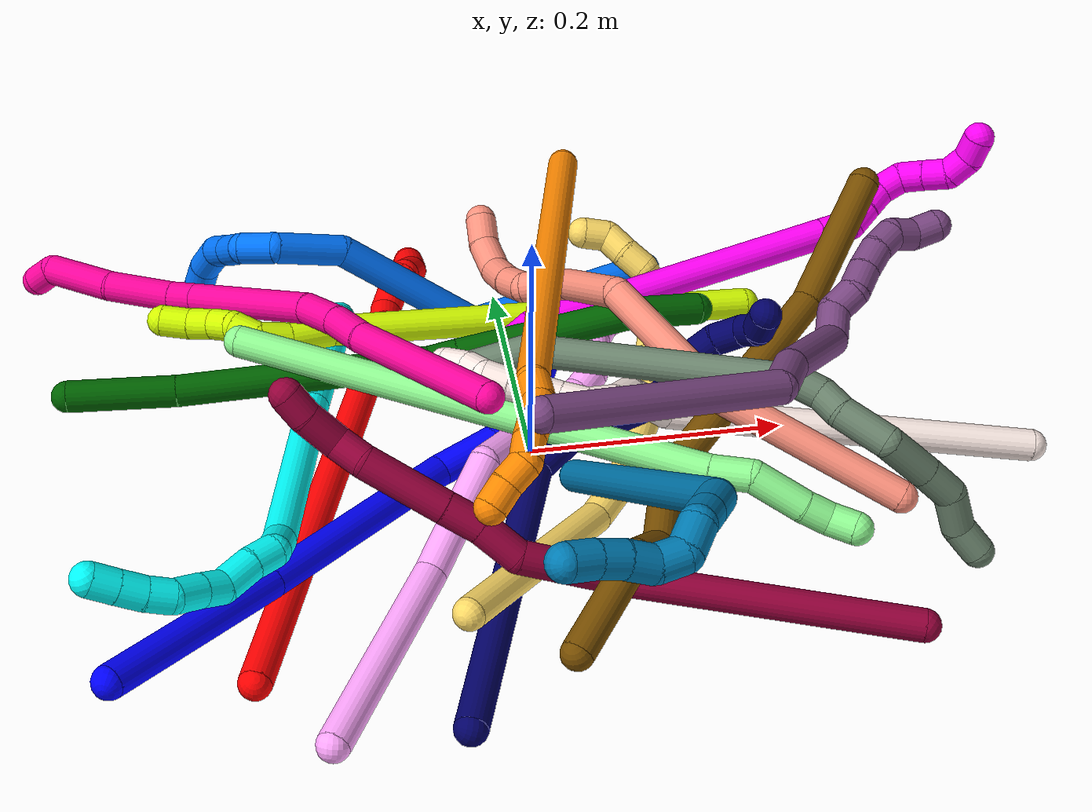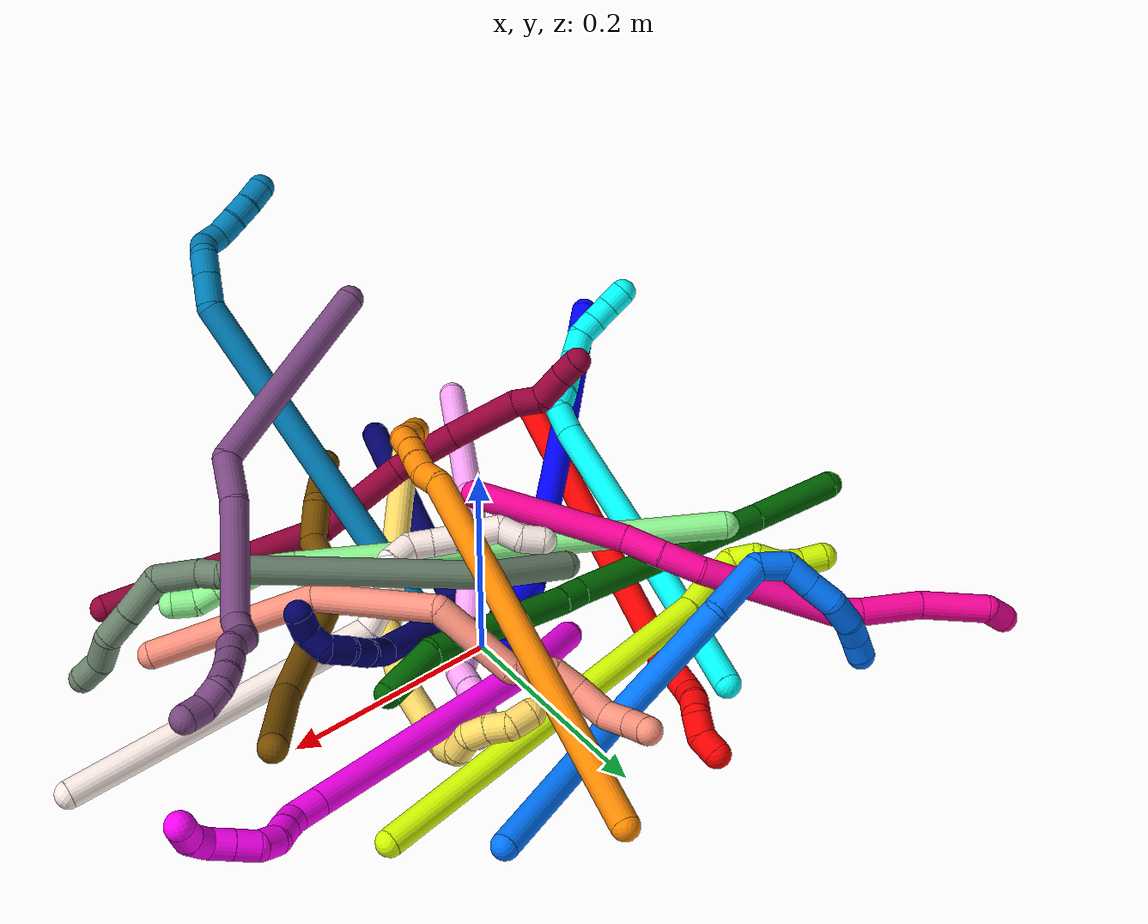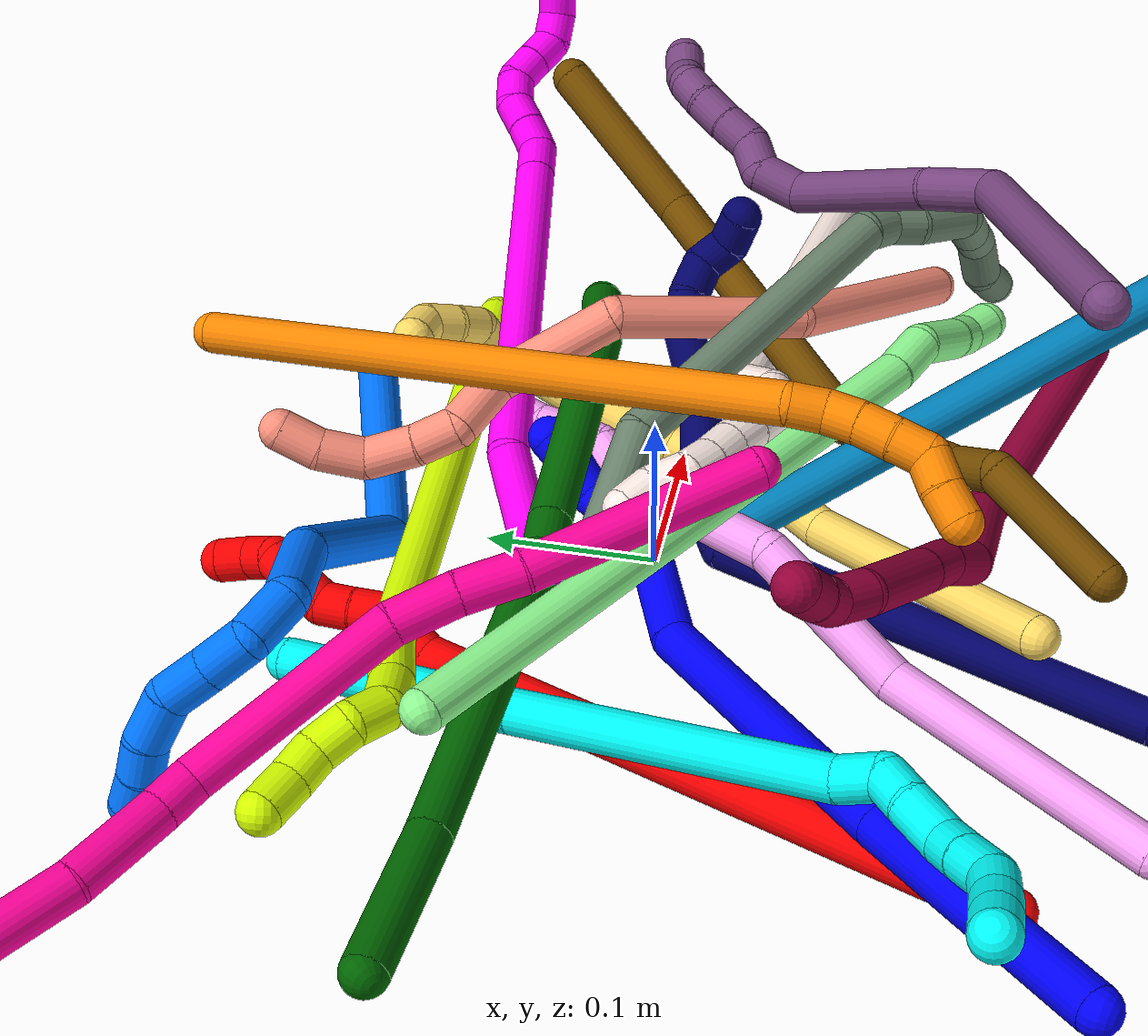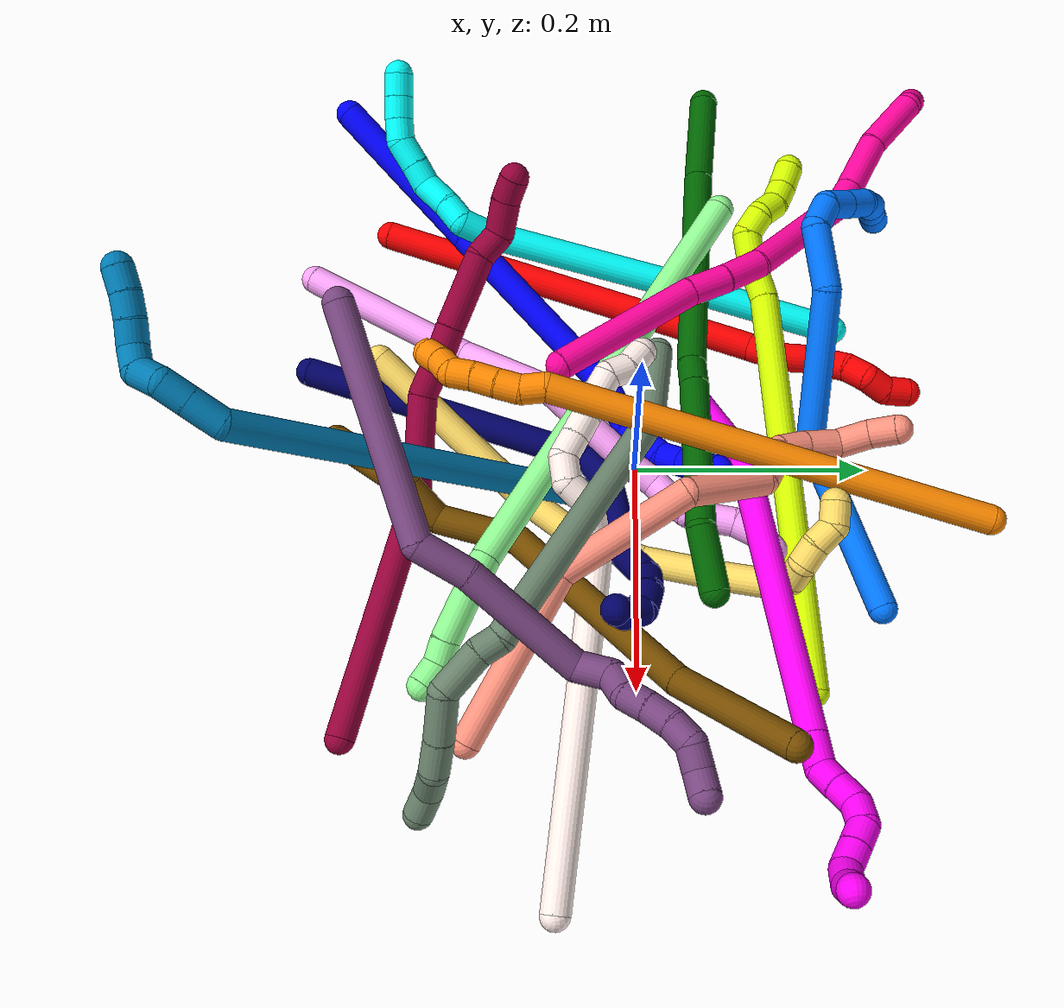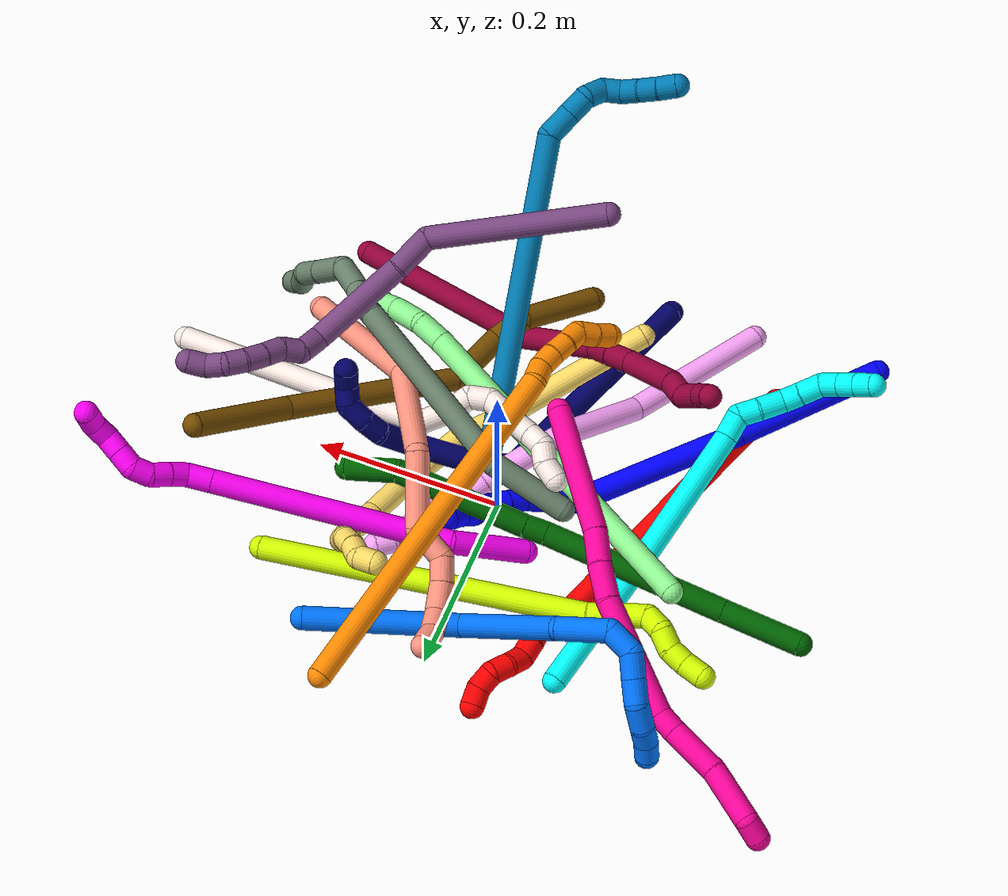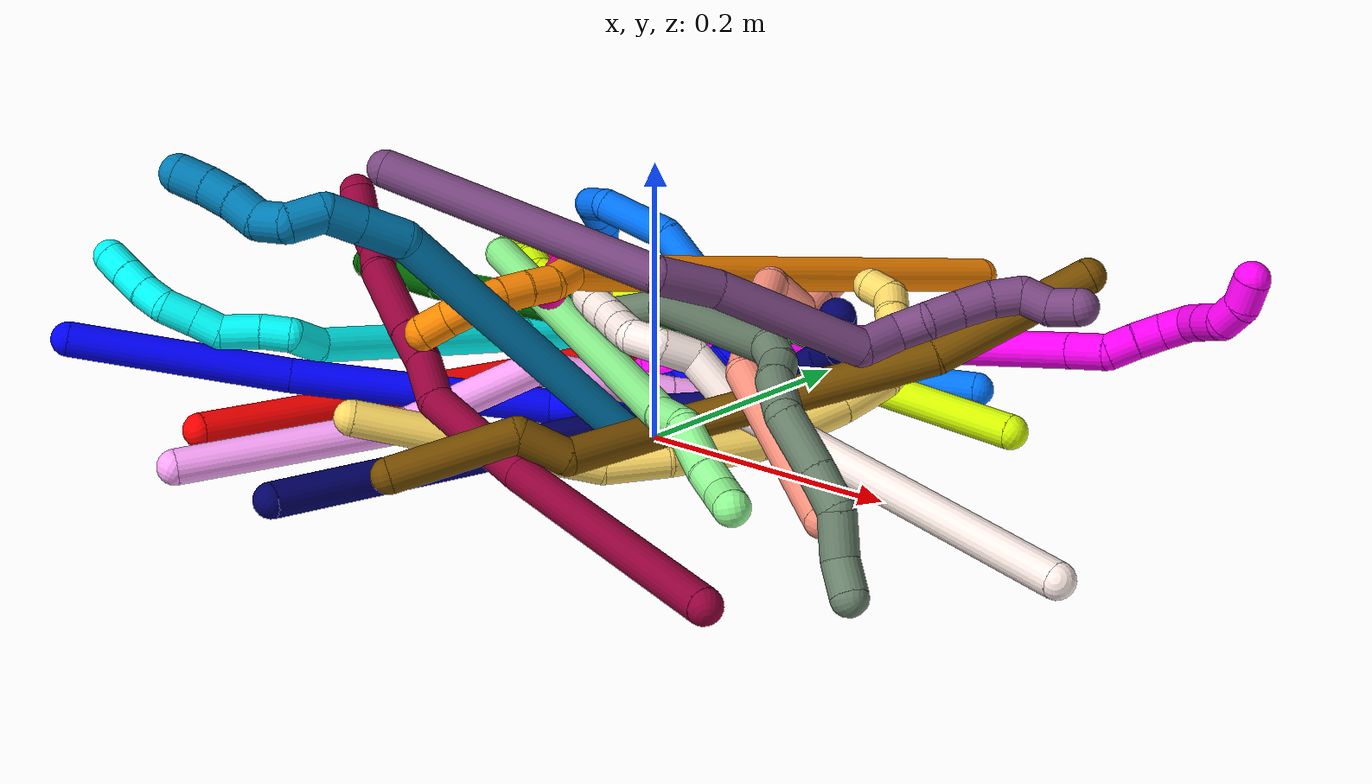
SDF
<sdf version="1.7">
 <world name="default">
  <plugin name="TubeGeneratorPlugin" filename="libtube_generator_plugin.so"/>
  <model name="photoneo_s_sensor">
   <static>1</static>
   <pose>0 0 2 1.57079 1.57079 3.14159</pose>
   <link name="link">
    <inertial><mass>0.1</mass></inertial>
    <sensor name="sensor" type="depth">
     <update_rate>30</update_rate>
     <camera>
      <horizontal_fov>1.22</horizontal_fov>
      <image><width>1920</width><height>1200</height><format>B8G8R8</format></image>
      <clip><near>0.1</near><far>4</far></clip>
      <depth_camera><output>points</output></depth_camera>
     </camera>
     <plugin name="camera_plugin" filename="libgazebo_ros_depth_camera.so">
      <baseline>0.2</baseline>
      <alwaysOn>1</alwaysOn>
      <updateRate>0.0</updateRate>
      <cameraName>camera_ir</cameraName>
      <imageTopicName>/camera/color/image_raw</imageTopicName>
      <cameraInfoTopicName>/camera/color/camera_info</cameraInfoTopicName>
      <depthImageTopicName>/camera/depth/image_raw</depthImageTopicName>
      <depthImageCameraInfoTopicName>/camera/depth/camera_info</depthImageCameraInfoTopicName>
      <pointCloudTopicName>/camera/depth/points</pointCloudTopicName>
      <frameName>fr_optical</frameName>
      <pointCloudCutoff>0.1</pointCloudCutoff>
      <pointCloudCutoffMax>2.0</pointCloudCutoffMax>
      <distortionK1>0</distortionK1>
      <distortionK2>0</distortionK2>
      <distortionK3>0</distortionK3>
      <distortionT1>0</distortionT1>
      <distortionT2>0</distortionT2>
      <CxPrime>0</CxPrime>
      <Cx>0</Cx>
      <Cy>0</Cy>
      <focalLength>0</focalLength>
      <hackBaseline>0</hackBaseline>
     </plugin>
    </sensor>
   </link>
  </model>
  <gravity>0 0 -9.8</gravity>
  <magnetic_field>6e-06 2.3e-05 -4.2e-05</magnetic_field>
  <atmosphere type="adiabatic"/>
  <physics name="default_physics" default="0" type="ode">
   <max_step_size>0.003</max_step_size>
   <real_time_factor>1</real_time_factor>
   <real_time_update_rate>1000</real_time_update_rate>
   <max_contacts>10000</max_contacts>
   <ode>
    <solver>
     <type>quick</type>
     <iters>100</iters>
     <sor>1.3</sor>
     <use_dynamic_moi_rescaling>0</use_dynamic_moi_rescaling>
    </solver>
    <constraints>
     <contact_max_correcting_vel>0</contact_max_correcting_vel>
     <contact_surface_layer>0.001</contact_surface_layer>
     <cfm>0</cfm>
     <erp>0.2</erp>
    </constraints>
   </ode>
  </physics>
  <scene><ambient>0.4 0.4 0.4 1</ambient><background>0.7 0.7 0.7 1</background><shadows>0</shadows></scene>
  <audio><device>default</device></audio>
  <spherical_coordinates>
   <surface_model>EARTH_WGS84</surface_model>
   <latitude_deg>0</latitude_deg>
   <longitude_deg>0</longitude_deg>
   <elevation>0</elevation>
   <heading_deg>0</heading_deg>
  </spherical_coordinates>
  <model name="bin">
   <static>1</static>
   <link name="bottom">
    <collision name="collision-bottom">
     <pose>0 0 -0.01 0 -0 0</pose>
     <geometry><box><size>0.8 0.6 0.02</size></box></geometry>
     <surface>
      <friction><ode><mu>100</mu><mu2>100</mu2></ode></friction>
      <contact><collide_bitmask>65535</collide_bitmask></contact>
     </surface>
    </collision>
   </link>
   <link name="west_wall">
    <collision name="collision-west_wall">
     <pose>-0.41 0 0.1 0 -0 0</pose>
     <geometry><box><size>0.02 0.6 0.2</size></box></geometry>
     <surface>
      <friction><ode><mu>100</mu><mu2>100</mu2></ode></friction>
      <contact><collide_bitmask>65535</collide_bitmask></contact>
     </surface>
    </collision>
   </link>
   <link name="east_wall">
    <collision name="collision-east_wall">
     <pose>0.41 0 0.1 0 -0 0</pose>
     <geometry><box><size>0.02 0.6 0.2</size></box></geometry>
     <surface>
      <friction><ode><mu>100</mu><mu2>100</mu2></ode></friction>
      <contact><collide_bitmask>65535</collide_bitmask></contact>
     </surface>
    </collision>
   </link>
   <link name="south_wall">
    <collision name="collision-south_wall">
     <pose>0 -0.31 0.1 0 -0 0</pose>
     <geometry><box><size>0.8 0.02 0.2</size></box></geometry>
     <surface>
      <friction><ode><mu>100</mu><mu2>100</mu2></ode></friction>
      <contact><collide_bitmask>65535</collide_bitmask></contact>
     </surface>
    </collision>
   </link>
   <link name="north_wall">
    <collision name="collision-north_wall">
     <pose>0 0.31 0.1 0 -0 0</pose>
     <geometry><box><size>0.8 0.02 0.2</size></box></geometry>
     <surface>
      <friction><ode><mu>100</mu><mu2>100</mu2></ode></friction>
      <contact><collide_bitmask>65535</collide_bitmask></contact>
     </surface>
    </collision>
   </link>
  </model>
  <model name="1">
   <static>0</static>
   <link name="1">
    <collision name="collision-cylinder-e_1_1_4">
     <pose>0.036249 0.003891 -0.070241 -3.08626 0.475799 -2.91432</pose>
     <geometry><cylinder><radius>0.0125</radius><length>0.158278</length></cylinder></geometry>
     <surface>
      <friction><ode><mu>1.16</mu><mu2>1.16</mu2><slip1>0</slip1><slip2>0</slip2></ode></friction>
      <contact><ode><kp>1e+06</kp><kd>1</kd><max_vel>0</max_vel><min_depth>0.001</min_depth></ode></contact>
     </surface>
    </collision>
    <visual name="visual-cylinder-e_1_1_4">
     <pose>0.036249 0.003891 -0.070241 -3.08626 0.475799 -2.91432</pose>
     <geometry><cylinder><radius>0.0125</radius><length>0.158278</length></cylinder></geometry>
     <material><ambient>0 0 1 1</ambient></material>
    </visual>
    <collision name="collision-cylinder-e_2_4_5">
     <pose>0.114291 0.01708 -0.22377 -3.03042 0.462596 -2.67755</pose>
     <geometry><cylinder><radius>0.0125</radius><length>0.187296</length></cylinder></geometry>
     <surface>
      <friction><ode><mu>1.16</mu><mu2>1.16</mu2><slip1>0</slip1><slip2>0</slip2></ode></friction>
      <contact><ode><kp>1e+06</kp><kd>1</kd><max_vel>0</max_vel><min_depth>0.001</min_depth></ode></contact>
     </surface>
    </collision>
    <visual name="visual-cylinder-e_2_4_5">
     <pose>0.114291 0.01708 -0.22377 -3.03042 0.462596 -2.67755</pose>
     <geometry><cylinder><radius>0.0125</radius><length>0.187296</length></cylinder></geometry>
     <material><ambient>0 0 1 1</ambient></material>
    </visual>
    <collision name="collision-cylinder-e_3_5_6">
     <pose>0.170284 0.038531 -0.324368 -2.52947 0.59127 -1.53395</pose>
     <geometry><cylinder><radius>0.0125</radius><length>0.050951</length></cylinder></geometry>
     <surface>
      <friction><ode><mu>1.16</mu><mu2>1.16</mu2><slip1>0</slip1><slip2>0</slip2></ode></friction>
      <contact><ode><kp>1e+06</kp><kd>1</kd><max_vel>0</max_vel><min_depth>0.001</min_depth></ode></contact>
     </surface>
    </collision>
    <visual name="visual-cylinder-e_3_5_6">
     <pose>0.170284 0.038531 -0.324368 -2.52947 0.59127 -1.53395</pose>
     <geometry><cylinder><radius>0.0125</radius><length>0.050951</length></cylinder></geometry>
     <material><ambient>0 0 1 1</ambient></material>
    </visual>
    <collision name="collision-cylinder-e_4_6_7">
     <pose>0.187023 0.055369 -0.35055 -2.65581 0.247815 -0.931519</pose>
     <geometry><cylinder><radius>0.0125</radius><length>0.020699</length></cylinder></geometry>
     <surface>
      <friction><ode><mu>1.16</mu><mu2>1.16</mu2><slip1>0</slip1><slip2>0</slip2></ode></friction>
      <contact><ode><kp>1e+06</kp><kd>1</kd><max_vel>0</max_vel><min_depth>0.001</min_depth></ode></contact>
     </surface>
    </collision>
    <visual name="visual-cylinder-e_4_6_7">
     <pose>0.187023 0.055369 -0.35055 -2.65581 0.247815 -0.931519</pose>
     <geometry><cylinder><radius>0.0125</radius><length>0.020699</length></cylinder></geometry>
     <material><ambient>0 0 1 1</ambient></material>
    </visual>
    <collision name="collision-cylinder-e_5_7_8">
     <pose>0.192682 0.064837 -0.368539 -2.65839 0.294254 -1.08292</pose>
     <geometry><cylinder><radius>0.0125</radius><length>0.021513</length></cylinder></geometry>
     <surface>
      <friction><ode><mu>1.16</mu><mu2>1.16</mu2><slip1>0</slip1><slip2>0</slip2></ode></friction>
      <contact><ode><kp>1e+06</kp><kd>1</kd><max_vel>0</max_vel><min_depth>0.001</min_depth></ode></contact>
     </surface>
    </collision>
    <visual name="visual-cylinder-e_5_7_8">
     <pose>0.192682 0.064837 -0.368539 -2.65839 0.294254 -1.08292</pose>
     <geometry><cylinder><radius>0.0125</radius><length>0.021513</length></cylinder></geometry>
     <material><ambient>0 0 1 1</ambient></material>
    </visual>
    <collision name="collision-cylinder-e_6_8_9">
     <pose>0.195168 0.07261 -0.387611 -2.84978 -0.060848 0.408419</pose>
     <geometry><cylinder><radius>0.0125</radius><length>0.020832</length></cylinder></geometry>
     <surface>
      <friction><ode><mu>1.16</mu><mu2>1.16</mu2><slip1>0</slip1><slip2>0</slip2></ode></friction>
      <contact><ode><kp>1e+06</kp><kd>1</kd><max_vel>0</max_vel><min_depth>0.001</min_depth></ode></contact>
     </surface>
    </collision>
    <visual name="visual-cylinder-e_6_8_9">
     <pose>0.195168 0.07261 -0.387611 -2.84978 -0.060848 0.408419</pose>
     <geometry><cylinder><radius>0.0125</radius><length>0.020832</length></cylinder></geometry>
     <material><ambient>0 0 1 1</ambient></material>
    </visual>
    <collision name="collision-cylinder-e_7_9_10">
     <pose>0.193499 0.082246 -0.405056 -2.41577 -0.103083 0.27005</pose>
     <geometry><cylinder><radius>0.0125</radius><length>0.02013</length></cylinder></geometry>
     <surface>
      <friction><ode><mu>1.16</mu><mu2>1.16</mu2><slip1>0</slip1><slip2>0</slip2></ode></friction>
      <contact><ode><kp>1e+06</kp><kd>1</kd><max_vel>0</max_vel><min_depth>0.001</min_depth></ode></contact>
     </surface>
    </collision>
    <visual name="visual-cylinder-e_7_9_10">
     <pose>0.193499 0.082246 -0.405056 -2.41577 -0.103083 0.27005</pose>
     <geometry><cylinder><radius>0.0125</radius><length>0.02013</length></cylinder></geometry>
     <material><ambient>0 0 1 1</ambient></material>
    </visual>
    <collision name="collision-cylinder-e_8_10_2">
     <pose>0.190567 0.094422 -0.420843 -2.55377 -0.18792 0.603664</pose>
     <geometry><cylinder><radius>0.0125</radius><length>0.020302</length></cylinder></geometry>
     <surface>
      <friction><ode><mu>1.16</mu><mu2>1.16</mu2><slip1>0</slip1><slip2>0</slip2></ode></friction>
      <contact><ode><kp>1e+06</kp><kd>1</kd><max_vel>0</max_vel><min_depth>0.001</min_depth></ode></contact>
     </surface>
    </collision>
    <visual name="visual-cylinder-e_8_10_2">
     <pose>0.190567 0.094422 -0.420843 -2.55377 -0.18792 0.603664</pose>
     <geometry><cylinder><radius>0.0125</radius><length>0.020302</length></cylinder></geometry>
     <material><ambient>0 0 1 1</ambient></material>
    </visual>
    <collision name="collision-sphere-2">
     <pose>0.18867 0.099952 -0.429142 0 -0 0</pose>
     <geometry><sphere><radius>0.0125</radius></sphere></geometry>
     <surface>
      <friction><ode><mu>1.16</mu><mu2>1.16</mu2><slip1>0</slip1><slip2>0</slip2></ode></friction>
      <contact><ode><kp>1e+06</kp><kd>1</kd><max_vel>0</max_vel><min_depth>0.001</min_depth></ode></contact>
     </surface>
    </collision>
    <visual name="visual-sphere-2">
     <pose>0.18867 0.099952 -0.429142 0 -0 0</pose>
     <geometry><sphere><radius>0.0125</radius></sphere></geometry>
     <material><ambient>0 0 1 1</ambient></material>
    </visual>
    <collision name="collision-sphere-10">
     <pose>0.192463 0.088892 -0.412544 0 -0 0</pose>
     <geometry><sphere><radius>0.0125</radius></sphere></geometry>
     <surface>
      <friction><ode><mu>1.16</mu><mu2>1.16</mu2><slip1>0</slip1><slip2>0</slip2></ode></friction>
      <contact><ode><kp>1e+06</kp><kd>1</kd><max_vel>0</max_vel><min_depth>0.001</min_depth></ode></contact>
     </surface>
    </collision>
    <visual name="visual-sphere-10">
     <pose>0.192463 0.088892 -0.412544 0 -0 0</pose>
     <geometry><sphere><radius>0.0125</radius></sphere></geometry>
     <material><ambient>0 0 1 1</ambient></material>
    </visual>
    <collision name="collision-sphere-9">
     <pose>0.194534 0.075601 -0.397568 0 -0 0</pose>
     <geometry><sphere><radius>0.0125</radius></sphere></geometry>
     <surface>
      <friction><ode><mu>1.16</mu><mu2>1.16</mu2><slip1>0</slip1><slip2>0</slip2></ode></friction>
      <contact><ode><kp>1e+06</kp><kd>1</kd><max_vel>0</max_vel><min_depth>0.001</min_depth></ode></contact>
     </surface>
    </collision>
    <visual name="visual-sphere-9">
     <pose>0.194534 0.075601 -0.397568 0 -0 0</pose>
     <geometry><sphere><radius>0.0125</radius></sphere></geometry>
     <material><ambient>0 0 1 1</ambient></material>
    </visual>
    <collision name="collision-sphere-4">
     <pose>0.072499 0.007782 -0.140482 0 -0 0</pose>
     <geometry><sphere><radius>0.0125</radius></sphere></geometry>
     <surface>
      <friction><ode><mu>1.16</mu><mu2>1.16</mu2><slip1>0</slip1><slip2>0</slip2></ode></friction>
      <contact><ode><kp>1e+06</kp><kd>1</kd><max_vel>0</max_vel><min_depth>0.001</min_depth></ode></contact>
     </surface>
    </collision>
    <visual name="visual-sphere-4">
     <pose>0.072499 0.007782 -0.140482 0 -0 0</pose>
     <geometry><sphere><radius>0.0125</radius></sphere></geometry>
     <material><ambient>0 0 1 1</ambient></material>
    </visual>
    <collision name="collision-sphere-1">
     <geometry><sphere><radius>0.0125</radius></sphere></geometry>
     <surface>
      <friction><ode><mu>1.16</mu><mu2>1.16</mu2><slip1>0</slip1><slip2>0</slip2></ode></friction>
      <contact><ode><kp>1e+06</kp><kd>1</kd><max_vel>0</max_vel><min_depth>0.001</min_depth></ode></contact>
     </surface>
    </collision>
    <visual name="visual-sphere-1">
     <geometry><sphere><radius>0.0125</radius></sphere></geometry>
     <material><ambient>0 0 1 1</ambient></material>
    </visual>
    <collision name="collision-sphere-8">
     <pose>0.195801 0.069619 -0.377654 0 -0 0</pose>
     <geometry><sphere><radius>0.0125</radius></sphere></geometry>
     <surface>
      <friction><ode><mu>1.16</mu><mu2>1.16</mu2><slip1>0</slip1><slip2>0</slip2></ode></friction>
      <contact><ode><kp>1e+06</kp><kd>1</kd><max_vel>0</max_vel><min_depth>0.001</min_depth></ode></contact>
     </surface>
    </collision>
    <visual name="visual-sphere-8">
     <pose>0.195801 0.069619 -0.377654 0 -0 0</pose>
     <geometry><sphere><radius>0.0125</radius></sphere></geometry>
     <material><ambient>0 0 1 1</ambient></material>
    </visual>
    <collision name="collision-sphere-5">
     <pose>0.156084 0.026378 -0.307057 0 -0 0</pose>
     <geometry><sphere><radius>0.0125</radius></sphere></geometry>
     <surface>
      <friction><ode><mu>1.16</mu><mu2>1.16</mu2><slip1>0</slip1><slip2>0</slip2></ode></friction>
      <contact><ode><kp>1e+06</kp><kd>1</kd><max_vel>0</max_vel><min_depth>0.001</min_depth></ode></contact>
     </surface>
    </collision>
    <visual name="visual-sphere-5">
     <pose>0.156084 0.026378 -0.307057 0 -0 0</pose>
     <geometry><sphere><radius>0.0125</radius></sphere></geometry>
     <material><ambient>0 0 1 1</ambient></material>
    </visual>
    <collision name="collision-sphere-6">
     <pose>0.184485 0.050684 -0.341678 0 -0 0</pose>
     <geometry><sphere><radius>0.0125</radius></sphere></geometry>
     <surface>
      <friction><ode><mu>1.16</mu><mu2>1.16</mu2><slip1>0</slip1><slip2>0</slip2></ode></friction>
      <contact><ode><kp>1e+06</kp><kd>1</kd><max_vel>0</max_vel><min_depth>0.001</min_depth></ode></contact>
     </surface>
    </collision>
    <visual name="visual-sphere-6">
     <pose>0.184485 0.050684 -0.341678 0 -0 0</pose>
     <geometry><sphere><radius>0.0125</radius></sphere></geometry>
     <material><ambient>0 0 1 1</ambient></material>
    </visual>
    <collision name="collision-sphere-7">
     <pose>0.189562 0.060054 -0.359423 0 -0 0</pose>
     <geometry><sphere><radius>0.0125</radius></sphere></geometry>
     <surface>
      <friction><ode><mu>1.16</mu><mu2>1.16</mu2><slip1>0</slip1><slip2>0</slip2></ode></friction>
      <contact><ode><kp>1e+06</kp><kd>1</kd><max_vel>0</max_vel><min_depth>0.001</min_depth></ode></contact>
     </surface>
    </collision>
    <visual name="visual-sphere-7">
     <pose>0.189562 0.060054 -0.359423 0 -0 0</pose>
     <geometry><sphere><radius>0.0125</radius></sphere></geometry>
     <material><ambient>0 0 1 1</ambient></material>
    </visual>
    <inertial>
     <pose>0.111332 0.026808 -0.219025 0 -0 0</pose>
     <mass>0.5</mass>
     <inertia>
      <ixx>-0.001016</ixx>
      <ixy>0</ixy>
      <ixz>0</ixz>
      <iyy>0.000541</iyy>
      <iyz>0</iyz>
      <izz>-0.000524</izz>
     </inertia>
    </inertial>
   </link>
   <pose>-0.324163 -0.258882 0.067735 1.54815 0.480713 -0.370484</pose>
  </model>
  <model name="2">
   <static>0</static>
   <link name="2">
    <collision name="collision-cylinder-e_1_1_4">
     <pose>0.067308 0.139114 -0.078874 -2.08657 0.398384 -0.667127</pose>
     <geometry><cylinder><radius>0.0125</radius><length>0.347012</length></cylinder></geometry>
     <surface>
      <friction><ode><mu>1.16</mu><mu2>1.16</mu2><slip1>0</slip1><slip2>0</slip2></ode></friction>
      <contact><ode><kp>1e+06</kp><kd>1</kd><max_vel>0</max_vel><min_depth>0.001</min_depth></ode></contact>
     </surface>
    </collision>
    <visual name="visual-cylinder-e_1_1_4">
     <pose>0.067308 0.139114 -0.078874 -2.08657 0.398384 -0.667127</pose>
     <geometry><cylinder><radius>0.0125</radius><length>0.347012</length></cylinder></geometry>
     <material><ambient>1 0 0 1</ambient></material>
    </visual>
    <collision name="collision-cylinder-e_2_4_5">
     <pose>0.143535 0.291466 -0.15877 -1.6479 0.591532 -0.635964</pose>
     <geometry><cylinder><radius>0.0125</radius><length>0.031987</length></cylinder></geometry>
     <surface>
      <friction><ode><mu>1.16</mu><mu2>1.16</mu2><slip1>0</slip1><slip2>0</slip2></ode></friction>
      <contact><ode><kp>1e+06</kp><kd>1</kd><max_vel>0</max_vel><min_depth>0.001</min_depth></ode></contact>
     </surface>
    </collision>
    <visual name="visual-cylinder-e_2_4_5">
     <pose>0.143535 0.291466 -0.15877 -1.6479 0.591532 -0.635964</pose>
     <geometry><cylinder><radius>0.0125</radius><length>0.031987</length></cylinder></geometry>
     <material><ambient>1 0 0 1</ambient></material>
    </visual>
    <collision name="collision-cylinder-e_3_5_6">
     <pose>0.153663 0.313304 -0.164899 -2.10651 0.120321 -0.210819</pose>
     <geometry><cylinder><radius>0.0125</radius><length>0.020152</length></cylinder></geometry>
     <surface>
      <friction><ode><mu>1.16</mu><mu2>1.16</mu2><slip1>0</slip1><slip2>0</slip2></ode></friction>
      <contact><ode><kp>1e+06</kp><kd>1</kd><max_vel>0</max_vel><min_depth>0.001</min_depth></ode></contact>
     </surface>
    </collision>
    <visual name="visual-cylinder-e_3_5_6">
     <pose>0.153663 0.313304 -0.164899 -2.10651 0.120321 -0.210819</pose>
     <geometry><cylinder><radius>0.0125</radius><length>0.020152</length></cylinder></geometry>
     <material><ambient>1 0 0 1</ambient></material>
    </visual>
    <collision name="collision-cylinder-e_4_6_7">
     <pose>0.157014 0.330167 -0.1756 -2.16618 0.211487 -0.394972</pose>
     <geometry><cylinder><radius>0.0125</radius><length>0.02041</length></cylinder></geometry>
     <surface>
      <friction><ode><mu>1.16</mu><mu2>1.16</mu2><slip1>0</slip1><slip2>0</slip2></ode></friction>
      <contact><ode><kp>1e+06</kp><kd>1</kd><max_vel>0</max_vel><min_depth>0.001</min_depth></ode></contact>
     </surface>
    </collision>
    <visual name="visual-cylinder-e_4_6_7">
     <pose>0.157014 0.330167 -0.1756 -2.16618 0.211487 -0.394972</pose>
     <geometry><cylinder><radius>0.0125</radius><length>0.02041</length></cylinder></geometry>
     <material><ambient>1 0 0 1</ambient></material>
    </visual>
    <collision name="collision-cylinder-e_5_7_8">
     <pose>0.164011 0.347211 -0.181835 -1.64336 0.503778 -0.539968</pose>
     <geometry><cylinder><radius>0.0125</radius><length>0.020113</length></cylinder></geometry>
     <surface>
      <friction><ode><mu>1.16</mu><mu2>1.16</mu2><slip1>0</slip1><slip2>0</slip2></ode></friction>
      <contact><ode><kp>1e+06</kp><kd>1</kd><max_vel>0</max_vel><min_depth>0.001</min_depth></ode></contact>
     </surface>
    </collision>
    <visual name="visual-cylinder-e_5_7_8">
     <pose>0.164011 0.347211 -0.181835 -1.64336 0.503778 -0.539968</pose>
     <geometry><cylinder><radius>0.0125</radius><length>0.020113</length></cylinder></geometry>
     <material><ambient>1 0 0 1</ambient></material>
    </visual>
    <collision name="collision-cylinder-e_6_8_9">
     <pose>0.175207 0.363384 -0.185055 -1.90699 0.68097 -0.925858</pose>
     <geometry><cylinder><radius>0.0125</radius><length>0.020147</length></cylinder></geometry>
     <surface>
      <friction><ode><mu>1.16</mu><mu2>1.16</mu2><slip1>0</slip1><slip2>0</slip2></ode></friction>
      <contact><ode><kp>1e+06</kp><kd>1</kd><max_vel>0</max_vel><min_depth>0.001</min_depth></ode></contact>
     </surface>
    </collision>
    <visual name="visual-cylinder-e_6_8_9">
     <pose>0.175207 0.363384 -0.185055 -1.90699 0.68097 -0.925858</pose>
     <geometry><cylinder><radius>0.0125</radius><length>0.020147</length></cylinder></geometry>
     <material><ambient>1 0 0 1</ambient></material>
    </visual>
    <collision name="collision-cylinder-e_7_9_10">
     <pose>0.18563 0.375357 -0.195624 -2.62054 0.417136 -1.34204</pose>
     <geometry><cylinder><radius>0.0125</radius><length>0.020146</length></cylinder></geometry>
     <surface>
      <friction><ode><mu>1.16</mu><mu2>1.16</mu2><slip1>0</slip1><slip2>0</slip2></ode></friction>
      <contact><ode><kp>1e+06</kp><kd>1</kd><max_vel>0</max_vel><min_depth>0.001</min_depth></ode></contact>
     </surface>
    </collision>
    <visual name="visual-cylinder-e_7_9_10">
     <pose>0.18563 0.375357 -0.195624 -2.62054 0.417136 -1.34204</pose>
     <geometry><cylinder><radius>0.0125</radius><length>0.020146</length></cylinder></geometry>
     <material><ambient>1 0 0 1</ambient></material>
    </visual>
    <collision name="collision-cylinder-e_8_10_2">
     <pose>0.189861 0.387256 -0.210453 -2.32278 0.014947 -0.034444</pose>
     <geometry><cylinder><radius>0.0125</radius><length>0.020034</length></cylinder></geometry>
     <surface>
      <friction><ode><mu>1.16</mu><mu2>1.16</mu2><slip1>0</slip1><slip2>0</slip2></ode></friction>
      <contact><ode><kp>1e+06</kp><kd>1</kd><max_vel>0</max_vel><min_depth>0.001</min_depth></ode></contact>
     </surface>
    </collision>
    <visual name="visual-cylinder-e_8_10_2">
     <pose>0.189861 0.387256 -0.210453 -2.32278 0.014947 -0.034444</pose>
     <geometry><cylinder><radius>0.0125</radius><length>0.020034</length></cylinder></geometry>
     <material><ambient>1 0 0 1</ambient></material>
    </visual>
    <collision name="collision-sphere-2">
     <pose>0.19001 0.394571 -0.217295 0 -0 0</pose>
     <geometry><sphere><radius>0.0125</radius></sphere></geometry>
     <surface>
      <friction><ode><mu>1.16</mu><mu2>1.16</mu2><slip1>0</slip1><slip2>0</slip2></ode></friction>
      <contact><ode><kp>1e+06</kp><kd>1</kd><max_vel>0</max_vel><min_depth>0.001</min_depth></ode></contact>
     </surface>
    </collision>
    <visual name="visual-sphere-2">
     <pose>0.19001 0.394571 -0.217295 0 -0 0</pose>
     <geometry><sphere><radius>0.0125</radius></sphere></geometry>
     <material><ambient>1 0 0 1</ambient></material>
    </visual>
    <collision name="collision-sphere-10">
     <pose>0.189711 0.379941 -0.203611 0 -0 0</pose>
     <geometry><sphere><radius>0.0125</radius></sphere></geometry>
     <surface>
      <friction><ode><mu>1.16</mu><mu2>1.16</mu2><slip1>0</slip1><slip2>0</slip2></ode></friction>
      <contact><ode><kp>1e+06</kp><kd>1</kd><max_vel>0</max_vel><min_depth>0.001</min_depth></ode></contact>
     </surface>
    </collision>
    <visual name="visual-sphere-10">
     <pose>0.189711 0.379941 -0.203611 0 -0 0</pose>
     <geometry><sphere><radius>0.0125</radius></sphere></geometry>
     <material><ambient>1 0 0 1</ambient></material>
    </visual>
    <collision name="collision-sphere-9">
     <pose>0.181549 0.370772 -0.187637 0 -0 0</pose>
     <geometry><sphere><radius>0.0125</radius></sphere></geometry>
     <surface>
      <friction><ode><mu>1.16</mu><mu2>1.16</mu2><slip1>0</slip1><slip2>0</slip2></ode></friction>
      <contact><ode><kp>1e+06</kp><kd>1</kd><max_vel>0</max_vel><min_depth>0.001</min_depth></ode></contact>
     </surface>
    </collision>
    <visual name="visual-sphere-9">
     <pose>0.181549 0.370772 -0.187637 0 -0 0</pose>
     <geometry><sphere><radius>0.0125</radius></sphere></geometry>
     <material><ambient>1 0 0 1</ambient></material>
    </visual>
    <collision name="collision-sphere-4">
     <pose>0.134616 0.278229 -0.157747 0 -0 0</pose>
     <geometry><sphere><radius>0.0125</radius></sphere></geometry>
     <surface>
      <friction><ode><mu>1.16</mu><mu2>1.16</mu2><slip1>0</slip1><slip2>0</slip2></ode></friction>
      <contact><ode><kp>1e+06</kp><kd>1</kd><max_vel>0</max_vel><min_depth>0.001</min_depth></ode></contact>
     </surface>
    </collision>
    <visual name="visual-sphere-4">
     <pose>0.134616 0.278229 -0.157747 0 -0 0</pose>
     <geometry><sphere><radius>0.0125</radius></sphere></geometry>
     <material><ambient>1 0 0 1</ambient></material>
    </visual>
    <collision name="collision-sphere-1">
     <geometry><sphere><radius>0.0125</radius></sphere></geometry>
     <surface>
      <friction><ode><mu>1.16</mu><mu2>1.16</mu2><slip1>0</slip1><slip2>0</slip2></ode></friction>
      <contact><ode><kp>1e+06</kp><kd>1</kd><max_vel>0</max_vel><min_depth>0.001</min_depth></ode></contact>
     </surface>
    </collision>
    <visual name="visual-sphere-1">
     <geometry><sphere><radius>0.0125</radius></sphere></geometry>
     <material><ambient>1 0 0 1</ambient></material>
    </visual>
    <collision name="collision-sphere-8">
     <pose>0.168866 0.355995 -0.182473 0 -0 0</pose>
     <geometry><sphere><radius>0.0125</radius></sphere></geometry>
     <surface>
      <friction><ode><mu>1.16</mu><mu2>1.16</mu2><slip1>0</slip1><slip2>0</slip2></ode></friction>
      <contact><ode><kp>1e+06</kp><kd>1</kd><max_vel>0</max_vel><min_depth>0.001</min_depth></ode></contact>
     </surface>
    </collision>
    <visual name="visual-sphere-8">
     <pose>0.168866 0.355995 -0.182473 0 -0 0</pose>
     <geometry><sphere><radius>0.0125</radius></sphere></geometry>
     <material><ambient>1 0 0 1</ambient></material>
    </visual>
    <collision name="collision-sphere-5">
     <pose>0.152453 0.304702 -0.159792 0 -0 0</pose>
     <geometry><sphere><radius>0.0125</radius></sphere></geometry>
     <surface>
      <friction><ode><mu>1.16</mu><mu2>1.16</mu2><slip1>0</slip1><slip2>0</slip2></ode></friction>
      <contact><ode><kp>1e+06</kp><kd>1</kd><max_vel>0</max_vel><min_depth>0.001</min_depth></ode></contact>
     </surface>
    </collision>
    <visual name="visual-sphere-5">
     <pose>0.152453 0.304702 -0.159792 0 -0 0</pose>
     <geometry><sphere><radius>0.0125</radius></sphere></geometry>
     <material><ambient>1 0 0 1</ambient></material>
    </visual>
    <collision name="collision-sphere-6">
     <pose>0.154872 0.321906 -0.170005 0 -0 0</pose>
     <geometry><sphere><radius>0.0125</radius></sphere></geometry>
     <surface>
      <friction><ode><mu>1.16</mu><mu2>1.16</mu2><slip1>0</slip1><slip2>0</slip2></ode></friction>
      <contact><ode><kp>1e+06</kp><kd>1</kd><max_vel>0</max_vel><min_depth>0.001</min_depth></ode></contact>
     </surface>
    </collision>
    <visual name="visual-sphere-6">
     <pose>0.154872 0.321906 -0.170005 0 -0 0</pose>
     <geometry><sphere><radius>0.0125</radius></sphere></geometry>
     <material><ambient>1 0 0 1</ambient></material>
    </visual>
    <collision name="collision-sphere-7">
     <pose>0.159156 0.338427 -0.181196 0 -0 0</pose>
     <geometry><sphere><radius>0.0125</radius></sphere></geometry>
     <surface>
      <friction><ode><mu>1.16</mu><mu2>1.16</mu2><slip1>0</slip1><slip2>0</slip2></ode></friction>
      <contact><ode><kp>1e+06</kp><kd>1</kd><max_vel>0</max_vel><min_depth>0.001</min_depth></ode></contact>
     </surface>
    </collision>
    <visual name="visual-sphere-7">
     <pose>0.159156 0.338427 -0.181196 0 -0 0</pose>
     <geometry><sphere><radius>0.0125</radius></sphere></geometry>
     <material><ambient>1 0 0 1</ambient></material>
    </visual>
    <inertial>
     <pose>0.097242 0.200549 -0.109797 0 -0 0</pose>
     <mass>0.5</mass>
     <inertia>
      <ixx>0.000556</ixx>
      <ixy>0</ixy>
      <ixz>0</ixz>
      <iyy>-0.002594</iyy>
      <iyz>0</iyz>
      <izz>-0.004191</izz>
     </inertia>
    </inertial>
   </link>
   <pose>-0.229651 -0.222519 0.011493 0.497434 -0.043542 0.061144</pose>
  </model>
  <model name="3">
   <static>0</static>
   <link name="3">
    <collision name="collision-cylinder-e_1_1_4">
     <pose>-0.018605 -0.067465 0.001817 1.54387 -0.268997 -0.261932</pose>
     <geometry><cylinder><radius>0.0125</radius><length>0.140014</length></cylinder></geometry>
     <surface>
      <friction><ode><mu>1.16</mu><mu2>1.16</mu2><slip1>0</slip1><slip2>0</slip2></ode></friction>
      <contact><ode><kp>1e+06</kp><kd>1</kd><max_vel>0</max_vel><min_depth>0.001</min_depth></ode></contact>
     </surface>
    </collision>
    <visual name="visual-cylinder-e_1_1_4">
     <pose>-0.018605 -0.067465 0.001817 1.54387 -0.268997 -0.261932</pose>
     <geometry><cylinder><radius>0.0125</radius><length>0.140014</length></cylinder></geometry>
     <material><ambient>0.003922 1 0.996078 1</ambient></material>
    </visual>
    <collision name="collision-cylinder-e_2_4_5">
     <pose>-0.059263 -0.222153 0.004948 1.55573 -0.247607 -0.243942</pose>
     <geometry><cylinder><radius>0.0125</radius><length>0.179953</length></cylinder></geometry>
     <surface>
      <friction><ode><mu>1.16</mu><mu2>1.16</mu2><slip1>0</slip1><slip2>0</slip2></ode></friction>
      <contact><ode><kp>1e+06</kp><kd>1</kd><max_vel>0</max_vel><min_depth>0.001</min_depth></ode></contact>
     </surface>
    </collision>
    <visual name="visual-cylinder-e_2_4_5">
     <pose>-0.059263 -0.222153 0.004948 1.55573 -0.247607 -0.243942</pose>
     <geometry><cylinder><radius>0.0125</radius><length>0.179953</length></cylinder></geometry>
     <material><ambient>0.003922 1 0.996078 1</ambient></material>
    </visual>
    <collision name="collision-cylinder-e_3_5_6">
     <pose>-0.082548 -0.321729 0.010341 1.25191 -0.094548 -0.068376</pose>
     <geometry><cylinder><radius>0.0125</radius><length>0.026136</length></cylinder></geometry>
     <surface>
      <friction><ode><mu>1.16</mu><mu2>1.16</mu2><slip1>0</slip1><slip2>0</slip2></ode></friction>
      <contact><ode><kp>1e+06</kp><kd>1</kd><max_vel>0</max_vel><min_depth>0.001</min_depth></ode></contact>
     </surface>
    </collision>
    <visual name="visual-cylinder-e_3_5_6">
     <pose>-0.082548 -0.321729 0.010341 1.25191 -0.094548 -0.068376</pose>
     <geometry><cylinder><radius>0.0125</radius><length>0.026136</length></cylinder></geometry>
     <material><ambient>0.003922 1 0.996078 1</ambient></material>
    </visual>
    <collision name="collision-cylinder-e_4_6_7">
     <pose>-0.091994 -0.340596 0.017351 1.14778 -0.854978 -0.572847</pose>
     <geometry><cylinder><radius>0.0125</radius><length>0.021767</length></cylinder></geometry>
     <surface>
      <friction><ode><mu>1.16</mu><mu2>1.16</mu2><slip1>0</slip1><slip2>0</slip2></ode></friction>
      <contact><ode><kp>1e+06</kp><kd>1</kd><max_vel>0</max_vel><min_depth>0.001</min_depth></ode></contact>
     </surface>
    </collision>
    <visual name="visual-cylinder-e_4_6_7">
     <pose>-0.091994 -0.340596 0.017351 1.14778 -0.854978 -0.572847</pose>
     <geometry><cylinder><radius>0.0125</radius><length>0.021767</length></cylinder></geometry>
     <material><ambient>0.003922 1 0.996078 1</ambient></material>
    </visual>
    <collision name="collision-cylinder-e_5_7_8">
     <pose>-0.110755 -0.356289 0.02201 1.38489 -0.845985 -0.714724</pose>
     <geometry><cylinder><radius>0.0125</radius><length>0.028181</length></cylinder></geometry>
     <surface>
      <friction><ode><mu>1.16</mu><mu2>1.16</mu2><slip1>0</slip1><slip2>0</slip2></ode></friction>
      <contact><ode><kp>1e+06</kp><kd>1</kd><max_vel>0</max_vel><min_depth>0.001</min_depth></ode></contact>
     </surface>
    </collision>
    <visual name="visual-cylinder-e_5_7_8">
     <pose>-0.110755 -0.356289 0.02201 1.38489 -0.845985 -0.714724</pose>
     <geometry><cylinder><radius>0.0125</radius><length>0.028181</length></cylinder></geometry>
     <material><ambient>0.003922 1 0.996078 1</ambient></material>
    </visual>
    <collision name="collision-cylinder-e_6_8_9">
     <pose>-0.127481 -0.37099 0.029404 0.772208 -0.662999 -0.278036</pose>
     <geometry><cylinder><radius>0.0125</radius><length>0.020075</length></cylinder></geometry>
     <surface>
      <friction><ode><mu>1.16</mu><mu2>1.16</mu2><slip1>0</slip1><slip2>0</slip2></ode></friction>
      <contact><ode><kp>1e+06</kp><kd>1</kd><max_vel>0</max_vel><min_depth>0.001</min_depth></ode></contact>
     </surface>
    </collision>
    <visual name="visual-cylinder-e_6_8_9">
     <pose>-0.127481 -0.37099 0.029404 0.772208 -0.662999 -0.278036</pose>
     <geometry><cylinder><radius>0.0125</radius><length>0.020075</length></cylinder></geometry>
     <material><ambient>0.003922 1 0.996078 1</ambient></material>
    </visual>
    <collision name="collision-cylinder-e_7_9_10">
     <pose>-0.140933 -0.383498 0.041411 0.834024 -0.656698 -0.299578</pose>
     <geometry><cylinder><radius>0.0125</radius><length>0.023828</length></cylinder></geometry>
     <surface>
      <friction><ode><mu>1.16</mu><mu2>1.16</mu2><slip1>0</slip1><slip2>0</slip2></ode></friction>
      <contact><ode><kp>1e+06</kp><kd>1</kd><max_vel>0</max_vel><min_depth>0.001</min_depth></ode></contact>
     </surface>
    </collision>
    <visual name="visual-cylinder-e_7_9_10">
     <pose>-0.140933 -0.383498 0.041411 0.834024 -0.656698 -0.299578</pose>
     <geometry><cylinder><radius>0.0125</radius><length>0.023828</length></cylinder></geometry>
     <material><ambient>0.003922 1 0.996078 1</ambient></material>
    </visual>
    <collision name="collision-cylinder-e_8_10_11">
     <pose>-0.155505 -0.39201 0.054443 0.223804 -0.816131 -0.097088</pose>
     <geometry><cylinder><radius>0.0125</radius><length>0.020037</length></cylinder></geometry>
     <surface>
      <friction><ode><mu>1.16</mu><mu2>1.16</mu2><slip1>0</slip1><slip2>0</slip2></ode></friction>
      <contact><ode><kp>1e+06</kp><kd>1</kd><max_vel>0</max_vel><min_depth>0.001</min_depth></ode></contact>
     </surface>
    </collision>
    <visual name="visual-cylinder-e_8_10_11">
     <pose>-0.155505 -0.39201 0.054443 0.223804 -0.816131 -0.097088</pose>
     <geometry><cylinder><radius>0.0125</radius><length>0.020037</length></cylinder></geometry>
     <material><ambient>0.003922 1 0.996078 1</ambient></material>
    </visual>
    <collision name="collision-cylinder-e_9_11_12">
     <pose>-0.169366 -0.394485 0.068624 0.12644 -0.715613 -0.04733</pose>
     <geometry><cylinder><radius>0.0125</radius><length>0.020006</length></cylinder></geometry>
     <surface>
      <friction><ode><mu>1.16</mu><mu2>1.16</mu2><slip1>0</slip1><slip2>0</slip2></ode></friction>
      <contact><ode><kp>1e+06</kp><kd>1</kd><max_vel>0</max_vel><min_depth>0.001</min_depth></ode></contact>
     </surface>
    </collision>
    <visual name="visual-cylinder-e_9_11_12">
     <pose>-0.169366 -0.394485 0.068624 0.12644 -0.715613 -0.04733</pose>
     <geometry><cylinder><radius>0.0125</radius><length>0.020006</length></cylinder></geometry>
     <material><ambient>0.003922 1 0.996078 1</ambient></material>
    </visual>
    <collision name="collision-cylinder-e_10_12_2">
     <pose>-0.182437 -0.396197 0.083669 0.100186 -0.708582 -0.037086</pose>
     <geometry><cylinder><radius>0.0125</radius><length>0.020003</length></cylinder></geometry>
     <surface>
      <friction><ode><mu>1.16</mu><mu2>1.16</mu2><slip1>0</slip1><slip2>0</slip2></ode></friction>
      <contact><ode><kp>1e+06</kp><kd>1</kd><max_vel>0</max_vel><min_depth>0.001</min_depth></ode></contact>
     </surface>
    </collision>
    <visual name="visual-cylinder-e_10_12_2">
     <pose>-0.182437 -0.396197 0.083669 0.100186 -0.708582 -0.037086</pose>
     <geometry><cylinder><radius>0.0125</radius><length>0.020003</length></cylinder></geometry>
     <material><ambient>0.003922 1 0.996078 1</ambient></material>
    </visual>
    <collision name="collision-sphere-2">
     <pose>-0.188945 -0.396956 0.091225 0 -0 0</pose>
     <geometry><sphere><radius>0.0125</radius></sphere></geometry>
     <surface>
      <friction><ode><mu>1.16</mu><mu2>1.16</mu2><slip1>0</slip1><slip2>0</slip2></ode></friction>
      <contact><ode><kp>1e+06</kp><kd>1</kd><max_vel>0</max_vel><min_depth>0.001</min_depth></ode></contact>
     </surface>
    </collision>
    <visual name="visual-sphere-2">
     <pose>-0.188945 -0.396956 0.091225 0 -0 0</pose>
     <geometry><sphere><radius>0.0125</radius></sphere></geometry>
     <material><ambient>0.003922 1 0.996078 1</ambient></material>
    </visual>
    <collision name="collision-sphere-12">
     <pose>-0.175928 -0.395437 0.076113 0 -0 0</pose>
     <geometry><sphere><radius>0.0125</radius></sphere></geometry>
     <surface>
      <friction><ode><mu>1.16</mu><mu2>1.16</mu2><slip1>0</slip1><slip2>0</slip2></ode></friction>
      <contact><ode><kp>1e+06</kp><kd>1</kd><max_vel>0</max_vel><min_depth>0.001</min_depth></ode></contact>
     </surface>
    </collision>
    <visual name="visual-sphere-12">
     <pose>-0.175928 -0.395437 0.076113 0 -0 0</pose>
     <geometry><sphere><radius>0.0125</radius></sphere></geometry>
     <material><ambient>0.003922 1 0.996078 1</ambient></material>
    </visual>
    <collision name="collision-sphere-11">
     <pose>-0.162803 -0.393533 0.061135 0 -0 0</pose>
     <geometry><sphere><radius>0.0125</radius></sphere></geometry>
     <surface>
      <friction><ode><mu>1.16</mu><mu2>1.16</mu2><slip1>0</slip1><slip2>0</slip2></ode></friction>
      <contact><ode><kp>1e+06</kp><kd>1</kd><max_vel>0</max_vel><min_depth>0.001</min_depth></ode></contact>
     </surface>
    </collision>
    <visual name="visual-sphere-11">
     <pose>-0.162803 -0.393533 0.061135 0 -0 0</pose>
     <geometry><sphere><radius>0.0125</radius></sphere></geometry>
     <material><ambient>0.003922 1 0.996078 1</ambient></material>
    </visual>
    <collision name="collision-sphere-10">
     <pose>-0.148206 -0.390487 0.047751 0 -0 0</pose>
     <geometry><sphere><radius>0.0125</radius></sphere></geometry>
     <surface>
      <friction><ode><mu>1.16</mu><mu2>1.16</mu2><slip1>0</slip1><slip2>0</slip2></ode></friction>
      <contact><ode><kp>1e+06</kp><kd>1</kd><max_vel>0</max_vel><min_depth>0.001</min_depth></ode></contact>
     </surface>
    </collision>
    <visual name="visual-sphere-10">
     <pose>-0.148206 -0.390487 0.047751 0 -0 0</pose>
     <geometry><sphere><radius>0.0125</radius></sphere></geometry>
     <material><ambient>0.003922 1 0.996078 1</ambient></material>
    </visual>
    <collision name="collision-sphere-9">
     <pose>-0.133659 -0.376509 0.035071 0 -0 0</pose>
     <geometry><sphere><radius>0.0125</radius></sphere></geometry>
     <surface>
      <friction><ode><mu>1.16</mu><mu2>1.16</mu2><slip1>0</slip1><slip2>0</slip2></ode></friction>
      <contact><ode><kp>1e+06</kp><kd>1</kd><max_vel>0</max_vel><min_depth>0.001</min_depth></ode></contact>
     </surface>
    </collision>
    <visual name="visual-sphere-9">
     <pose>-0.133659 -0.376509 0.035071 0 -0 0</pose>
     <geometry><sphere><radius>0.0125</radius></sphere></geometry>
     <material><ambient>0.003922 1 0.996078 1</ambient></material>
    </visual>
    <collision name="collision-sphere-4">
     <pose>-0.037211 -0.13493 0.003634 0 -0 0</pose>
     <geometry><sphere><radius>0.0125</radius></sphere></geometry>
     <surface>
      <friction><ode><mu>1.16</mu><mu2>1.16</mu2><slip1>0</slip1><slip2>0</slip2></ode></friction>
      <contact><ode><kp>1e+06</kp><kd>1</kd><max_vel>0</max_vel><min_depth>0.001</min_depth></ode></contact>
     </surface>
    </collision>
    <visual name="visual-sphere-4">
     <pose>-0.037211 -0.13493 0.003634 0 -0 0</pose>
     <geometry><sphere><radius>0.0125</radius></sphere></geometry>
     <material><ambient>0.003922 1 0.996078 1</ambient></material>
    </visual>
    <collision name="collision-sphere-1">
     <geometry><sphere><radius>0.0125</radius></sphere></geometry>
     <surface>
      <friction><ode><mu>1.16</mu><mu2>1.16</mu2><slip1>0</slip1><slip2>0</slip2></ode></friction>
      <contact><ode><kp>1e+06</kp><kd>1</kd><max_vel>0</max_vel><min_depth>0.001</min_depth></ode></contact>
     </surface>
    </collision>
    <visual name="visual-sphere-1">
     <geometry><sphere><radius>0.0125</radius></sphere></geometry>
     <material><ambient>0.003922 1 0.996078 1</ambient></material>
    </visual>
    <collision name="collision-sphere-8">
     <pose>-0.121303 -0.36547 0.023737 0 -0 0</pose>
     <geometry><sphere><radius>0.0125</radius></sphere></geometry>
     <surface>
      <friction><ode><mu>1.16</mu><mu2>1.16</mu2><slip1>0</slip1><slip2>0</slip2></ode></friction>
      <contact><ode><kp>1e+06</kp><kd>1</kd><max_vel>0</max_vel><min_depth>0.001</min_depth></ode></contact>
     </surface>
    </collision>
    <visual name="visual-sphere-8">
     <pose>-0.121303 -0.36547 0.023737 0 -0 0</pose>
     <geometry><sphere><radius>0.0125</radius></sphere></geometry>
     <material><ambient>0.003922 1 0.996078 1</ambient></material>
    </visual>
    <collision name="collision-sphere-5">
     <pose>-0.081315 -0.309375 0.006262 0 -0 0</pose>
     <geometry><sphere><radius>0.0125</radius></sphere></geometry>
     <surface>
      <friction><ode><mu>1.16</mu><mu2>1.16</mu2><slip1>0</slip1><slip2>0</slip2></ode></friction>
      <contact><ode><kp>1e+06</kp><kd>1</kd><max_vel>0</max_vel><min_depth>0.001</min_depth></ode></contact>
     </surface>
    </collision>
    <visual name="visual-sphere-5">
     <pose>-0.081315 -0.309375 0.006262 0 -0 0</pose>
     <geometry><sphere><radius>0.0125</radius></sphere></geometry>
     <material><ambient>0.003922 1 0.996078 1</ambient></material>
    </visual>
    <collision name="collision-sphere-6">
     <pose>-0.083782 -0.334083 0.01442 0 -0 0</pose>
     <geometry><sphere><radius>0.0125</radius></sphere></geometry>
     <surface>
      <friction><ode><mu>1.16</mu><mu2>1.16</mu2><slip1>0</slip1><slip2>0</slip2></ode></friction>
      <contact><ode><kp>1e+06</kp><kd>1</kd><max_vel>0</max_vel><min_depth>0.001</min_depth></ode></contact>
     </surface>
    </collision>
    <visual name="visual-sphere-6">
     <pose>-0.083782 -0.334083 0.01442 0 -0 0</pose>
     <geometry><sphere><radius>0.0125</radius></sphere></geometry>
     <material><ambient>0.003922 1 0.996078 1</ambient></material>
    </visual>
    <collision name="collision-sphere-7">
     <pose>-0.100206 -0.347108 0.020283 0 -0 0</pose>
     <geometry><sphere><radius>0.0125</radius></sphere></geometry>
     <surface>
      <friction><ode><mu>1.16</mu><mu2>1.16</mu2><slip1>0</slip1><slip2>0</slip2></ode></friction>
      <contact><ode><kp>1e+06</kp><kd>1</kd><max_vel>0</max_vel><min_depth>0.001</min_depth></ode></contact>
     </surface>
    </collision>
    <visual name="visual-sphere-7">
     <pose>-0.100206 -0.347108 0.020283 0 -0 0</pose>
     <geometry><sphere><radius>0.0125</radius></sphere></geometry>
     <material><ambient>0.003922 1 0.996078 1</ambient></material>
    </visual>
    <inertial>
     <pose>-0.073243 -0.231087 0.016255 0 -0 0</pose>
     <mass>0.5</mass>
     <inertia>
      <ixx>0.000501</ixx>
      <ixy>0</ixy>
      <ixz>0</ixz>
      <iyy>-0.000138</iyy>
      <iyz>0</iyz>
      <izz>0.00091</izz>
     </inertia>
    </inertial>
   </link>
   <pose>-0.132756 0.178209 0.011812 -0.239427 -0.360176 0.111342</pose>
  </model>
  <model name="4">
   <static>0</static>
   <link name="4">
    <collision name="collision-cylinder-e_1_1_4">
     <pose>0.048463 0.044059 -0.04902 -2.40944 0.634015 -1.41569</pose>
     <geometry><cylinder><radius>0.0125</radius><length>0.16362</length></cylinder></geometry>
     <surface>
      <friction><ode><mu>1.16</mu><mu2>1.16</mu2><slip1>0</slip1><slip2>0</slip2></ode></friction>
      <contact><ode><kp>1e+06</kp><kd>1</kd><max_vel>0</max_vel><min_depth>0.001</min_depth></ode></contact>
     </surface>
    </collision>
    <visual name="visual-cylinder-e_1_1_4">
     <pose>0.048463 0.044059 -0.04902 -2.40944 0.634015 -1.41569</pose>
     <geometry><cylinder><radius>0.0125</radius><length>0.16362</length></cylinder></geometry>
     <material><ambient>1 0.65098 0.996078 1</ambient></material>
    </visual>
    <collision name="collision-cylinder-e_2_4_5">
     <pose>0.116157 0.111597 -0.136194 -2.58994 0.405481 -1.25629</pose>
     <geometry><cylinder><radius>0.0125</radius><length>0.097503</length></cylinder></geometry>
     <surface>
      <friction><ode><mu>1.16</mu><mu2>1.16</mu2><slip1>0</slip1><slip2>0</slip2></ode></friction>
      <contact><ode><kp>1e+06</kp><kd>1</kd><max_vel>0</max_vel><min_depth>0.001</min_depth></ode></contact>
     </surface>
    </collision>
    <visual name="visual-cylinder-e_2_4_5">
     <pose>0.116157 0.111597 -0.136194 -2.58994 0.405481 -1.25629</pose>
     <geometry><cylinder><radius>0.0125</radius><length>0.097503</length></cylinder></geometry>
     <material><ambient>1 0.65098 0.996078 1</ambient></material>
    </visual>
    <collision name="collision-cylinder-e_3_5_6">
     <pose>0.166008 0.169897 -0.188056 -1.94586 0.685766 -0.965636</pose>
     <geometry><cylinder><radius>0.0125</radius><length>0.096706</length></cylinder></geometry>
     <surface>
      <friction><ode><mu>1.16</mu><mu2>1.16</mu2><slip1>0</slip1><slip2>0</slip2></ode></friction>
      <contact><ode><kp>1e+06</kp><kd>1</kd><max_vel>0</max_vel><min_depth>0.001</min_depth></ode></contact>
     </surface>
    </collision>
    <visual name="visual-cylinder-e_3_5_6">
     <pose>0.166008 0.169897 -0.188056 -1.94586 0.685766 -0.965636</pose>
     <geometry><cylinder><radius>0.0125</radius><length>0.096706</length></cylinder></geometry>
     <material><ambient>1 0.65098 0.996078 1</ambient></material>
    </visual>
    <collision name="collision-cylinder-e_4_6_7">
     <pose>0.204045 0.211754 -0.205425 -2.05041 0.75188 -1.15305</pose>
     <geometry><cylinder><radius>0.0125</radius><length>0.021718</length></cylinder></geometry>
     <surface>
      <friction><ode><mu>1.16</mu><mu2>1.16</mu2><slip1>0</slip1><slip2>0</slip2></ode></friction>
      <contact><ode><kp>1e+06</kp><kd>1</kd><max_vel>0</max_vel><min_depth>0.001</min_depth></ode></contact>
     </surface>
    </collision>
    <visual name="visual-cylinder-e_4_6_7">
     <pose>0.204045 0.211754 -0.205425 -2.05041 0.75188 -1.15305</pose>
     <geometry><cylinder><radius>0.0125</radius><length>0.021718</length></cylinder></geometry>
     <material><ambient>1 0.65098 0.996078 1</ambient></material>
    </visual>
    <collision name="collision-cylinder-e_5_7_8">
     <pose>0.215531 0.226782 -0.2139 -2.11308 0.411254 -0.707331</pose>
     <geometry><cylinder><radius>0.0125</radius><length>0.020358</length></cylinder></geometry>
     <surface>
      <friction><ode><mu>1.16</mu><mu2>1.16</mu2><slip1>0</slip1><slip2>0</slip2></ode></friction>
      <contact><ode><kp>1e+06</kp><kd>1</kd><max_vel>0</max_vel><min_depth>0.001</min_depth></ode></contact>
     </surface>
    </collision>
    <visual name="visual-cylinder-e_5_7_8">
     <pose>0.215531 0.226782 -0.2139 -2.11308 0.411254 -0.707331</pose>
     <geometry><cylinder><radius>0.0125</radius><length>0.020358</length></cylinder></geometry>
     <material><ambient>1 0.65098 0.996078 1</ambient></material>
    </visual>
    <collision name="collision-cylinder-e_6_8_9">
     <pose>0.223166 0.241389 -0.225328 -2.35596 0.364252 -0.836489</pose>
     <geometry><cylinder><radius>0.0125</radius><length>0.02002</length></cylinder></geometry>
     <surface>
      <friction><ode><mu>1.16</mu><mu2>1.16</mu2><slip1>0</slip1><slip2>0</slip2></ode></friction>
      <contact><ode><kp>1e+06</kp><kd>1</kd><max_vel>0</max_vel><min_depth>0.001</min_depth></ode></contact>
     </surface>
    </collision>
    <visual name="visual-cylinder-e_6_8_9">
     <pose>0.223166 0.241389 -0.225328 -2.35596 0.364252 -0.836489</pose>
     <geometry><cylinder><radius>0.0125</radius><length>0.02002</length></cylinder></geometry>
     <material><ambient>1 0.65098 0.996078 1</ambient></material>
    </visual>
    <collision name="collision-cylinder-e_7_9_10">
     <pose>0.234186 0.250934 -0.23798 -2.68994 0.837647 -2.18872</pose>
     <geometry><cylinder><radius>0.0125</radius><length>0.020062</length></cylinder></geometry>
     <surface>
      <friction><ode><mu>1.16</mu><mu2>1.16</mu2><slip1>0</slip1><slip2>0</slip2></ode></friction>
      <contact><ode><kp>1e+06</kp><kd>1</kd><max_vel>0</max_vel><min_depth>0.001</min_depth></ode></contact>
     </surface>
    </collision>
    <visual name="visual-cylinder-e_7_9_10">
     <pose>0.234186 0.250934 -0.23798 -2.68994 0.837647 -2.18872</pose>
     <geometry><cylinder><radius>0.0125</radius><length>0.020062</length></cylinder></geometry>
     <material><ambient>1 0.65098 0.996078 1</ambient></material>
    </visual>
    <collision name="collision-cylinder-e_8_10_11">
     <pose>0.249276 0.256404 -0.24996 -2.73751 0.868585 -2.30987</pose>
     <geometry><cylinder><radius>0.0125</radius><length>0.020005</length></cylinder></geometry>
     <surface>
      <friction><ode><mu>1.16</mu><mu2>1.16</mu2><slip1>0</slip1><slip2>0</slip2></ode></friction>
      <contact><ode><kp>1e+06</kp><kd>1</kd><max_vel>0</max_vel><min_depth>0.001</min_depth></ode></contact>
     </surface>
    </collision>
    <visual name="visual-cylinder-e_8_10_11">
     <pose>0.249276 0.256404 -0.24996 -2.73751 0.868585 -2.30987</pose>
     <geometry><cylinder><radius>0.0125</radius><length>0.020005</length></cylinder></geometry>
     <material><ambient>1 0.65098 0.996078 1</ambient></material>
    </visual>
    <collision name="collision-cylinder-e_9_11_12">
     <pose>0.263648 0.264142 -0.261156 -2.36176 0.738977 -1.51148</pose>
     <geometry><cylinder><radius>0.0125</radius><length>0.020001</length></cylinder></geometry>
     <surface>
      <friction><ode><mu>1.16</mu><mu2>1.16</mu2><slip1>0</slip1><slip2>0</slip2></ode></friction>
      <contact><ode><kp>1e+06</kp><kd>1</kd><max_vel>0</max_vel><min_depth>0.001</min_depth></ode></contact>
     </surface>
    </collision>
    <visual name="visual-cylinder-e_9_11_12">
     <pose>0.263648 0.264142 -0.261156 -2.36176 0.738977 -1.51148</pose>
     <geometry><cylinder><radius>0.0125</radius><length>0.020001</length></cylinder></geometry>
     <material><ambient>1 0.65098 0.996078 1</ambient></material>
    </visual>
    <collision name="collision-cylinder-e_10_12_2">
     <pose>0.274236 0.27723 -0.271205 -2.11667 0.395353 -0.68405</pose>
     <geometry><cylinder><radius>0.0125</radius><length>0.020006</length></cylinder></geometry>
     <surface>
      <friction><ode><mu>1.16</mu><mu2>1.16</mu2><slip1>0</slip1><slip2>0</slip2></ode></friction>
      <contact><ode><kp>1e+06</kp><kd>1</kd><max_vel>0</max_vel><min_depth>0.001</min_depth></ode></contact>
     </surface>
    </collision>
    <visual name="visual-cylinder-e_10_12_2">
     <pose>0.274236 0.27723 -0.271205 -2.11667 0.395353 -0.68405</pose>
     <geometry><cylinder><radius>0.0125</radius><length>0.020006</length></cylinder></geometry>
     <material><ambient>1 0.65098 0.996078 1</ambient></material>
    </visual>
    <collision name="collision-sphere-2">
     <pose>0.278088 0.28512 -0.275997 0 -0 0</pose>
     <geometry><sphere><radius>0.0125</radius></sphere></geometry>
     <surface>
      <friction><ode><mu>1.16</mu><mu2>1.16</mu2><slip1>0</slip1><slip2>0</slip2></ode></friction>
      <contact><ode><kp>1e+06</kp><kd>1</kd><max_vel>0</max_vel><min_depth>0.001</min_depth></ode></contact>
     </surface>
    </collision>
    <visual name="visual-sphere-2">
     <pose>0.278088 0.28512 -0.275997 0 -0 0</pose>
     <geometry><sphere><radius>0.0125</radius></sphere></geometry>
     <material><ambient>1 0.65098 0.996078 1</ambient></material>
    </visual>
    <collision name="collision-sphere-12">
     <pose>0.270384 0.26934 -0.266412 0 -0 0</pose>
     <geometry><sphere><radius>0.0125</radius></sphere></geometry>
     <surface>
      <friction><ode><mu>1.16</mu><mu2>1.16</mu2><slip1>0</slip1><slip2>0</slip2></ode></friction>
      <contact><ode><kp>1e+06</kp><kd>1</kd><max_vel>0</max_vel><min_depth>0.001</min_depth></ode></contact>
     </surface>
    </collision>
    <visual name="visual-sphere-12">
     <pose>0.270384 0.26934 -0.266412 0 -0 0</pose>
     <geometry><sphere><radius>0.0125</radius></sphere></geometry>
     <material><ambient>1 0.65098 0.996078 1</ambient></material>
    </visual>
    <collision name="collision-sphere-11">
     <pose>0.256912 0.258945 -0.2559 0 -0 0</pose>
     <geometry><sphere><radius>0.0125</radius></sphere></geometry>
     <surface>
      <friction><ode><mu>1.16</mu><mu2>1.16</mu2><slip1>0</slip1><slip2>0</slip2></ode></friction>
      <contact><ode><kp>1e+06</kp><kd>1</kd><max_vel>0</max_vel><min_depth>0.001</min_depth></ode></contact>
     </surface>
    </collision>
    <visual name="visual-sphere-11">
     <pose>0.256912 0.258945 -0.2559 0 -0 0</pose>
     <geometry><sphere><radius>0.0125</radius></sphere></geometry>
     <material><ambient>1 0.65098 0.996078 1</ambient></material>
    </visual>
    <collision name="collision-sphere-10">
     <pose>0.24164 0.253864 -0.244019 0 -0 0</pose>
     <geometry><sphere><radius>0.0125</radius></sphere></geometry>
     <surface>
      <friction><ode><mu>1.16</mu><mu2>1.16</mu2><slip1>0</slip1><slip2>0</slip2></ode></friction>
      <contact><ode><kp>1e+06</kp><kd>1</kd><max_vel>0</max_vel><min_depth>0.001</min_depth></ode></contact>
     </surface>
    </collision>
    <visual name="visual-sphere-10">
     <pose>0.24164 0.253864 -0.244019 0 -0 0</pose>
     <geometry><sphere><radius>0.0125</radius></sphere></geometry>
     <material><ambient>1 0.65098 0.996078 1</ambient></material>
    </visual>
    <collision name="collision-sphere-9">
     <pose>0.226732 0.248005 -0.23194 0 -0 0</pose>
     <geometry><sphere><radius>0.0125</radius></sphere></geometry>
     <surface>
      <friction><ode><mu>1.16</mu><mu2>1.16</mu2><slip1>0</slip1><slip2>0</slip2></ode></friction>
      <contact><ode><kp>1e+06</kp><kd>1</kd><max_vel>0</max_vel><min_depth>0.001</min_depth></ode></contact>
     </surface>
    </collision>
    <visual name="visual-sphere-9">
     <pose>0.226732 0.248005 -0.23194 0 -0 0</pose>
     <geometry><sphere><radius>0.0125</radius></sphere></geometry>
     <material><ambient>1 0.65098 0.996078 1</ambient></material>
    </visual>
    <collision name="collision-sphere-4">
     <pose>0.096926 0.088118 -0.098041 0 -0 0</pose>
     <geometry><sphere><radius>0.0125</radius></sphere></geometry>
     <surface>
      <friction><ode><mu>1.16</mu><mu2>1.16</mu2><slip1>0</slip1><slip2>0</slip2></ode></friction>
      <contact><ode><kp>1e+06</kp><kd>1</kd><max_vel>0</max_vel><min_depth>0.001</min_depth></ode></contact>
     </surface>
    </collision>
    <visual name="visual-sphere-4">
     <pose>0.096926 0.088118 -0.098041 0 -0 0</pose>
     <geometry><sphere><radius>0.0125</radius></sphere></geometry>
     <material><ambient>1 0.65098 0.996078 1</ambient></material>
    </visual>
    <collision name="collision-sphere-1">
     <geometry><sphere><radius>0.0125</radius></sphere></geometry>
     <surface>
      <friction><ode><mu>1.16</mu><mu2>1.16</mu2><slip1>0</slip1><slip2>0</slip2></ode></friction>
      <contact><ode><kp>1e+06</kp><kd>1</kd><max_vel>0</max_vel><min_depth>0.001</min_depth></ode></contact>
     </surface>
    </collision>
    <visual name="visual-sphere-1">
     <geometry><sphere><radius>0.0125</radius></sphere></geometry>
     <material><ambient>1 0.65098 0.996078 1</ambient></material>
    </visual>
    <collision name="collision-sphere-8">
     <pose>0.2196 0.234774 -0.218715 0 -0 0</pose>
     <geometry><sphere><radius>0.0125</radius></sphere></geometry>
     <surface>
      <friction><ode><mu>1.16</mu><mu2>1.16</mu2><slip1>0</slip1><slip2>0</slip2></ode></friction>
      <contact><ode><kp>1e+06</kp><kd>1</kd><max_vel>0</max_vel><min_depth>0.001</min_depth></ode></contact>
     </surface>
    </collision>
    <visual name="visual-sphere-8">
     <pose>0.2196 0.234774 -0.218715 0 -0 0</pose>
     <geometry><sphere><radius>0.0125</radius></sphere></geometry>
     <material><ambient>1 0.65098 0.996078 1</ambient></material>
    </visual>
    <collision name="collision-sphere-5">
     <pose>0.135387 0.135076 -0.174347 0 -0 0</pose>
     <geometry><sphere><radius>0.0125</radius></sphere></geometry>
     <surface>
      <friction><ode><mu>1.16</mu><mu2>1.16</mu2><slip1>0</slip1><slip2>0</slip2></ode></friction>
      <contact><ode><kp>1e+06</kp><kd>1</kd><max_vel>0</max_vel><min_depth>0.001</min_depth></ode></contact>
     </surface>
    </collision>
    <visual name="visual-sphere-5">
     <pose>0.135387 0.135076 -0.174347 0 -0 0</pose>
     <geometry><sphere><radius>0.0125</radius></sphere></geometry>
     <material><ambient>1 0.65098 0.996078 1</ambient></material>
    </visual>
    <collision name="collision-sphere-6">
     <pose>0.196628 0.204717 -0.201765 0 -0 0</pose>
     <geometry><sphere><radius>0.0125</radius></sphere></geometry>
     <surface>
      <friction><ode><mu>1.16</mu><mu2>1.16</mu2><slip1>0</slip1><slip2>0</slip2></ode></friction>
      <contact><ode><kp>1e+06</kp><kd>1</kd><max_vel>0</max_vel><min_depth>0.001</min_depth></ode></contact>
     </surface>
    </collision>
    <visual name="visual-sphere-6">
     <pose>0.196628 0.204717 -0.201765 0 -0 0</pose>
     <geometry><sphere><radius>0.0125</radius></sphere></geometry>
     <material><ambient>1 0.65098 0.996078 1</ambient></material>
    </visual>
    <collision name="collision-sphere-7">
     <pose>0.211462 0.218791 -0.209085 0 -0 0</pose>
     <geometry><sphere><radius>0.0125</radius></sphere></geometry>
     <surface>
      <friction><ode><mu>1.16</mu><mu2>1.16</mu2><slip1>0</slip1><slip2>0</slip2></ode></friction>
      <contact><ode><kp>1e+06</kp><kd>1</kd><max_vel>0</max_vel><min_depth>0.001</min_depth></ode></contact>
     </surface>
    </collision>
    <visual name="visual-sphere-7">
     <pose>0.211462 0.218791 -0.209085 0 -0 0</pose>
     <geometry><sphere><radius>0.0125</radius></sphere></geometry>
     <material><ambient>1 0.65098 0.996078 1</ambient></material>
    </visual>
    <inertial>
     <pose>0.138082 0.139123 -0.146475 0 -0 0</pose>
     <mass>0.5</mass>
     <inertia>
      <ixx>-0.000295</ixx>
      <ixy>0</ixy>
      <ixz>0</ixz>
      <iyy>-0.000279</iyy>
      <iyz>0</iyz>
      <izz>-0.000632</izz>
     </inertia>
    </inertial>
   </link>
   <pose>-0.181324 -0.288505 0.013602 -2.86508 0.519376 1.78378</pose>
  </model>
  <model name="5">
   <static>0</static>
   <link name="5">
    <collision name="collision-cylinder-e_1_1_4">
     <pose>0.004571 -0.004872 -0.08706 3.08569 0.052377 1.50575</pose>
     <geometry><cylinder><radius>0.0125</radius><length>0.174631</length></cylinder></geometry>
     <surface>
      <friction><ode><mu>1.16</mu><mu2>1.16</mu2><slip1>0</slip1><slip2>0</slip2></ode></friction>
      <contact><ode><kp>1e+06</kp><kd>1</kd><max_vel>0</max_vel><min_depth>0.001</min_depth></ode></contact>
     </surface>
    </collision>
    <visual name="visual-cylinder-e_1_1_4">
     <pose>0.004571 -0.004872 -0.08706 3.08569 0.052377 1.50575</pose>
     <geometry><cylinder><radius>0.0125</radius><length>0.174631</length></cylinder></geometry>
     <material><ambient>1 0.858824 0.4 1</ambient></material>
    </visual>
    <collision name="collision-cylinder-e_2_4_5">
     <pose>0.01321 -0.004992 -0.195615 -2.92406 0.182708 -1.39607</pose>
     <geometry><cylinder><radius>0.0125</radius><length>0.044774</length></cylinder></geometry>
     <surface>
      <friction><ode><mu>1.16</mu><mu2>1.16</mu2><slip1>0</slip1><slip2>0</slip2></ode></friction>
      <contact><ode><kp>1e+06</kp><kd>1</kd><max_vel>0</max_vel><min_depth>0.001</min_depth></ode></contact>
     </surface>
    </collision>
    <visual name="visual-cylinder-e_2_4_5">
     <pose>0.01321 -0.004992 -0.195615 -2.92406 0.182708 -1.39607</pose>
     <geometry><cylinder><radius>0.0125</radius><length>0.044774</length></cylinder></geometry>
     <material><ambient>1 0.858824 0.4 1</ambient></material>
    </visual>
    <collision name="collision-cylinder-e_3_5_6">
     <pose>0.015858 0.011204 -0.250167 -2.80829 -0.040549 0.239934</pose>
     <geometry><cylinder><radius>0.0125</radius><length>0.070021</length></cylinder></geometry>
     <surface>
      <friction><ode><mu>1.16</mu><mu2>1.16</mu2><slip1>0</slip1><slip2>0</slip2></ode></friction>
      <contact><ode><kp>1e+06</kp><kd>1</kd><max_vel>0</max_vel><min_depth>0.001</min_depth></ode></contact>
     </surface>
    </collision>
    <visual name="visual-cylinder-e_3_5_6">
     <pose>0.015858 0.011204 -0.250167 -2.80829 -0.040549 0.239934</pose>
     <geometry><cylinder><radius>0.0125</radius><length>0.070021</length></cylinder></geometry>
     <material><ambient>1 0.858824 0.4 1</ambient></material>
    </visual>
    <collision name="collision-cylinder-e_4_6_7">
     <pose>0.012247 0.041225 -0.313023 -2.58417 -0.062342 0.21707</pose>
     <geometry><cylinder><radius>0.0125</radius><length>0.070366</length></cylinder></geometry>
     <surface>
      <friction><ode><mu>1.16</mu><mu2>1.16</mu2><slip1>0</slip1><slip2>0</slip2></ode></friction>
      <contact><ode><kp>1e+06</kp><kd>1</kd><max_vel>0</max_vel><min_depth>0.001</min_depth></ode></contact>
     </surface>
    </collision>
    <visual name="visual-cylinder-e_4_6_7">
     <pose>0.012247 0.041225 -0.313023 -2.58417 -0.062342 0.21707</pose>
     <geometry><cylinder><radius>0.0125</radius><length>0.070366</length></cylinder></geometry>
     <material><ambient>1 0.858824 0.4 1</ambient></material>
    </visual>
    <collision name="collision-cylinder-e_5_7_8">
     <pose>0.010569 0.072078 -0.358675 -2.48264 0.025636 -0.074941</pose>
     <geometry><cylinder><radius>0.0125</radius><length>0.040117</length></cylinder></geometry>
     <surface>
      <friction><ode><mu>1.16</mu><mu2>1.16</mu2><slip1>0</slip1><slip2>0</slip2></ode></friction>
      <contact><ode><kp>1e+06</kp><kd>1</kd><max_vel>0</max_vel><min_depth>0.001</min_depth></ode></contact>
     </surface>
    </collision>
    <visual name="visual-cylinder-e_5_7_8">
     <pose>0.010569 0.072078 -0.358675 -2.48264 0.025636 -0.074941</pose>
     <geometry><cylinder><radius>0.0125</radius><length>0.040117</length></cylinder></geometry>
     <material><ambient>1 0.858824 0.4 1</ambient></material>
    </visual>
    <collision name="collision-cylinder-e_6_8_9">
     <pose>0.010608 0.092575 -0.380247 -2.17863 -0.047495 0.090855</pose>
     <geometry><cylinder><radius>0.0125</radius><length>0.020047</length></cylinder></geometry>
     <surface>
      <friction><ode><mu>1.16</mu><mu2>1.16</mu2><slip1>0</slip1><slip2>0</slip2></ode></friction>
      <contact><ode><kp>1e+06</kp><kd>1</kd><max_vel>0</max_vel><min_depth>0.001</min_depth></ode></contact>
     </surface>
    </collision>
    <visual name="visual-cylinder-e_6_8_9">
     <pose>0.010608 0.092575 -0.380247 -2.17863 -0.047495 0.090855</pose>
     <geometry><cylinder><radius>0.0125</radius><length>0.020047</length></cylinder></geometry>
     <material><ambient>1 0.858824 0.4 1</ambient></material>
    </visual>
    <collision name="collision-cylinder-e_7_9_10">
     <pose>0.011552 0.110601 -0.384517 -1.42423 0.142286 -0.122876</pose>
     <geometry><cylinder><radius>0.0125</radius><length>0.02003</length></cylinder></geometry>
     <surface>
      <friction><ode><mu>1.16</mu><mu2>1.16</mu2><slip1>0</slip1><slip2>0</slip2></ode></friction>
      <contact><ode><kp>1e+06</kp><kd>1</kd><max_vel>0</max_vel><min_depth>0.001</min_depth></ode></contact>
     </surface>
    </collision>
    <visual name="visual-cylinder-e_7_9_10">
     <pose>0.011552 0.110601 -0.384517 -1.42423 0.142286 -0.122876</pose>
     <geometry><cylinder><radius>0.0125</radius><length>0.02003</length></cylinder></geometry>
     <material><ambient>1 0.858824 0.4 1</ambient></material>
    </visual>
    <collision name="collision-cylinder-e_8_10_11">
     <pose>0.008685 0.129383 -0.382024 -1.45481 -0.443039 0.395752</pose>
     <geometry><cylinder><radius>0.0125</radius><length>0.020001</length></cylinder></geometry>
     <surface>
      <friction><ode><mu>1.16</mu><mu2>1.16</mu2><slip1>0</slip1><slip2>0</slip2></ode></friction>
      <contact><ode><kp>1e+06</kp><kd>1</kd><max_vel>0</max_vel><min_depth>0.001</min_depth></ode></contact>
     </surface>
    </collision>
    <visual name="visual-cylinder-e_8_10_11">
     <pose>0.008685 0.129383 -0.382024 -1.45481 -0.443039 0.395752</pose>
     <geometry><cylinder><radius>0.0125</radius><length>0.020001</length></cylinder></geometry>
     <material><ambient>1 0.858824 0.4 1</ambient></material>
    </visual>
    <collision name="collision-cylinder-e_9_11_12">
     <pose>-0.000552 0.146985 -0.382055 -1.695 -0.517536 0.582553</pose>
     <geometry><cylinder><radius>0.0125</radius><length>0.020011</length></cylinder></geometry>
     <surface>
      <friction><ode><mu>1.16</mu><mu2>1.16</mu2><slip1>0</slip1><slip2>0</slip2></ode></friction>
      <contact><ode><kp>1e+06</kp><kd>1</kd><max_vel>0</max_vel><min_depth>0.001</min_depth></ode></contact>
     </surface>
    </collision>
    <visual name="visual-cylinder-e_9_11_12">
     <pose>-0.000552 0.146985 -0.382055 -1.695 -0.517536 0.582553</pose>
     <geometry><cylinder><radius>0.0125</radius><length>0.020011</length></cylinder></geometry>
     <material><ambient>1 0.858824 0.4 1</ambient></material>
    </visual>
    <collision name="collision-cylinder-e_10_12_2">
     <pose>-0.01188 0.161061 -0.377685 -0.785427 -0.691505 0.296244</pose>
     <geometry><cylinder><radius>0.0125</radius><length>0.020002</length></cylinder></geometry>
     <surface>
      <friction><ode><mu>1.16</mu><mu2>1.16</mu2><slip1>0</slip1><slip2>0</slip2></ode></friction>
      <contact><ode><kp>1e+06</kp><kd>1</kd><max_vel>0</max_vel><min_depth>0.001</min_depth></ode></contact>
     </surface>
    </collision>
    <visual name="visual-cylinder-e_10_12_2">
     <pose>-0.01188 0.161061 -0.377685 -0.785427 -0.691505 0.296244</pose>
     <geometry><cylinder><radius>0.0125</radius><length>0.020002</length></cylinder></geometry>
     <material><ambient>1 0.858824 0.4 1</ambient></material>
    </visual>
    <collision name="collision-sphere-2">
     <pose>-0.018257 0.166508 -0.372238 0 -0 0</pose>
     <geometry><sphere><radius>0.0125</radius></sphere></geometry>
     <surface>
      <friction><ode><mu>1.16</mu><mu2>1.16</mu2><slip1>0</slip1><slip2>0</slip2></ode></friction>
      <contact><ode><kp>1e+06</kp><kd>1</kd><max_vel>0</max_vel><min_depth>0.001</min_depth></ode></contact>
     </surface>
    </collision>
    <visual name="visual-sphere-2">
     <pose>-0.018257 0.166508 -0.372238 0 -0 0</pose>
     <geometry><sphere><radius>0.0125</radius></sphere></geometry>
     <material><ambient>1 0.858824 0.4 1</ambient></material>
    </visual>
    <collision name="collision-sphere-12">
     <pose>-0.005502 0.155613 -0.383132 0 -0 0</pose>
     <geometry><sphere><radius>0.0125</radius></sphere></geometry>
     <surface>
      <friction><ode><mu>1.16</mu><mu2>1.16</mu2><slip1>0</slip1><slip2>0</slip2></ode></friction>
      <contact><ode><kp>1e+06</kp><kd>1</kd><max_vel>0</max_vel><min_depth>0.001</min_depth></ode></contact>
     </surface>
    </collision>
    <visual name="visual-sphere-12">
     <pose>-0.005502 0.155613 -0.383132 0 -0 0</pose>
     <geometry><sphere><radius>0.0125</radius></sphere></geometry>
     <material><ambient>1 0.858824 0.4 1</ambient></material>
    </visual>
    <collision name="collision-sphere-11">
     <pose>0.004398 0.138357 -0.380978 0 -0 0</pose>
     <geometry><sphere><radius>0.0125</radius></sphere></geometry>
     <surface>
      <friction><ode><mu>1.16</mu><mu2>1.16</mu2><slip1>0</slip1><slip2>0</slip2></ode></friction>
      <contact><ode><kp>1e+06</kp><kd>1</kd><max_vel>0</max_vel><min_depth>0.001</min_depth></ode></contact>
     </surface>
    </collision>
    <visual name="visual-sphere-11">
     <pose>0.004398 0.138357 -0.380978 0 -0 0</pose>
     <geometry><sphere><radius>0.0125</radius></sphere></geometry>
     <material><ambient>1 0.858824 0.4 1</ambient></material>
    </visual>
    <collision name="collision-sphere-10">
     <pose>0.012972 0.120408 -0.383069 0 -0 0</pose>
     <geometry><sphere><radius>0.0125</radius></sphere></geometry>
     <surface>
      <friction><ode><mu>1.16</mu><mu2>1.16</mu2><slip1>0</slip1><slip2>0</slip2></ode></friction>
      <contact><ode><kp>1e+06</kp><kd>1</kd><max_vel>0</max_vel><min_depth>0.001</min_depth></ode></contact>
     </surface>
    </collision>
    <visual name="visual-sphere-10">
     <pose>0.012972 0.120408 -0.383069 0 -0 0</pose>
     <geometry><sphere><radius>0.0125</radius></sphere></geometry>
     <material><ambient>1 0.858824 0.4 1</ambient></material>
    </visual>
    <collision name="collision-sphere-9">
     <pose>0.010132 0.100793 -0.385965 0 -0 0</pose>
     <geometry><sphere><radius>0.0125</radius></sphere></geometry>
     <surface>
      <friction><ode><mu>1.16</mu><mu2>1.16</mu2><slip1>0</slip1><slip2>0</slip2></ode></friction>
      <contact><ode><kp>1e+06</kp><kd>1</kd><max_vel>0</max_vel><min_depth>0.001</min_depth></ode></contact>
     </surface>
    </collision>
    <visual name="visual-sphere-9">
     <pose>0.010132 0.100793 -0.385965 0 -0 0</pose>
     <geometry><sphere><radius>0.0125</radius></sphere></geometry>
     <material><ambient>1 0.858824 0.4 1</ambient></material>
    </visual>
    <collision name="collision-sphere-4">
     <pose>0.009142 -0.009743 -0.174119 0 -0 0</pose>
     <geometry><sphere><radius>0.0125</radius></sphere></geometry>
     <surface>
      <friction><ode><mu>1.16</mu><mu2>1.16</mu2><slip1>0</slip1><slip2>0</slip2></ode></friction>
      <contact><ode><kp>1e+06</kp><kd>1</kd><max_vel>0</max_vel><min_depth>0.001</min_depth></ode></contact>
     </surface>
    </collision>
    <visual name="visual-sphere-4">
     <pose>0.009142 -0.009743 -0.174119 0 -0 0</pose>
     <geometry><sphere><radius>0.0125</radius></sphere></geometry>
     <material><ambient>1 0.858824 0.4 1</ambient></material>
    </visual>
    <collision name="collision-sphere-1">
     <geometry><sphere><radius>0.0125</radius></sphere></geometry>
     <surface>
      <friction><ode><mu>1.16</mu><mu2>1.16</mu2><slip1>0</slip1><slip2>0</slip2></ode></friction>
      <contact><ode><kp>1e+06</kp><kd>1</kd><max_vel>0</max_vel><min_depth>0.001</min_depth></ode></contact>
     </surface>
    </collision>
    <visual name="visual-sphere-1">
     <geometry><sphere><radius>0.0125</radius></sphere></geometry>
     <material><ambient>1 0.858824 0.4 1</ambient></material>
    </visual>
    <collision name="collision-sphere-8">
     <pose>0.011084 0.084356 -0.374529 0 -0 0</pose>
     <geometry><sphere><radius>0.0125</radius></sphere></geometry>
     <surface>
      <friction><ode><mu>1.16</mu><mu2>1.16</mu2><slip1>0</slip1><slip2>0</slip2></ode></friction>
      <contact><ode><kp>1e+06</kp><kd>1</kd><max_vel>0</max_vel><min_depth>0.001</min_depth></ode></contact>
     </surface>
    </collision>
    <visual name="visual-sphere-8">
     <pose>0.011084 0.084356 -0.374529 0 -0 0</pose>
     <geometry><sphere><radius>0.0125</radius></sphere></geometry>
     <material><ambient>1 0.858824 0.4 1</ambient></material>
    </visual>
    <collision name="collision-sphere-5">
     <pose>0.017278 -0.000241 -0.217111 0 -0 0</pose>
     <geometry><sphere><radius>0.0125</radius></sphere></geometry>
     <surface>
      <friction><ode><mu>1.16</mu><mu2>1.16</mu2><slip1>0</slip1><slip2>0</slip2></ode></friction>
      <contact><ode><kp>1e+06</kp><kd>1</kd><max_vel>0</max_vel><min_depth>0.001</min_depth></ode></contact>
     </surface>
    </collision>
    <visual name="visual-sphere-5">
     <pose>0.017278 -0.000241 -0.217111 0 -0 0</pose>
     <geometry><sphere><radius>0.0125</radius></sphere></geometry>
     <material><ambient>1 0.858824 0.4 1</ambient></material>
    </visual>
    <collision name="collision-sphere-6">
     <pose>0.014439 0.022649 -0.283224 0 -0 0</pose>
     <geometry><sphere><radius>0.0125</radius></sphere></geometry>
     <surface>
      <friction><ode><mu>1.16</mu><mu2>1.16</mu2><slip1>0</slip1><slip2>0</slip2></ode></friction>
      <contact><ode><kp>1e+06</kp><kd>1</kd><max_vel>0</max_vel><min_depth>0.001</min_depth></ode></contact>
     </surface>
    </collision>
    <visual name="visual-sphere-6">
     <pose>0.014439 0.022649 -0.283224 0 -0 0</pose>
     <geometry><sphere><radius>0.0125</radius></sphere></geometry>
     <material><ambient>1 0.858824 0.4 1</ambient></material>
    </visual>
    <collision name="collision-sphere-7">
     <pose>0.010055 0.059801 -0.342822 0 -0 0</pose>
     <geometry><sphere><radius>0.0125</radius></sphere></geometry>
     <surface>
      <friction><ode><mu>1.16</mu><mu2>1.16</mu2><slip1>0</slip1><slip2>0</slip2></ode></friction>
      <contact><ode><kp>1e+06</kp><kd>1</kd><max_vel>0</max_vel><min_depth>0.001</min_depth></ode></contact>
     </surface>
    </collision>
    <visual name="visual-sphere-7">
     <pose>0.010055 0.059801 -0.342822 0 -0 0</pose>
     <geometry><sphere><radius>0.0125</radius></sphere></geometry>
     <material><ambient>1 0.858824 0.4 1</ambient></material>
    </visual>
    <inertial>
     <pose>0.00831 0.036649 -0.232118 0 -0 0</pose>
     <mass>0.5</mass>
     <inertia>
      <ixx>0.000559</ixx>
      <ixy>0</ixy>
      <ixz>0</ixz>
      <iyy>0.00038</iyy>
      <iyz>0</iyz>
      <izz>-6.3e-05</izz>
     </inertia>
    </inertial>
   </link>
   <pose>-0.07856 -0.220209 0.054271 1.28648 -0.603315 -0.484568</pose>
  </model>
  <model name="6">
   <static>0</static>
   <link name="6">
    <collision name="collision-cylinder-e_1_1_4">
     <pose>-0.012209 -0.008151 -0.022887 2.79945 -0.465676 -1.88238</pose>
     <geometry><cylinder><radius>0.0125</radius><length>0.054382</length></cylinder></geometry>
     <surface>
      <friction><ode><mu>1.16</mu><mu2>1.16</mu2><slip1>0</slip1><slip2>0</slip2></ode></friction>
      <contact><ode><kp>1e+06</kp><kd>1</kd><max_vel>0</max_vel><min_depth>0.001</min_depth></ode></contact>
     </surface>
    </collision>
    <visual name="visual-cylinder-e_1_1_4">
     <pose>-0.012209 -0.008151 -0.022887 2.79945 -0.465676 -1.88238</pose>
     <geometry><cylinder><radius>0.0125</radius><length>0.054382</length></cylinder></geometry>
     <material><ambient>0 0.392157 0.003922 1</ambient></material>
    </visual>
    <collision name="collision-cylinder-e_2_4_5">
     <pose>-0.074981 -0.019077 -0.09482 3.08508 -0.799822 -3.00806</pose>
     <geometry><cylinder><radius>0.0125</radius><length>0.140992</length></cylinder></geometry>
     <surface>
      <friction><ode><mu>1.16</mu><mu2>1.16</mu2><slip1>0</slip1><slip2>0</slip2></ode></friction>
      <contact><ode><kp>1e+06</kp><kd>1</kd><max_vel>0</max_vel><min_depth>0.001</min_depth></ode></contact>
     </surface>
    </collision>
    <visual name="visual-cylinder-e_2_4_5">
     <pose>-0.074981 -0.019077 -0.09482 3.08508 -0.799822 -3.00806</pose>
     <geometry><cylinder><radius>0.0125</radius><length>0.140992</length></cylinder></geometry>
     <material><ambient>0 0.392157 0.003922 1</ambient></material>
    </visual>
    <collision name="collision-cylinder-e_3_5_6">
     <pose>-0.133247 -0.022379 -0.152462 3.08029 -0.729797 -2.98141</pose>
     <geometry><cylinder><radius>0.0125</radius><length>0.023111</length></cylinder></geometry>
     <surface>
      <friction><ode><mu>1.16</mu><mu2>1.16</mu2><slip1>0</slip1><slip2>0</slip2></ode></friction>
      <contact><ode><kp>1e+06</kp><kd>1</kd><max_vel>0</max_vel><min_depth>0.001</min_depth></ode></contact>
     </surface>
    </collision>
    <visual name="visual-cylinder-e_3_5_6">
     <pose>-0.133247 -0.022379 -0.152462 3.08029 -0.729797 -2.98141</pose>
     <geometry><cylinder><radius>0.0125</radius><length>0.023111</length></cylinder></geometry>
     <material><ambient>0 0.392157 0.003922 1</ambient></material>
    </visual>
    <collision name="collision-cylinder-e_4_6_7">
     <pose>-0.212369 -0.038189 -0.227083 2.91414 -0.811599 -2.62192</pose>
     <geometry><cylinder><radius>0.0125</radius><length>0.196908</length></cylinder></geometry>
     <surface>
      <friction><ode><mu>1.16</mu><mu2>1.16</mu2><slip1>0</slip1><slip2>0</slip2></ode></friction>
      <contact><ode><kp>1e+06</kp><kd>1</kd><max_vel>0</max_vel><min_depth>0.001</min_depth></ode></contact>
     </surface>
    </collision>
    <visual name="visual-cylinder-e_4_6_7">
     <pose>-0.212369 -0.038189 -0.227083 2.91414 -0.811599 -2.62192</pose>
     <geometry><cylinder><radius>0.0125</radius><length>0.196908</length></cylinder></geometry>
     <material><ambient>0 0.392157 0.003922 1</ambient></material>
    </visual>
    <collision name="collision-cylinder-e_5_7_2">
     <pose>-0.314202 -0.062733 -0.321012 2.82111 -0.802347 -2.41348</pose>
     <geometry><cylinder><radius>0.0125</radius><length>0.084607</length></cylinder></geometry>
     <surface>
      <friction><ode><mu>1.16</mu><mu2>1.16</mu2><slip1>0</slip1><slip2>0</slip2></ode></friction>
      <contact><ode><kp>1e+06</kp><kd>1</kd><max_vel>0</max_vel><min_depth>0.001</min_depth></ode></contact>
     </surface>
    </collision>
    <visual name="visual-cylinder-e_5_7_2">
     <pose>-0.314202 -0.062733 -0.321012 2.82111 -0.802347 -2.41348</pose>
     <geometry><cylinder><radius>0.0125</radius><length>0.084607</length></cylinder></geometry>
     <material><ambient>0 0.392157 0.003922 1</ambient></material>
    </visual>
    <collision name="collision-sphere-2">
     <pose>-0.344618 -0.071996 -0.348917 0 -0 0</pose>
     <geometry><sphere><radius>0.0125</radius></sphere></geometry>
     <surface>
      <friction><ode><mu>1.16</mu><mu2>1.16</mu2><slip1>0</slip1><slip2>0</slip2></ode></friction>
      <contact><ode><kp>1e+06</kp><kd>1</kd><max_vel>0</max_vel><min_depth>0.001</min_depth></ode></contact>
     </surface>
    </collision>
    <visual name="visual-sphere-2">
     <pose>-0.344618 -0.071996 -0.348917 0 -0 0</pose>
     <geometry><sphere><radius>0.0125</radius></sphere></geometry>
     <material><ambient>0 0.392157 0.003922 1</ambient></material>
    </visual>
    <collision name="collision-sphere-7">
     <pose>-0.283786 -0.053471 -0.293107 0 -0 0</pose>
     <geometry><sphere><radius>0.0125</radius></sphere></geometry>
     <surface>
      <friction><ode><mu>1.16</mu><mu2>1.16</mu2><slip1>0</slip1><slip2>0</slip2></ode></friction>
      <contact><ode><kp>1e+06</kp><kd>1</kd><max_vel>0</max_vel><min_depth>0.001</min_depth></ode></contact>
     </surface>
    </collision>
    <visual name="visual-sphere-7">
     <pose>-0.283786 -0.053471 -0.293107 0 -0 0</pose>
     <geometry><sphere><radius>0.0125</radius></sphere></geometry>
     <material><ambient>0 0.392157 0.003922 1</ambient></material>
    </visual>
    <collision name="collision-sphere-6">
     <pose>-0.140952 -0.022907 -0.161059 0 -0 0</pose>
     <geometry><sphere><radius>0.0125</radius></sphere></geometry>
     <surface>
      <friction><ode><mu>1.16</mu><mu2>1.16</mu2><slip1>0</slip1><slip2>0</slip2></ode></friction>
      <contact><ode><kp>1e+06</kp><kd>1</kd><max_vel>0</max_vel><min_depth>0.001</min_depth></ode></contact>
     </surface>
    </collision>
    <visual name="visual-sphere-6">
     <pose>-0.140952 -0.022907 -0.161059 0 -0 0</pose>
     <geometry><sphere><radius>0.0125</radius></sphere></geometry>
     <material><ambient>0 0.392157 0.003922 1</ambient></material>
    </visual>
    <collision name="collision-sphere-5">
     <pose>-0.125543 -0.021851 -0.143866 0 -0 0</pose>
     <geometry><sphere><radius>0.0125</radius></sphere></geometry>
     <surface>
      <friction><ode><mu>1.16</mu><mu2>1.16</mu2><slip1>0</slip1><slip2>0</slip2></ode></friction>
      <contact><ode><kp>1e+06</kp><kd>1</kd><max_vel>0</max_vel><min_depth>0.001</min_depth></ode></contact>
     </surface>
    </collision>
    <visual name="visual-sphere-5">
     <pose>-0.125543 -0.021851 -0.143866 0 -0 0</pose>
     <geometry><sphere><radius>0.0125</radius></sphere></geometry>
     <material><ambient>0 0.392157 0.003922 1</ambient></material>
    </visual>
    <collision name="collision-sphere-1">
     <geometry><sphere><radius>0.0125</radius></sphere></geometry>
     <surface>
      <friction><ode><mu>1.16</mu><mu2>1.16</mu2><slip1>0</slip1><slip2>0</slip2></ode></friction>
      <contact><ode><kp>1e+06</kp><kd>1</kd><max_vel>0</max_vel><min_depth>0.001</min_depth></ode></contact>
     </surface>
    </collision>
    <visual name="visual-sphere-1">
     <geometry><sphere><radius>0.0125</radius></sphere></geometry>
     <material><ambient>0 0.392157 0.003922 1</ambient></material>
    </visual>
    <collision name="collision-sphere-4">
     <pose>-0.024419 -0.016302 -0.045775 0 -0 0</pose>
     <geometry><sphere><radius>0.0125</radius></sphere></geometry>
     <surface>
      <friction><ode><mu>1.16</mu><mu2>1.16</mu2><slip1>0</slip1><slip2>0</slip2></ode></friction>
      <contact><ode><kp>1e+06</kp><kd>1</kd><max_vel>0</max_vel><min_depth>0.001</min_depth></ode></contact>
     </surface>
    </collision>
    <visual name="visual-sphere-4">
     <pose>-0.024419 -0.016302 -0.045775 0 -0 0</pose>
     <geometry><sphere><radius>0.0125</radius></sphere></geometry>
     <material><ambient>0 0.392157 0.003922 1</ambient></material>
    </visual>
    <inertial>
     <pose>-0.165432 -0.032955 -0.180023 0 -0 0</pose>
     <mass>0.5</mass>
     <inertia>
      <ixx>-0.000891</ixx>
      <ixy>0</ixy>
      <ixz>0</ixz>
      <iyy>0.000603</iyy>
      <iyz>0</iyz>
      <izz>0.000784</izz>
     </inertia>
    </inertial>
   </link>
   <pose>0.141663 0.060041 0.07854 -1.67125 -0.388554 -0.770493</pose>
  </model>
  <model name="7">
   <static>0</static>
   <link name="7">
    <collision name="collision-cylinder-e_1_1_4">
     <pose>0.083226 0.093338 0.037885 -1.18522 0.690509 -0.475199</pose>
     <geometry><cylinder><radius>0.0125</radius><length>0.261334</length></cylinder></geometry>
     <surface>
      <friction><ode><mu>1.16</mu><mu2>1.16</mu2><slip1>0</slip1><slip2>0</slip2></ode></friction>
      <contact><ode><kp>1e+06</kp><kd>1</kd><max_vel>0</max_vel><min_depth>0.001</min_depth></ode></contact>
     </surface>
    </collision>
    <visual name="visual-cylinder-e_1_1_4">
     <pose>0.083226 0.093338 0.037885 -1.18522 0.690509 -0.475199</pose>
     <geometry><cylinder><radius>0.0125</radius><length>0.261334</length></cylinder></geometry>
     <material><ambient>0.003922 0 0.403922 1</ambient></material>
    </visual>
    <collision name="collision-cylinder-e_2_4_5">
     <pose>0.165866 0.201169 0.086535 -0.93193 -0.03245 0.01632</pose>
     <geometry><cylinder><radius>0.0125</radius><length>0.036124</length></cylinder></geometry>
     <surface>
      <friction><ode><mu>1.16</mu><mu2>1.16</mu2><slip1>0</slip1><slip2>0</slip2></ode></friction>
      <contact><ode><kp>1e+06</kp><kd>1</kd><max_vel>0</max_vel><min_depth>0.001</min_depth></ode></contact>
     </surface>
    </collision>
    <visual name="visual-cylinder-e_2_4_5">
     <pose>0.165866 0.201169 0.086535 -0.93193 -0.03245 0.01632</pose>
     <geometry><cylinder><radius>0.0125</radius><length>0.036124</length></cylinder></geometry>
     <material><ambient>0.003922 0 0.403922 1</ambient></material>
    </visual>
    <collision name="collision-cylinder-e_3_5_6">
     <pose>0.1564 0.237454 0.126508 -0.641036 -0.238994 0.079675</pose>
     <geometry><cylinder><radius>0.0125</radius><length>0.075017</length></cylinder></geometry>
     <surface>
      <friction><ode><mu>1.16</mu><mu2>1.16</mu2><slip1>0</slip1><slip2>0</slip2></ode></friction>
      <contact><ode><kp>1e+06</kp><kd>1</kd><max_vel>0</max_vel><min_depth>0.001</min_depth></ode></contact>
     </surface>
    </collision>
    <visual name="visual-cylinder-e_3_5_6">
     <pose>0.1564 0.237454 0.126508 -0.641036 -0.238994 0.079675</pose>
     <geometry><cylinder><radius>0.0125</radius><length>0.075017</length></cylinder></geometry>
     <material><ambient>0.003922 0 0.403922 1</ambient></material>
    </visual>
    <collision name="collision-cylinder-e_4_6_7">
     <pose>0.142214 0.278455 0.162524 -1.23011 -0.254769 0.180474</pose>
     <geometry><cylinder><radius>0.0125</radius><length>0.042115</length></cylinder></geometry>
     <surface>
      <friction><ode><mu>1.16</mu><mu2>1.16</mu2><slip1>0</slip1><slip2>0</slip2></ode></friction>
      <contact><ode><kp>1e+06</kp><kd>1</kd><max_vel>0</max_vel><min_depth>0.001</min_depth></ode></contact>
     </surface>
    </collision>
    <visual name="visual-cylinder-e_4_6_7">
     <pose>0.142214 0.278455 0.162524 -1.23011 -0.254769 0.180474</pose>
     <geometry><cylinder><radius>0.0125</radius><length>0.042115</length></cylinder></geometry>
     <material><ambient>0.003922 0 0.403922 1</ambient></material>
    </visual>
    <collision name="collision-cylinder-e_5_7_8">
     <pose>0.130901 0.305474 0.174374 -0.997884 -0.573557 0.318683</pose>
     <geometry><cylinder><radius>0.0125</radius><length>0.022138</length></cylinder></geometry>
     <surface>
      <friction><ode><mu>1.16</mu><mu2>1.16</mu2><slip1>0</slip1><slip2>0</slip2></ode></friction>
      <contact><ode><kp>1e+06</kp><kd>1</kd><max_vel>0</max_vel><min_depth>0.001</min_depth></ode></contact>
     </surface>
    </collision>
    <visual name="visual-cylinder-e_5_7_8">
     <pose>0.130901 0.305474 0.174374 -0.997884 -0.573557 0.318683</pose>
     <geometry><cylinder><radius>0.0125</radius><length>0.022138</length></cylinder></geometry>
     <material><ambient>0.003922 0 0.403922 1</ambient></material>
    </visual>
    <collision name="collision-cylinder-e_6_8_9">
     <pose>0.117265 0.318645 0.18637 -0.656214 -0.715392 0.253114</pose>
     <geometry><cylinder><radius>0.0125</radius><length>0.023264</length></cylinder></geometry>
     <surface>
      <friction><ode><mu>1.16</mu><mu2>1.16</mu2><slip1>0</slip1><slip2>0</slip2></ode></friction>
      <contact><ode><kp>1e+06</kp><kd>1</kd><max_vel>0</max_vel><min_depth>0.001</min_depth></ode></contact>
     </surface>
    </collision>
    <visual name="visual-cylinder-e_6_8_9">
     <pose>0.117265 0.318645 0.18637 -0.656214 -0.715392 0.253114</pose>
     <geometry><cylinder><radius>0.0125</radius><length>0.023264</length></cylinder></geometry>
     <material><ambient>0.003922 0 0.403922 1</ambient></material>
    </visual>
    <collision name="collision-cylinder-e_7_9_10">
     <pose>0.099715 0.324715 0.194373 -0.598538 -1.44388 0.530529</pose>
     <geometry><cylinder><radius>0.0125</radius><length>0.020001</length></cylinder></geometry>
     <surface>
      <friction><ode><mu>1.16</mu><mu2>1.16</mu2><slip1>0</slip1><slip2>0</slip2></ode></friction>
      <contact><ode><kp>1e+06</kp><kd>1</kd><max_vel>0</max_vel><min_depth>0.001</min_depth></ode></contact>
     </surface>
    </collision>
    <visual name="visual-cylinder-e_7_9_10">
     <pose>0.099715 0.324715 0.194373 -0.598538 -1.44388 0.530529</pose>
     <geometry><cylinder><radius>0.0125</radius><length>0.020001</length></cylinder></geometry>
     <material><ambient>0.003922 0 0.403922 1</ambient></material>
    </visual>
    <collision name="collision-cylinder-e_8_10_2">
     <pose>0.081569 0.33048 0.192797 -2.04942 -0.965523 1.42333</pose>
     <geometry><cylinder><radius>0.0125</radius><length>0.020006</length></cylinder></geometry>
     <surface>
      <friction><ode><mu>1.16</mu><mu2>1.16</mu2><slip1>0</slip1><slip2>0</slip2></ode></friction>
      <contact><ode><kp>1e+06</kp><kd>1</kd><max_vel>0</max_vel><min_depth>0.001</min_depth></ode></contact>
     </surface>
    </collision>
    <visual name="visual-cylinder-e_8_10_2">
     <pose>0.081569 0.33048 0.192797 -2.04942 -0.965523 1.42333</pose>
     <geometry><cylinder><radius>0.0125</radius><length>0.020006</length></cylinder></geometry>
     <material><ambient>0.003922 0 0.403922 1</ambient></material>
    </visual>
    <collision name="collision-sphere-2">
     <pose>0.073343 0.335532 0.190176 0 -0 0</pose>
     <geometry><sphere><radius>0.0125</radius></sphere></geometry>
     <surface>
      <friction><ode><mu>1.16</mu><mu2>1.16</mu2><slip1>0</slip1><slip2>0</slip2></ode></friction>
      <contact><ode><kp>1e+06</kp><kd>1</kd><max_vel>0</max_vel><min_depth>0.001</min_depth></ode></contact>
     </surface>
    </collision>
    <visual name="visual-sphere-2">
     <pose>0.073343 0.335532 0.190176 0 -0 0</pose>
     <geometry><sphere><radius>0.0125</radius></sphere></geometry>
     <material><ambient>0.003922 0 0.403922 1</ambient></material>
    </visual>
    <collision name="collision-sphere-10">
     <pose>0.089795 0.325428 0.195419 0 -0 0</pose>
     <geometry><sphere><radius>0.0125</radius></sphere></geometry>
     <surface>
      <friction><ode><mu>1.16</mu><mu2>1.16</mu2><slip1>0</slip1><slip2>0</slip2></ode></friction>
      <contact><ode><kp>1e+06</kp><kd>1</kd><max_vel>0</max_vel><min_depth>0.001</min_depth></ode></contact>
     </surface>
    </collision>
    <visual name="visual-sphere-10">
     <pose>0.089795 0.325428 0.195419 0 -0 0</pose>
     <geometry><sphere><radius>0.0125</radius></sphere></geometry>
     <material><ambient>0.003922 0 0.403922 1</ambient></material>
    </visual>
    <collision name="collision-sphere-9">
     <pose>0.109635 0.324002 0.193327 0 -0 0</pose>
     <geometry><sphere><radius>0.0125</radius></sphere></geometry>
     <surface>
      <friction><ode><mu>1.16</mu><mu2>1.16</mu2><slip1>0</slip1><slip2>0</slip2></ode></friction>
      <contact><ode><kp>1e+06</kp><kd>1</kd><max_vel>0</max_vel><min_depth>0.001</min_depth></ode></contact>
     </surface>
    </collision>
    <visual name="visual-sphere-9">
     <pose>0.109635 0.324002 0.193327 0 -0 0</pose>
     <geometry><sphere><radius>0.0125</radius></sphere></geometry>
     <material><ambient>0.003922 0 0.403922 1</ambient></material>
    </visual>
    <collision name="collision-sphere-4">
     <pose>0.166452 0.186677 0.075771 0 -0 0</pose>
     <geometry><sphere><radius>0.0125</radius></sphere></geometry>
     <surface>
      <friction><ode><mu>1.16</mu><mu2>1.16</mu2><slip1>0</slip1><slip2>0</slip2></ode></friction>
      <contact><ode><kp>1e+06</kp><kd>1</kd><max_vel>0</max_vel><min_depth>0.001</min_depth></ode></contact>
     </surface>
    </collision>
    <visual name="visual-sphere-4">
     <pose>0.166452 0.186677 0.075771 0 -0 0</pose>
     <geometry><sphere><radius>0.0125</radius></sphere></geometry>
     <material><ambient>0.003922 0 0.403922 1</ambient></material>
    </visual>
    <collision name="collision-sphere-1">
     <geometry><sphere><radius>0.0125</radius></sphere></geometry>
     <surface>
      <friction><ode><mu>1.16</mu><mu2>1.16</mu2><slip1>0</slip1><slip2>0</slip2></ode></friction>
      <contact><ode><kp>1e+06</kp><kd>1</kd><max_vel>0</max_vel><min_depth>0.001</min_depth></ode></contact>
     </surface>
    </collision>
    <visual name="visual-sphere-1">
     <geometry><sphere><radius>0.0125</radius></sphere></geometry>
     <material><ambient>0.003922 0 0.403922 1</ambient></material>
    </visual>
    <collision name="collision-sphere-8">
     <pose>0.124895 0.313287 0.179414 0 -0 0</pose>
     <geometry><sphere><radius>0.0125</radius></sphere></geometry>
     <surface>
      <friction><ode><mu>1.16</mu><mu2>1.16</mu2><slip1>0</slip1><slip2>0</slip2></ode></friction>
      <contact><ode><kp>1e+06</kp><kd>1</kd><max_vel>0</max_vel><min_depth>0.001</min_depth></ode></contact>
     </surface>
    </collision>
    <visual name="visual-sphere-8">
     <pose>0.124895 0.313287 0.179414 0 -0 0</pose>
     <geometry><sphere><radius>0.0125</radius></sphere></geometry>
     <material><ambient>0.003922 0 0.403922 1</ambient></material>
    </visual>
    <collision name="collision-sphere-5">
     <pose>0.16528 0.215661 0.0973 0 -0 0</pose>
     <geometry><sphere><radius>0.0125</radius></sphere></geometry>
     <surface>
      <friction><ode><mu>1.16</mu><mu2>1.16</mu2><slip1>0</slip1><slip2>0</slip2></ode></friction>
      <contact><ode><kp>1e+06</kp><kd>1</kd><max_vel>0</max_vel><min_depth>0.001</min_depth></ode></contact>
     </surface>
    </collision>
    <visual name="visual-sphere-5">
     <pose>0.16528 0.215661 0.0973 0 -0 0</pose>
     <geometry><sphere><radius>0.0125</radius></sphere></geometry>
     <material><ambient>0.003922 0 0.403922 1</ambient></material>
    </visual>
    <collision name="collision-sphere-6">
     <pose>0.147521 0.259248 0.155715 0 -0 0</pose>
     <geometry><sphere><radius>0.0125</radius></sphere></geometry>
     <surface>
      <friction><ode><mu>1.16</mu><mu2>1.16</mu2><slip1>0</slip1><slip2>0</slip2></ode></friction>
      <contact><ode><kp>1e+06</kp><kd>1</kd><max_vel>0</max_vel><min_depth>0.001</min_depth></ode></contact>
     </surface>
    </collision>
    <visual name="visual-sphere-6">
     <pose>0.147521 0.259248 0.155715 0 -0 0</pose>
     <geometry><sphere><radius>0.0125</radius></sphere></geometry>
     <material><ambient>0.003922 0 0.403922 1</ambient></material>
    </visual>
    <collision name="collision-sphere-7">
     <pose>0.136907 0.297661 0.169334 0 -0 0</pose>
     <geometry><sphere><radius>0.0125</radius></sphere></geometry>
     <surface>
      <friction><ode><mu>1.16</mu><mu2>1.16</mu2><slip1>0</slip1><slip2>0</slip2></ode></friction>
      <contact><ode><kp>1e+06</kp><kd>1</kd><max_vel>0</max_vel><min_depth>0.001</min_depth></ode></contact>
     </surface>
    </collision>
    <visual name="visual-sphere-7">
     <pose>0.136907 0.297661 0.169334 0 -0 0</pose>
     <geometry><sphere><radius>0.0125</radius></sphere></geometry>
     <material><ambient>0.003922 0 0.403922 1</ambient></material>
    </visual>
    <inertial>
     <pose>0.109432 0.176964 0.090605 0 -0 0</pose>
     <mass>0.5</mass>
     <inertia>
      <ixx>0.000563</ixx>
      <ixy>0</ixy>
      <ixz>0</ixz>
      <iyy>0.000452</iyy>
      <iyz>0</iyz>
      <izz>-0.002029</izz>
     </inertia>
    </inertial>
   </link>
   <pose>-0.08769 -0.287066 0.011892 2.10127 0.602872 1.89592</pose>
  </model>
  <model name="8">
   <static>0</static>
   <link name="8">
    <collision name="collision-cylinder-e_1_1_4">
     <pose>-0.041468 -0.021652 -0.094192 2.91565 -0.405306 -2.13259</pose>
     <geometry><cylinder><radius>0.0125</radius><length>0.210339</length></cylinder></geometry>
     <surface>
      <friction><ode><mu>1.16</mu><mu2>1.16</mu2><slip1>0</slip1><slip2>0</slip2></ode></friction>
      <contact><ode><kp>1e+06</kp><kd>1</kd><max_vel>0</max_vel><min_depth>0.001</min_depth></ode></contact>
     </surface>
    </collision>
    <visual name="visual-cylinder-e_1_1_4">
     <pose>-0.041468 -0.021652 -0.094192 2.91565 -0.405306 -2.13259</pose>
     <geometry><cylinder><radius>0.0125</radius><length>0.210339</length></cylinder></geometry>
     <material><ambient>0.584314 0 0.227451 1</ambient></material>
    </visual>
    <collision name="collision-cylinder-e_2_4_5">
     <pose>-0.105094 -0.038867 -0.225857 -3.02376 -0.530963 2.71434</pose>
     <geometry><cylinder><radius>0.0125</radius><length>0.087518</length></cylinder></geometry>
     <surface>
      <friction><ode><mu>1.16</mu><mu2>1.16</mu2><slip1>0</slip1><slip2>0</slip2></ode></friction>
      <contact><ode><kp>1e+06</kp><kd>1</kd><max_vel>0</max_vel><min_depth>0.001</min_depth></ode></contact>
     </surface>
    </collision>
    <visual name="visual-cylinder-e_2_4_5">
     <pose>-0.105094 -0.038867 -0.225857 -3.02376 -0.530963 2.71434</pose>
     <geometry><cylinder><radius>0.0125</radius><length>0.087518</length></cylinder></geometry>
     <material><ambient>0.584314 0 0.227451 1</ambient></material>
    </visual>
    <collision name="collision-cylinder-e_3_5_6">
     <pose>-0.128482 -0.030663 -0.279699 -2.91535 -0.073078 0.622623</pose>
     <geometry><cylinder><radius>0.0125</radius><length>0.033686</length></cylinder></geometry>
     <surface>
      <friction><ode><mu>1.16</mu><mu2>1.16</mu2><slip1>0</slip1><slip2>0</slip2></ode></friction>
      <contact><ode><kp>1e+06</kp><kd>1</kd><max_vel>0</max_vel><min_depth>0.001</min_depth></ode></contact>
     </surface>
    </collision>
    <visual name="visual-cylinder-e_3_5_6">
     <pose>-0.128482 -0.030663 -0.279699 -2.91535 -0.073078 0.622623</pose>
     <geometry><cylinder><radius>0.0125</radius><length>0.033686</length></cylinder></geometry>
     <material><ambient>0.584314 0 0.227451 1</ambient></material>
    </visual>
    <collision name="collision-cylinder-e_4_6_7">
     <pose>-0.132684 -0.025239 -0.310254 -3.02535 -0.205173 2.11268</pose>
     <geometry><cylinder><radius>0.0125</radius><length>0.029174</length></cylinder></geometry>
     <surface>
      <friction><ode><mu>1.16</mu><mu2>1.16</mu2><slip1>0</slip1><slip2>0</slip2></ode></friction>
      <contact><ode><kp>1e+06</kp><kd>1</kd><max_vel>0</max_vel><min_depth>0.001</min_depth></ode></contact>
     </surface>
    </collision>
    <visual name="visual-cylinder-e_4_6_7">
     <pose>-0.132684 -0.025239 -0.310254 -3.02535 -0.205173 2.11268</pose>
     <geometry><cylinder><radius>0.0125</radius><length>0.029174</length></cylinder></geometry>
     <material><ambient>0.584314 0 0.227451 1</ambient></material>
    </visual>
    <collision name="collision-cylinder-e_5_7_8">
     <pose>-0.141127 -0.020763 -0.356105 -3.05278 -0.170426 2.18225</pose>
     <geometry><cylinder><radius>0.0125</radius><length>0.064517</length></cylinder></geometry>
     <surface>
      <friction><ode><mu>1.16</mu><mu2>1.16</mu2><slip1>0</slip1><slip2>0</slip2></ode></friction>
      <contact><ode><kp>1e+06</kp><kd>1</kd><max_vel>0</max_vel><min_depth>0.001</min_depth></ode></contact>
     </surface>
    </collision>
    <visual name="visual-cylinder-e_5_7_8">
     <pose>-0.141127 -0.020763 -0.356105 -3.05278 -0.170426 2.18225</pose>
     <geometry><cylinder><radius>0.0125</radius><length>0.064517</length></cylinder></geometry>
     <material><ambient>0.584314 0 0.227451 1</ambient></material>
    </visual>
    <collision name="collision-cylinder-e_6_8_9">
     <pose>-0.145525 -0.019482 -0.399725 3.01354 0.088805 1.21202</pose>
     <geometry><cylinder><radius>0.0125</radius><length>0.024201</length></cylinder></geometry>
     <surface>
      <friction><ode><mu>1.16</mu><mu2>1.16</mu2><slip1>0</slip1><slip2>0</slip2></ode></friction>
      <contact><ode><kp>1e+06</kp><kd>1</kd><max_vel>0</max_vel><min_depth>0.001</min_depth></ode></contact>
     </surface>
    </collision>
    <visual name="visual-cylinder-e_6_8_9">
     <pose>-0.145525 -0.019482 -0.399725 3.01354 0.088805 1.21202</pose>
     <geometry><cylinder><radius>0.0125</radius><length>0.024201</length></cylinder></geometry>
     <material><ambient>0.584314 0 0.227451 1</ambient></material>
    </visual>
    <collision name="collision-cylinder-e_7_9_10">
     <pose>-0.147499 -0.014501 -0.424993 -2.68619 -0.202731 0.827256</pose>
     <geometry><cylinder><radius>0.0125</radius><length>0.030271</length></cylinder></geometry>
     <surface>
      <friction><ode><mu>1.16</mu><mu2>1.16</mu2><slip1>0</slip1><slip2>0</slip2></ode></friction>
      <contact><ode><kp>1e+06</kp><kd>1</kd><max_vel>0</max_vel><min_depth>0.001</min_depth></ode></contact>
     </surface>
    </collision>
    <visual name="visual-cylinder-e_7_9_10">
     <pose>-0.147499 -0.014501 -0.424993 -2.68619 -0.202731 0.827256</pose>
     <geometry><cylinder><radius>0.0125</radius><length>0.030271</length></cylinder></geometry>
     <material><ambient>0.584314 0 0.227451 1</ambient></material>
    </visual>
    <collision name="collision-cylinder-e_8_10_2">
     <pose>-0.150642 -0.003538 -0.447431 -2.68846 -0.009391 0.040733</pose>
     <geometry><cylinder><radius>0.0125</radius><length>0.020295</length></cylinder></geometry>
     <surface>
      <friction><ode><mu>1.16</mu><mu2>1.16</mu2><slip1>0</slip1><slip2>0</slip2></ode></friction>
      <contact><ode><kp>1e+06</kp><kd>1</kd><max_vel>0</max_vel><min_depth>0.001</min_depth></ode></contact>
     </surface>
    </collision>
    <visual name="visual-cylinder-e_8_10_2">
     <pose>-0.150642 -0.003538 -0.447431 -2.68846 -0.009391 0.040733</pose>
     <geometry><cylinder><radius>0.0125</radius><length>0.020295</length></cylinder></geometry>
     <material><ambient>0.584314 0 0.227451 1</ambient></material>
    </visual>
    <collision name="collision-sphere-2">
     <pose>-0.150737 0.000904 -0.456554 0 -0 0</pose>
     <geometry><sphere><radius>0.0125</radius></sphere></geometry>
     <surface>
      <friction><ode><mu>1.16</mu><mu2>1.16</mu2><slip1>0</slip1><slip2>0</slip2></ode></friction>
      <contact><ode><kp>1e+06</kp><kd>1</kd><max_vel>0</max_vel><min_depth>0.001</min_depth></ode></contact>
     </surface>
    </collision>
    <visual name="visual-sphere-2">
     <pose>-0.150737 0.000904 -0.456554 0 -0 0</pose>
     <geometry><sphere><radius>0.0125</radius></sphere></geometry>
     <material><ambient>0.584314 0 0.227451 1</ambient></material>
    </visual>
    <collision name="collision-sphere-10">
     <pose>-0.150546 -0.00798 -0.438308 0 -0 0</pose>
     <geometry><sphere><radius>0.0125</radius></sphere></geometry>
     <surface>
      <friction><ode><mu>1.16</mu><mu2>1.16</mu2><slip1>0</slip1><slip2>0</slip2></ode></friction>
      <contact><ode><kp>1e+06</kp><kd>1</kd><max_vel>0</max_vel><min_depth>0.001</min_depth></ode></contact>
     </surface>
    </collision>
    <visual name="visual-sphere-10">
     <pose>-0.150546 -0.00798 -0.438308 0 -0 0</pose>
     <geometry><sphere><radius>0.0125</radius></sphere></geometry>
     <material><ambient>0.584314 0 0.227451 1</ambient></material>
    </visual>
    <collision name="collision-sphere-9">
     <pose>-0.144451 -0.021022 -0.411679 0 -0 0</pose>
     <geometry><sphere><radius>0.0125</radius></sphere></geometry>
     <surface>
      <friction><ode><mu>1.16</mu><mu2>1.16</mu2><slip1>0</slip1><slip2>0</slip2></ode></friction>
      <contact><ode><kp>1e+06</kp><kd>1</kd><max_vel>0</max_vel><min_depth>0.001</min_depth></ode></contact>
     </surface>
    </collision>
    <visual name="visual-sphere-9">
     <pose>-0.144451 -0.021022 -0.411679 0 -0 0</pose>
     <geometry><sphere><radius>0.0125</radius></sphere></geometry>
     <material><ambient>0.584314 0 0.227451 1</ambient></material>
    </visual>
    <collision name="collision-sphere-4">
     <pose>-0.082936 -0.043304 -0.188384 0 -0 0</pose>
     <geometry><sphere><radius>0.0125</radius></sphere></geometry>
     <surface>
      <friction><ode><mu>1.16</mu><mu2>1.16</mu2><slip1>0</slip1><slip2>0</slip2></ode></friction>
      <contact><ode><kp>1e+06</kp><kd>1</kd><max_vel>0</max_vel><min_depth>0.001</min_depth></ode></contact>
     </surface>
    </collision>
    <visual name="visual-sphere-4">
     <pose>-0.082936 -0.043304 -0.188384 0 -0 0</pose>
     <geometry><sphere><radius>0.0125</radius></sphere></geometry>
     <material><ambient>0.584314 0 0.227451 1</ambient></material>
    </visual>
    <collision name="collision-sphere-1">
     <geometry><sphere><radius>0.0125</radius></sphere></geometry>
     <surface>
      <friction><ode><mu>1.16</mu><mu2>1.16</mu2><slip1>0</slip1><slip2>0</slip2></ode></friction>
      <contact><ode><kp>1e+06</kp><kd>1</kd><max_vel>0</max_vel><min_depth>0.001</min_depth></ode></contact>
     </surface>
    </collision>
    <visual name="visual-sphere-1">
     <geometry><sphere><radius>0.0125</radius></sphere></geometry>
     <material><ambient>0.584314 0 0.227451 1</ambient></material>
    </visual>
    <collision name="collision-sphere-8">
     <pose>-0.146598 -0.017943 -0.387771 0 -0 0</pose>
     <geometry><sphere><radius>0.0125</radius></sphere></geometry>
     <surface>
      <friction><ode><mu>1.16</mu><mu2>1.16</mu2><slip1>0</slip1><slip2>0</slip2></ode></friction>
      <contact><ode><kp>1e+06</kp><kd>1</kd><max_vel>0</max_vel><min_depth>0.001</min_depth></ode></contact>
     </surface>
    </collision>
    <visual name="visual-sphere-8">
     <pose>-0.146598 -0.017943 -0.387771 0 -0 0</pose>
     <geometry><sphere><radius>0.0125</radius></sphere></geometry>
     <material><ambient>0.584314 0 0.227451 1</ambient></material>
    </visual>
    <collision name="collision-sphere-5">
     <pose>-0.127252 -0.034431 -0.263329 0 -0 0</pose>
     <geometry><sphere><radius>0.0125</radius></sphere></geometry>
     <surface>
      <friction><ode><mu>1.16</mu><mu2>1.16</mu2><slip1>0</slip1><slip2>0</slip2></ode></friction>
      <contact><ode><kp>1e+06</kp><kd>1</kd><max_vel>0</max_vel><min_depth>0.001</min_depth></ode></contact>
     </surface>
    </collision>
    <visual name="visual-sphere-5">
     <pose>-0.127252 -0.034431 -0.263329 0 -0 0</pose>
     <geometry><sphere><radius>0.0125</radius></sphere></geometry>
     <material><ambient>0.584314 0 0.227451 1</ambient></material>
    </visual>
    <collision name="collision-sphere-6">
     <pose>-0.129712 -0.026895 -0.29607 0 -0 0</pose>
     <geometry><sphere><radius>0.0125</radius></sphere></geometry>
     <surface>
      <friction><ode><mu>1.16</mu><mu2>1.16</mu2><slip1>0</slip1><slip2>0</slip2></ode></friction>
      <contact><ode><kp>1e+06</kp><kd>1</kd><max_vel>0</max_vel><min_depth>0.001</min_depth></ode></contact>
     </surface>
    </collision>
    <visual name="visual-sphere-6">
     <pose>-0.129712 -0.026895 -0.29607 0 -0 0</pose>
     <geometry><sphere><radius>0.0125</radius></sphere></geometry>
     <material><ambient>0.584314 0 0.227451 1</ambient></material>
    </visual>
    <collision name="collision-sphere-7">
     <pose>-0.135656 -0.023582 -0.324439 0 -0 0</pose>
     <geometry><sphere><radius>0.0125</radius></sphere></geometry>
     <surface>
      <friction><ode><mu>1.16</mu><mu2>1.16</mu2><slip1>0</slip1><slip2>0</slip2></ode></friction>
      <contact><ode><kp>1e+06</kp><kd>1</kd><max_vel>0</max_vel><min_depth>0.001</min_depth></ode></contact>
     </surface>
    </collision>
    <visual name="visual-sphere-7">
     <pose>-0.135656 -0.023582 -0.324439 0 -0 0</pose>
     <geometry><sphere><radius>0.0125</radius></sphere></geometry>
     <material><ambient>0.584314 0 0.227451 1</ambient></material>
    </visual>
    <inertial>
     <pose>-0.092536 -0.024094 -0.225292 0 -0 0</pose>
     <mass>0.5</mass>
     <inertia>
      <ixx>-0.001008</ixx>
      <ixy>0</ixy>
      <ixz>0</ixz>
      <iyy>-2.9e-05</iyy>
      <iyz>0</iyz>
      <izz>0.000459</izz>
     </inertia>
    </inertial>
   </link>
   <pose>0.244578 -0.240315 0.011493 1.95923 -0.110872 0.882996</pose>
  </model>
  <model name="9">
   <static>0</static>
   <link name="9">
    <collision name="collision-cylinder-e_1_1_4">
     <pose>0.006307 0.010333 0.170066 -0.060685 0.037 -0.001123</pose>
     <geometry><cylinder><radius>0.0125</radius><length>0.340992</length></cylinder></geometry>
     <surface>
      <friction><ode><mu>1.16</mu><mu2>1.16</mu2><slip1>0</slip1><slip2>0</slip2></ode></friction>
      <contact><ode><kp>1e+06</kp><kd>1</kd><max_vel>0</max_vel><min_depth>0.001</min_depth></ode></contact>
     </surface>
    </collision>
    <visual name="visual-cylinder-e_1_1_4">
     <pose>0.006307 0.010333 0.170066 -0.060685 0.037 -0.001123</pose>
     <geometry><cylinder><radius>0.0125</radius><length>0.340992</length></cylinder></geometry>
     <material><ambient>0 0.490196 0.709804 1</ambient></material>
    </visual>
    <collision name="collision-cylinder-e_2_4_5">
     <pose>0.007169 0.015443 0.353506 0.372306 -0.362435 -0.068989</pose>
     <geometry><cylinder><radius>0.0125</radius><length>0.030711</length></cylinder></geometry>
     <surface>
      <friction><ode><mu>1.16</mu><mu2>1.16</mu2><slip1>0</slip1><slip2>0</slip2></ode></friction>
      <contact><ode><kp>1e+06</kp><kd>1</kd><max_vel>0</max_vel><min_depth>0.001</min_depth></ode></contact>
     </surface>
    </collision>
    <visual name="visual-cylinder-e_2_4_5">
     <pose>0.007169 0.015443 0.353506 0.372306 -0.362435 -0.068989</pose>
     <geometry><cylinder><radius>0.0125</radius><length>0.030711</length></cylinder></geometry>
     <material><ambient>0 0.490196 0.709804 1</ambient></material>
    </visual>
    <collision name="collision-cylinder-e_3_5_6">
     <pose>-0.002467 0.006278 0.376991 0.371774 -0.368578 -0.070081</pose>
     <geometry><cylinder><radius>0.0125</radius><length>0.023268</length></cylinder></geometry>
     <surface>
      <friction><ode><mu>1.16</mu><mu2>1.16</mu2><slip1>0</slip1><slip2>0</slip2></ode></friction>
      <contact><ode><kp>1e+06</kp><kd>1</kd><max_vel>0</max_vel><min_depth>0.001</min_depth></ode></contact>
     </surface>
    </collision>
    <visual name="visual-cylinder-e_3_5_6">
     <pose>-0.002467 0.006278 0.376991 0.371774 -0.368578 -0.070081</pose>
     <geometry><cylinder><radius>0.0125</radius><length>0.023268</length></cylinder></geometry>
     <material><ambient>0 0.490196 0.709804 1</ambient></material>
    </visual>
    <collision name="collision-cylinder-e_4_6_7">
     <pose>-0.008895 -0.007404 0.393041 1.02326 -0.193647 -0.108966</pose>
     <geometry><cylinder><radius>0.0125</radius><length>0.023248</length></cylinder></geometry>
     <surface>
      <friction><ode><mu>1.16</mu><mu2>1.16</mu2><slip1>0</slip1><slip2>0</slip2></ode></friction>
      <contact><ode><kp>1e+06</kp><kd>1</kd><max_vel>0</max_vel><min_depth>0.001</min_depth></ode></contact>
     </surface>
    </collision>
    <visual name="visual-cylinder-e_4_6_7">
     <pose>-0.008895 -0.007404 0.393041 1.02326 -0.193647 -0.108966</pose>
     <geometry><cylinder><radius>0.0125</radius><length>0.023248</length></cylinder></geometry>
     <material><ambient>0 0.490196 0.709804 1</ambient></material>
    </visual>
    <collision name="collision-cylinder-e_5_7_8">
     <pose>-0.019146 -0.0231 0.400405 1.33588 -0.918186 -0.743661</pose>
     <geometry><cylinder><radius>0.0125</radius><length>0.020172</length></cylinder></geometry>
     <surface>
      <friction><ode><mu>1.16</mu><mu2>1.16</mu2><slip1>0</slip1><slip2>0</slip2></ode></friction>
      <contact><ode><kp>1e+06</kp><kd>1</kd><max_vel>0</max_vel><min_depth>0.001</min_depth></ode></contact>
     </surface>
    </collision>
    <visual name="visual-cylinder-e_5_7_8">
     <pose>-0.019146 -0.0231 0.400405 1.33588 -0.918186 -0.743661</pose>
     <geometry><cylinder><radius>0.0125</radius><length>0.020172</length></cylinder></geometry>
     <material><ambient>0 0.490196 0.709804 1</ambient></material>
    </visual>
    <collision name="collision-cylinder-e_6_8_9">
     <pose>-0.037116 -0.030438 0.404879 0.425507 -1.24655 -0.308122</pose>
     <geometry><cylinder><radius>0.0125</radius><length>0.021009</length></cylinder></geometry>
     <surface>
      <friction><ode><mu>1.16</mu><mu2>1.16</mu2><slip1>0</slip1><slip2>0</slip2></ode></friction>
      <contact><ode><kp>1e+06</kp><kd>1</kd><max_vel>0</max_vel><min_depth>0.001</min_depth></ode></contact>
     </surface>
    </collision>
    <visual name="visual-cylinder-e_6_8_9">
     <pose>-0.037116 -0.030438 0.404879 0.425507 -1.24655 -0.308122</pose>
     <geometry><cylinder><radius>0.0125</radius><length>0.021009</length></cylinder></geometry>
     <material><ambient>0 0.490196 0.709804 1</ambient></material>
    </visual>
    <collision name="collision-cylinder-e_7_9_10">
     <pose>-0.056167 -0.034509 0.411126 0.699213 -1.13993 -0.459099</pose>
     <geometry><cylinder><radius>0.0125</radius><length>0.020015</length></cylinder></geometry>
     <surface>
      <friction><ode><mu>1.16</mu><mu2>1.16</mu2><slip1>0</slip1><slip2>0</slip2></ode></friction>
      <contact><ode><kp>1e+06</kp><kd>1</kd><max_vel>0</max_vel><min_depth>0.001</min_depth></ode></contact>
     </surface>
    </collision>
    <visual name="visual-cylinder-e_7_9_10">
     <pose>-0.056167 -0.034509 0.411126 0.699213 -1.13993 -0.459099</pose>
     <geometry><cylinder><radius>0.0125</radius><length>0.020015</length></cylinder></geometry>
     <material><ambient>0 0.490196 0.709804 1</ambient></material>
    </visual>
    <collision name="collision-cylinder-e_8_10_2">
     <pose>-0.074049 -0.040845 0.418248 0.748795 -1.0236 -0.434471</pose>
     <geometry><cylinder><radius>0.0125</radius><length>0.020584</length></cylinder></geometry>
     <surface>
      <friction><ode><mu>1.16</mu><mu2>1.16</mu2><slip1>0</slip1><slip2>0</slip2></ode></friction>
      <contact><ode><kp>1e+06</kp><kd>1</kd><max_vel>0</max_vel><min_depth>0.001</min_depth></ode></contact>
     </surface>
    </collision>
    <visual name="visual-cylinder-e_8_10_2">
     <pose>-0.074049 -0.040845 0.418248 0.748795 -1.0236 -0.434471</pose>
     <geometry><cylinder><radius>0.0125</radius><length>0.020584</length></cylinder></geometry>
     <material><ambient>0 0.490196 0.709804 1</ambient></material>
    </visual>
    <collision name="collision-sphere-2">
     <pose>-0.082838 -0.04449 0.42217 0 -0 0</pose>
     <geometry><sphere><radius>0.0125</radius></sphere></geometry>
     <surface>
      <friction><ode><mu>1.16</mu><mu2>1.16</mu2><slip1>0</slip1><slip2>0</slip2></ode></friction>
      <contact><ode><kp>1e+06</kp><kd>1</kd><max_vel>0</max_vel><min_depth>0.001</min_depth></ode></contact>
     </surface>
    </collision>
    <visual name="visual-sphere-2">
     <pose>-0.082838 -0.04449 0.42217 0 -0 0</pose>
     <geometry><sphere><radius>0.0125</radius></sphere></geometry>
     <material><ambient>0 0.490196 0.709804 1</ambient></material>
    </visual>
    <collision name="collision-sphere-10">
     <pose>-0.065259 -0.037199 0.414325 0 -0 0</pose>
     <geometry><sphere><radius>0.0125</radius></sphere></geometry>
     <surface>
      <friction><ode><mu>1.16</mu><mu2>1.16</mu2><slip1>0</slip1><slip2>0</slip2></ode></friction>
      <contact><ode><kp>1e+06</kp><kd>1</kd><max_vel>0</max_vel><min_depth>0.001</min_depth></ode></contact>
     </surface>
    </collision>
    <visual name="visual-sphere-10">
     <pose>-0.065259 -0.037199 0.414325 0 -0 0</pose>
     <geometry><sphere><radius>0.0125</radius></sphere></geometry>
     <material><ambient>0 0.490196 0.709804 1</ambient></material>
    </visual>
    <collision name="collision-sphere-9">
     <pose>-0.047074 -0.031819 0.407927 0 -0 0</pose>
     <geometry><sphere><radius>0.0125</radius></sphere></geometry>
     <surface>
      <friction><ode><mu>1.16</mu><mu2>1.16</mu2><slip1>0</slip1><slip2>0</slip2></ode></friction>
      <contact><ode><kp>1e+06</kp><kd>1</kd><max_vel>0</max_vel><min_depth>0.001</min_depth></ode></contact>
     </surface>
    </collision>
    <visual name="visual-sphere-9">
     <pose>-0.047074 -0.031819 0.407927 0 -0 0</pose>
     <geometry><sphere><radius>0.0125</radius></sphere></geometry>
     <material><ambient>0 0.490196 0.709804 1</ambient></material>
    </visual>
    <collision name="collision-sphere-4">
     <pose>0.012614 0.020666 0.340132 0 -0 0</pose>
     <geometry><sphere><radius>0.0125</radius></sphere></geometry>
     <surface>
      <friction><ode><mu>1.16</mu><mu2>1.16</mu2><slip1>0</slip1><slip2>0</slip2></ode></friction>
      <contact><ode><kp>1e+06</kp><kd>1</kd><max_vel>0</max_vel><min_depth>0.001</min_depth></ode></contact>
     </surface>
    </collision>
    <visual name="visual-sphere-4">
     <pose>0.012614 0.020666 0.340132 0 -0 0</pose>
     <geometry><sphere><radius>0.0125</radius></sphere></geometry>
     <material><ambient>0 0.490196 0.709804 1</ambient></material>
    </visual>
    <collision name="collision-sphere-1">
     <geometry><sphere><radius>0.0125</radius></sphere></geometry>
     <surface>
      <friction><ode><mu>1.16</mu><mu2>1.16</mu2><slip1>0</slip1><slip2>0</slip2></ode></friction>
      <contact><ode><kp>1e+06</kp><kd>1</kd><max_vel>0</max_vel><min_depth>0.001</min_depth></ode></contact>
     </surface>
    </collision>
    <visual name="visual-sphere-1">
     <geometry><sphere><radius>0.0125</radius></sphere></geometry>
     <material><ambient>0 0.490196 0.709804 1</ambient></material>
    </visual>
    <collision name="collision-sphere-8">
     <pose>-0.027159 -0.029056 0.401831 0 -0 0</pose>
     <geometry><sphere><radius>0.0125</radius></sphere></geometry>
     <surface>
      <friction><ode><mu>1.16</mu><mu2>1.16</mu2><slip1>0</slip1><slip2>0</slip2></ode></friction>
      <contact><ode><kp>1e+06</kp><kd>1</kd><max_vel>0</max_vel><min_depth>0.001</min_depth></ode></contact>
     </surface>
    </collision>
    <visual name="visual-sphere-8">
     <pose>-0.027159 -0.029056 0.401831 0 -0 0</pose>
     <geometry><sphere><radius>0.0125</radius></sphere></geometry>
     <material><ambient>0 0.490196 0.709804 1</ambient></material>
    </visual>
    <collision name="collision-sphere-5">
     <pose>0.001725 0.01022 0.36688 0 -0 0</pose>
     <geometry><sphere><radius>0.0125</radius></sphere></geometry>
     <surface>
      <friction><ode><mu>1.16</mu><mu2>1.16</mu2><slip1>0</slip1><slip2>0</slip2></ode></friction>
      <contact><ode><kp>1e+06</kp><kd>1</kd><max_vel>0</max_vel><min_depth>0.001</min_depth></ode></contact>
     </surface>
    </collision>
    <visual name="visual-sphere-5">
     <pose>0.001725 0.01022 0.36688 0 -0 0</pose>
     <geometry><sphere><radius>0.0125</radius></sphere></geometry>
     <material><ambient>0 0.490196 0.709804 1</ambient></material>
    </visual>
    <collision name="collision-sphere-6">
     <pose>-0.006658 0.002335 0.387103 0 -0 0</pose>
     <geometry><sphere><radius>0.0125</radius></sphere></geometry>
     <surface>
      <friction><ode><mu>1.16</mu><mu2>1.16</mu2><slip1>0</slip1><slip2>0</slip2></ode></friction>
      <contact><ode><kp>1e+06</kp><kd>1</kd><max_vel>0</max_vel><min_depth>0.001</min_depth></ode></contact>
     </surface>
    </collision>
    <visual name="visual-sphere-6">
     <pose>-0.006658 0.002335 0.387103 0 -0 0</pose>
     <geometry><sphere><radius>0.0125</radius></sphere></geometry>
     <material><ambient>0 0.490196 0.709804 1</ambient></material>
    </visual>
    <collision name="collision-sphere-7">
     <pose>-0.011132 -0.017143 0.398979 0 -0 0</pose>
     <geometry><sphere><radius>0.0125</radius></sphere></geometry>
     <surface>
      <friction><ode><mu>1.16</mu><mu2>1.16</mu2><slip1>0</slip1><slip2>0</slip2></ode></friction>
      <contact><ode><kp>1e+06</kp><kd>1</kd><max_vel>0</max_vel><min_depth>0.001</min_depth></ode></contact>
     </surface>
    </collision>
    <visual name="visual-sphere-7">
     <pose>-0.011132 -0.017143 0.398979 0 -0 0</pose>
     <geometry><sphere><radius>0.0125</radius></sphere></geometry>
     <material><ambient>0 0.490196 0.709804 1</ambient></material>
    </visual>
    <inertial>
     <pose>-0.003416 0.00267 0.240356 0 -0 0</pose>
     <mass>0.5</mass>
     <inertia>
      <ixx>0.003313</ixx>
      <ixy>0</ixy>
      <ixz>0</ixz>
      <iyy>0.003314</iyy>
      <iyz>0</iyz>
      <izz>-0.000278</izz>
     </inertia>
    </inertial>
   </link>
   <pose>0.027089 -0.04584 0.011497 0.873095 0.3855 -0.241676</pose>
  </model>
  <model name="10">
   <static>0</static>
   <link name="10">
    <collision name="collision-cylinder-e_1_1_4">
     <pose>0.016104 0.005822 0.037393 -0.154451 0.402327 -0.031556</pose>
     <geometry><cylinder><radius>0.0125</radius><length>0.082255</length></cylinder></geometry>
     <surface>
      <friction><ode><mu>1.16</mu><mu2>1.16</mu2><slip1>0</slip1><slip2>0</slip2></ode></friction>
      <contact><ode><kp>1e+06</kp><kd>1</kd><max_vel>0</max_vel><min_depth>0.001</min_depth></ode></contact>
     </surface>
    </collision>
    <visual name="visual-cylinder-e_1_1_4">
     <pose>0.016104 0.005822 0.037393 -0.154451 0.402327 -0.031556</pose>
     <geometry><cylinder><radius>0.0125</radius><length>0.082255</length></cylinder></geometry>
     <material><ambient>1 0 0.964706 1</ambient></material>
    </visual>
    <collision name="collision-cylinder-e_2_4_5">
     <pose>0.040211 0.00866 0.199946 0.023835 0.06384 0.000761</pose>
     <geometry><cylinder><radius>0.0125</radius><length>0.250901</length></cylinder></geometry>
     <surface>
      <friction><ode><mu>1.16</mu><mu2>1.16</mu2><slip1>0</slip1><slip2>0</slip2></ode></friction>
      <contact><ode><kp>1e+06</kp><kd>1</kd><max_vel>0</max_vel><min_depth>0.001</min_depth></ode></contact>
     </surface>
    </collision>
    <visual name="visual-cylinder-e_2_4_5">
     <pose>0.040211 0.00866 0.199946 0.023835 0.06384 0.000761</pose>
     <geometry><cylinder><radius>0.0125</radius><length>0.250901</length></cylinder></geometry>
     <material><ambient>1 0 0.964706 1</ambient></material>
    </visual>
    <collision name="collision-cylinder-e_3_5_6">
     <pose>0.049016 0.005239 0.338457 0.032694 0.059971 0.000981</pose>
     <geometry><cylinder><radius>0.0125</radius><length>0.026767</length></cylinder></geometry>
     <surface>
      <friction><ode><mu>1.16</mu><mu2>1.16</mu2><slip1>0</slip1><slip2>0</slip2></ode></friction>
      <contact><ode><kp>1e+06</kp><kd>1</kd><max_vel>0</max_vel><min_depth>0.001</min_depth></ode></contact>
     </surface>
    </collision>
    <visual name="visual-cylinder-e_3_5_6">
     <pose>0.049016 0.005239 0.338457 0.032694 0.059971 0.000981</pose>
     <geometry><cylinder><radius>0.0125</radius><length>0.026767</length></cylinder></geometry>
     <material><ambient>1 0 0.964706 1</ambient></material>
    </visual>
    <collision name="collision-cylinder-e_4_6_7">
     <pose>0.055182 0.006451 0.360095 -0.196431 0.565645 -0.057254</pose>
     <geometry><cylinder><radius>0.0125</radius><length>0.020013</length></cylinder></geometry>
     <surface>
      <friction><ode><mu>1.16</mu><mu2>1.16</mu2><slip1>0</slip1><slip2>0</slip2></ode></friction>
      <contact><ode><kp>1e+06</kp><kd>1</kd><max_vel>0</max_vel><min_depth>0.001</min_depth></ode></contact>
     </surface>
    </collision>
    <visual name="visual-cylinder-e_4_6_7">
     <pose>0.055182 0.006451 0.360095 -0.196431 0.565645 -0.057254</pose>
     <geometry><cylinder><radius>0.0125</radius><length>0.020013</length></cylinder></geometry>
     <material><ambient>1 0 0.964706 1</ambient></material>
    </visual>
    <collision name="collision-cylinder-e_5_7_8">
     <pose>0.066103 0.00908 0.376661 -0.117758 0.587995 -0.035691</pose>
     <geometry><cylinder><radius>0.0125</radius><length>0.020042</length></cylinder></geometry>
     <surface>
      <friction><ode><mu>1.16</mu><mu2>1.16</mu2><slip1>0</slip1><slip2>0</slip2></ode></friction>
      <contact><ode><kp>1e+06</kp><kd>1</kd><max_vel>0</max_vel><min_depth>0.001</min_depth></ode></contact>
     </surface>
    </collision>
    <visual name="visual-cylinder-e_5_7_8">
     <pose>0.066103 0.00908 0.376661 -0.117758 0.587995 -0.035691</pose>
     <geometry><cylinder><radius>0.0125</radius><length>0.020042</length></cylinder></geometry>
     <material><ambient>1 0 0.964706 1</ambient></material>
    </visual>
    <collision name="collision-cylinder-e_6_8_9">
     <pose>0.073157 0.012728 0.394468 -0.273141 0.149933 -0.020643</pose>
     <geometry><cylinder><radius>0.0125</radius><length>0.020011</length></cylinder></geometry>
     <surface>
      <friction><ode><mu>1.16</mu><mu2>1.16</mu2><slip1>0</slip1><slip2>0</slip2></ode></friction>
      <contact><ode><kp>1e+06</kp><kd>1</kd><max_vel>0</max_vel><min_depth>0.001</min_depth></ode></contact>
     </surface>
    </collision>
    <visual name="visual-cylinder-e_6_8_9">
     <pose>0.073157 0.012728 0.394468 -0.273141 0.149933 -0.020643</pose>
     <geometry><cylinder><radius>0.0125</radius><length>0.020011</length></cylinder></geometry>
     <material><ambient>1 0 0.964706 1</ambient></material>
    </visual>
    <collision name="collision-cylinder-e_7_9_10">
     <pose>0.070347 0.018691 0.412402 -0.373371 -0.444852 0.085388</pose>
     <geometry><cylinder><radius>0.0125</radius><length>0.020006</length></cylinder></geometry>
     <surface>
      <friction><ode><mu>1.16</mu><mu2>1.16</mu2><slip1>0</slip1><slip2>0</slip2></ode></friction>
      <contact><ode><kp>1e+06</kp><kd>1</kd><max_vel>0</max_vel><min_depth>0.001</min_depth></ode></contact>
     </surface>
    </collision>
    <visual name="visual-cylinder-e_7_9_10">
     <pose>0.070347 0.018691 0.412402 -0.373371 -0.444852 0.085388</pose>
     <geometry><cylinder><radius>0.0125</radius><length>0.020006</length></cylinder></geometry>
     <material><ambient>1 0 0.964706 1</ambient></material>
    </visual>
    <collision name="collision-cylinder-e_8_10_11">
     <pose>0.061569 0.025029 0.429218 -0.347425 -0.463809 0.082833</pose>
     <geometry><cylinder><radius>0.0125</radius><length>0.02</length></cylinder></geometry>
     <surface>
      <friction><ode><mu>1.16</mu><mu2>1.16</mu2><slip1>0</slip1><slip2>0</slip2></ode></friction>
      <contact><ode><kp>1e+06</kp><kd>1</kd><max_vel>0</max_vel><min_depth>0.001</min_depth></ode></contact>
     </surface>
    </collision>
    <visual name="visual-cylinder-e_8_10_11">
     <pose>0.061569 0.025029 0.429218 -0.347425 -0.463809 0.082833</pose>
     <geometry><cylinder><radius>0.0125</radius><length>0.02</length></cylinder></geometry>
     <material><ambient>1 0 0.964706 1</ambient></material>
    </visual>
    <collision name="collision-cylinder-e_9_11_12">
     <pose>0.05761 0.034173 0.445536 -0.656946 0.051489 -0.017552</pose>
     <geometry><cylinder><radius>0.0125</radius><length>0.020001</length></cylinder></geometry>
     <surface>
      <friction><ode><mu>1.16</mu><mu2>1.16</mu2><slip1>0</slip1><slip2>0</slip2></ode></friction>
      <contact><ode><kp>1e+06</kp><kd>1</kd><max_vel>0</max_vel><min_depth>0.001</min_depth></ode></contact>
     </surface>
    </collision>
    <visual name="visual-cylinder-e_9_11_12">
     <pose>0.05761 0.034173 0.445536 -0.656946 0.051489 -0.017552</pose>
     <geometry><cylinder><radius>0.0125</radius><length>0.020001</length></cylinder></geometry>
     <material><ambient>1 0 0.964706 1</ambient></material>
    </visual>
    <collision name="collision-cylinder-e_10_12_2">
     <pose>0.06055 0.048922 0.457843 -1.10031 0.244979 -0.150719</pose>
     <geometry><cylinder><radius>0.0125</radius><length>0.020004</length></cylinder></geometry>
     <surface>
      <friction><ode><mu>1.16</mu><mu2>1.16</mu2><slip1>0</slip1><slip2>0</slip2></ode></friction>
      <contact><ode><kp>1e+06</kp><kd>1</kd><max_vel>0</max_vel><min_depth>0.001</min_depth></ode></contact>
     </surface>
    </collision>
    <visual name="visual-cylinder-e_10_12_2">
     <pose>0.06055 0.048922 0.457843 -1.10031 0.244979 -0.150719</pose>
     <geometry><cylinder><radius>0.0125</radius><length>0.020004</length></cylinder></geometry>
     <material><ambient>1 0 0.964706 1</ambient></material>
    </visual>
    <collision name="collision-sphere-2">
     <pose>0.062976 0.05757 0.462242 0 -0 0</pose>
     <geometry><sphere><radius>0.0125</radius></sphere></geometry>
     <surface>
      <friction><ode><mu>1.16</mu><mu2>1.16</mu2><slip1>0</slip1><slip2>0</slip2></ode></friction>
      <contact><ode><kp>1e+06</kp><kd>1</kd><max_vel>0</max_vel><min_depth>0.001</min_depth></ode></contact>
     </surface>
    </collision>
    <visual name="visual-sphere-2">
     <pose>0.062976 0.05757 0.462242 0 -0 0</pose>
     <geometry><sphere><radius>0.0125</radius></sphere></geometry>
     <material><ambient>1 0 0.964706 1</ambient></material>
    </visual>
    <collision name="collision-sphere-12">
     <pose>0.058124 0.040273 0.453444 0 -0 0</pose>
     <geometry><sphere><radius>0.0125</radius></sphere></geometry>
     <surface>
      <friction><ode><mu>1.16</mu><mu2>1.16</mu2><slip1>0</slip1><slip2>0</slip2></ode></friction>
      <contact><ode><kp>1e+06</kp><kd>1</kd><max_vel>0</max_vel><min_depth>0.001</min_depth></ode></contact>
     </surface>
    </collision>
    <visual name="visual-sphere-12">
     <pose>0.058124 0.040273 0.453444 0 -0 0</pose>
     <geometry><sphere><radius>0.0125</radius></sphere></geometry>
     <material><ambient>1 0 0.964706 1</ambient></material>
    </visual>
    <collision name="collision-sphere-11">
     <pose>0.057095 0.028074 0.437627 0 -0 0</pose>
     <geometry><sphere><radius>0.0125</radius></sphere></geometry>
     <surface>
      <friction><ode><mu>1.16</mu><mu2>1.16</mu2><slip1>0</slip1><slip2>0</slip2></ode></friction>
      <contact><ode><kp>1e+06</kp><kd>1</kd><max_vel>0</max_vel><min_depth>0.001</min_depth></ode></contact>
     </surface>
    </collision>
    <visual name="visual-sphere-11">
     <pose>0.057095 0.028074 0.437627 0 -0 0</pose>
     <geometry><sphere><radius>0.0125</radius></sphere></geometry>
     <material><ambient>1 0 0.964706 1</ambient></material>
    </visual>
    <collision name="collision-sphere-10">
     <pose>0.066042 0.021984 0.420809 0 -0 0</pose>
     <geometry><sphere><radius>0.0125</radius></sphere></geometry>
     <surface>
      <friction><ode><mu>1.16</mu><mu2>1.16</mu2><slip1>0</slip1><slip2>0</slip2></ode></friction>
      <contact><ode><kp>1e+06</kp><kd>1</kd><max_vel>0</max_vel><min_depth>0.001</min_depth></ode></contact>
     </surface>
    </collision>
    <visual name="visual-sphere-10">
     <pose>0.066042 0.021984 0.420809 0 -0 0</pose>
     <geometry><sphere><radius>0.0125</radius></sphere></geometry>
     <material><ambient>1 0 0.964706 1</ambient></material>
    </visual>
    <collision name="collision-sphere-9">
     <pose>0.074651 0.015397 0.403995 0 -0 0</pose>
     <geometry><sphere><radius>0.0125</radius></sphere></geometry>
     <surface>
      <friction><ode><mu>1.16</mu><mu2>1.16</mu2><slip1>0</slip1><slip2>0</slip2></ode></friction>
      <contact><ode><kp>1e+06</kp><kd>1</kd><max_vel>0</max_vel><min_depth>0.001</min_depth></ode></contact>
     </surface>
    </collision>
    <visual name="visual-sphere-9">
     <pose>0.074651 0.015397 0.403995 0 -0 0</pose>
     <geometry><sphere><radius>0.0125</radius></sphere></geometry>
     <material><ambient>1 0 0.964706 1</ambient></material>
    </visual>
    <collision name="collision-sphere-4">
     <pose>0.032208 0.011644 0.074786 0 -0 0</pose>
     <geometry><sphere><radius>0.0125</radius></sphere></geometry>
     <surface>
      <friction><ode><mu>1.16</mu><mu2>1.16</mu2><slip1>0</slip1><slip2>0</slip2></ode></friction>
      <contact><ode><kp>1e+06</kp><kd>1</kd><max_vel>0</max_vel><min_depth>0.001</min_depth></ode></contact>
     </surface>
    </collision>
    <visual name="visual-sphere-4">
     <pose>0.032208 0.011644 0.074786 0 -0 0</pose>
     <geometry><sphere><radius>0.0125</radius></sphere></geometry>
     <material><ambient>1 0 0.964706 1</ambient></material>
    </visual>
    <collision name="collision-sphere-1">
     <geometry><sphere><radius>0.0125</radius></sphere></geometry>
     <surface>
      <friction><ode><mu>1.16</mu><mu2>1.16</mu2><slip1>0</slip1><slip2>0</slip2></ode></friction>
      <contact><ode><kp>1e+06</kp><kd>1</kd><max_vel>0</max_vel><min_depth>0.001</min_depth></ode></contact>
     </surface>
    </collision>
    <visual name="visual-sphere-1">
     <geometry><sphere><radius>0.0125</radius></sphere></geometry>
     <material><ambient>1 0 0.964706 1</ambient></material>
    </visual>
    <collision name="collision-sphere-8">
     <pose>0.071662 0.010059 0.384941 0 -0 0</pose>
     <geometry><sphere><radius>0.0125</radius></sphere></geometry>
     <surface>
      <friction><ode><mu>1.16</mu><mu2>1.16</mu2><slip1>0</slip1><slip2>0</slip2></ode></friction>
      <contact><ode><kp>1e+06</kp><kd>1</kd><max_vel>0</max_vel><min_depth>0.001</min_depth></ode></contact>
     </surface>
    </collision>
    <visual name="visual-sphere-8">
     <pose>0.071662 0.010059 0.384941 0 -0 0</pose>
     <geometry><sphere><radius>0.0125</radius></sphere></geometry>
     <material><ambient>1 0 0.964706 1</ambient></material>
    </visual>
    <collision name="collision-sphere-5">
     <pose>0.048214 0.005676 0.325105 0 -0 0</pose>
     <geometry><sphere><radius>0.0125</radius></sphere></geometry>
     <surface>
      <friction><ode><mu>1.16</mu><mu2>1.16</mu2><slip1>0</slip1><slip2>0</slip2></ode></friction>
      <contact><ode><kp>1e+06</kp><kd>1</kd><max_vel>0</max_vel><min_depth>0.001</min_depth></ode></contact>
     </surface>
    </collision>
    <visual name="visual-sphere-5">
     <pose>0.048214 0.005676 0.325105 0 -0 0</pose>
     <geometry><sphere><radius>0.0125</radius></sphere></geometry>
     <material><ambient>1 0 0.964706 1</ambient></material>
    </visual>
    <collision name="collision-sphere-6">
     <pose>0.049819 0.004803 0.35181 0 -0 0</pose>
     <geometry><sphere><radius>0.0125</radius></sphere></geometry>
     <surface>
      <friction><ode><mu>1.16</mu><mu2>1.16</mu2><slip1>0</slip1><slip2>0</slip2></ode></friction>
      <contact><ode><kp>1e+06</kp><kd>1</kd><max_vel>0</max_vel><min_depth>0.001</min_depth></ode></contact>
     </surface>
    </collision>
    <visual name="visual-sphere-6">
     <pose>0.049819 0.004803 0.35181 0 -0 0</pose>
     <geometry><sphere><radius>0.0125</radius></sphere></geometry>
     <material><ambient>1 0 0.964706 1</ambient></material>
    </visual>
    <collision name="collision-sphere-7">
     <pose>0.060545 0.0081 0.36838 0 -0 0</pose>
     <geometry><sphere><radius>0.0125</radius></sphere></geometry>
     <surface>
      <friction><ode><mu>1.16</mu><mu2>1.16</mu2><slip1>0</slip1><slip2>0</slip2></ode></friction>
      <contact><ode><kp>1e+06</kp><kd>1</kd><max_vel>0</max_vel><min_depth>0.001</min_depth></ode></contact>
     </surface>
    </collision>
    <visual name="visual-sphere-7">
     <pose>0.060545 0.0081 0.36838 0 -0 0</pose>
     <geometry><sphere><radius>0.0125</radius></sphere></geometry>
     <material><ambient>1 0 0.964706 1</ambient></material>
    </visual>
    <inertial>
     <pose>0.043242 0.011789 0.239712 0 -0 0</pose>
     <mass>0.5</mass>
     <inertia>
      <ixx>0.001385</ixx>
      <ixy>0</ixy>
      <ixz>0</ixz>
      <iyy>0.00139</iyy>
      <iyz>0</iyz>
      <izz>-4.8e-05</izz>
     </inertia>
    </inertial>
   </link>
   <pose>-0.053188 0.054839 0.024286 1.42758 -0.279436 1.7076</pose>
  </model>
  <model name="11">
   <static>0</static>
   <link name="11">
    <collision name="collision-cylinder-e_1_1_4">
     <pose>-0.129999 0.020796 -0.059951 -2.8077 -1.1167 2.61459</pose>
     <geometry><cylinder><radius>0.0125</radius><length>0.28932</length></cylinder></geometry>
     <surface>
      <friction><ode><mu>1.16</mu><mu2>1.16</mu2><slip1>0</slip1><slip2>0</slip2></ode></friction>
      <contact><ode><kp>1e+06</kp><kd>1</kd><max_vel>0</max_vel><min_depth>0.001</min_depth></ode></contact>
     </surface>
    </collision>
    <visual name="visual-cylinder-e_1_1_4">
     <pose>-0.129999 0.020796 -0.059951 -2.8077 -1.1167 2.61459</pose>
     <geometry><cylinder><radius>0.0125</radius><length>0.28932</length></cylinder></geometry>
     <material><ambient>1 0.933333 0.909804 1</ambient></material>
    </visual>
    <collision name="collision-cylinder-e_2_4_5">
     <pose>-0.278462 0.051657 -0.116763 -1.26849 -1.0519 0.807177</pose>
     <geometry><cylinder><radius>0.0125</radius><length>0.042523</length></cylinder></geometry>
     <surface>
      <friction><ode><mu>1.16</mu><mu2>1.16</mu2><slip1>0</slip1><slip2>0</slip2></ode></friction>
      <contact><ode><kp>1e+06</kp><kd>1</kd><max_vel>0</max_vel><min_depth>0.001</min_depth></ode></contact>
     </surface>
    </collision>
    <visual name="visual-cylinder-e_2_4_5">
     <pose>-0.278462 0.051657 -0.116763 -1.26849 -1.0519 0.807177</pose>
     <geometry><cylinder><radius>0.0125</radius><length>0.042523</length></cylinder></geometry>
     <material><ambient>1 0.933333 0.909804 1</ambient></material>
    </visual>
    <collision name="collision-cylinder-e_3_5_6">
     <pose>-0.307627 0.060609 -0.107226 0.172423 -1.02542 -0.097225</pose>
     <geometry><cylinder><radius>0.0125</radius><length>0.025039</length></cylinder></geometry>
     <surface>
      <friction><ode><mu>1.16</mu><mu2>1.16</mu2><slip1>0</slip1><slip2>0</slip2></ode></friction>
      <contact><ode><kp>1e+06</kp><kd>1</kd><max_vel>0</max_vel><min_depth>0.001</min_depth></ode></contact>
     </surface>
    </collision>
    <visual name="visual-cylinder-e_3_5_6">
     <pose>-0.307627 0.060609 -0.107226 0.172423 -1.02542 -0.097225</pose>
     <geometry><cylinder><radius>0.0125</radius><length>0.025039</length></cylinder></geometry>
     <material><ambient>1 0.933333 0.909804 1</ambient></material>
    </visual>
    <collision name="collision-cylinder-e_4_6_7">
     <pose>-0.329246 0.059307 -0.103417 3.06917 -1.33735 -3.04996</pose>
     <geometry><cylinder><radius>0.0125</radius><length>0.02244</length></cylinder></geometry>
     <surface>
      <friction><ode><mu>1.16</mu><mu2>1.16</mu2><slip1>0</slip1><slip2>0</slip2></ode></friction>
      <contact><ode><kp>1e+06</kp><kd>1</kd><max_vel>0</max_vel><min_depth>0.001</min_depth></ode></contact>
     </surface>
    </collision>
    <visual name="visual-cylinder-e_4_6_7">
     <pose>-0.329246 0.059307 -0.103417 3.06917 -1.33735 -3.04996</pose>
     <geometry><cylinder><radius>0.0125</radius><length>0.02244</length></cylinder></geometry>
     <material><ambient>1 0.933333 0.909804 1</ambient></material>
    </visual>
    <collision name="collision-cylinder-e_5_7_8">
     <pose>-0.34696 0.061388 -0.113111 -2.83247 -0.73901 2.37663</pose>
     <geometry><cylinder><radius>0.0125</radius><length>0.020184</length></cylinder></geometry>
     <surface>
      <friction><ode><mu>1.16</mu><mu2>1.16</mu2><slip1>0</slip1><slip2>0</slip2></ode></friction>
      <contact><ode><kp>1e+06</kp><kd>1</kd><max_vel>0</max_vel><min_depth>0.001</min_depth></ode></contact>
     </surface>
    </collision>
    <visual name="visual-cylinder-e_5_7_8">
     <pose>-0.34696 0.061388 -0.113111 -2.83247 -0.73901 2.37663</pose>
     <geometry><cylinder><radius>0.0125</radius><length>0.020184</length></cylinder></geometry>
     <material><ambient>1 0.933333 0.909804 1</ambient></material>
    </visual>
    <collision name="collision-cylinder-e_6_8_9">
     <pose>-0.360613 0.066371 -0.127106 -2.76635 -0.746938 2.23926</pose>
     <geometry><cylinder><radius>0.0125</radius><length>0.020182</length></cylinder></geometry>
     <surface>
      <friction><ode><mu>1.16</mu><mu2>1.16</mu2><slip1>0</slip1><slip2>0</slip2></ode></friction>
      <contact><ode><kp>1e+06</kp><kd>1</kd><max_vel>0</max_vel><min_depth>0.001</min_depth></ode></contact>
     </surface>
    </collision>
    <visual name="visual-cylinder-e_6_8_9">
     <pose>-0.360613 0.066371 -0.127106 -2.76635 -0.746938 2.23926</pose>
     <geometry><cylinder><radius>0.0125</radius><length>0.020182</length></cylinder></geometry>
     <material><ambient>1 0.933333 0.909804 1</ambient></material>
    </visual>
    <collision name="collision-cylinder-e_7_9_10">
     <pose>-0.374732 0.071501 -0.140504 -2.78618 -0.808041 2.3462</pose>
     <geometry><cylinder><radius>0.0125</radius><length>0.020094</length></cylinder></geometry>
     <surface>
      <friction><ode><mu>1.16</mu><mu2>1.16</mu2><slip1>0</slip1><slip2>0</slip2></ode></friction>
      <contact><ode><kp>1e+06</kp><kd>1</kd><max_vel>0</max_vel><min_depth>0.001</min_depth></ode></contact>
     </surface>
    </collision>
    <visual name="visual-cylinder-e_7_9_10">
     <pose>-0.374732 0.071501 -0.140504 -2.78618 -0.808041 2.3462</pose>
     <geometry><cylinder><radius>0.0125</radius><length>0.020094</length></cylinder></geometry>
     <material><ambient>1 0.933333 0.909804 1</ambient></material>
    </visual>
    <collision name="collision-cylinder-e_8_10_11">
     <pose>-0.388757 0.077073 -0.153802 -2.70638 -0.734417 2.0982</pose>
     <geometry><cylinder><radius>0.0125</radius><length>0.020178</length></cylinder></geometry>
     <surface>
      <friction><ode><mu>1.16</mu><mu2>1.16</mu2><slip1>0</slip1><slip2>0</slip2></ode></friction>
      <contact><ode><kp>1e+06</kp><kd>1</kd><max_vel>0</max_vel><min_depth>0.001</min_depth></ode></contact>
     </surface>
    </collision>
    <visual name="visual-cylinder-e_8_10_11">
     <pose>-0.388757 0.077073 -0.153802 -2.70638 -0.734417 2.0982</pose>
     <geometry><cylinder><radius>0.0125</radius><length>0.020178</length></cylinder></geometry>
     <material><ambient>1 0.933333 0.909804 1</ambient></material>
    </visual>
    <collision name="collision-cylinder-e_9_11_12">
     <pose>-0.396568 0.082346 -0.170327 -2.92763 -0.105049 0.910491</pose>
     <geometry><cylinder><radius>0.0125</radius><length>0.020036</length></cylinder></geometry>
     <surface>
      <friction><ode><mu>1.16</mu><mu2>1.16</mu2><slip1>0</slip1><slip2>0</slip2></ode></friction>
      <contact><ode><kp>1e+06</kp><kd>1</kd><max_vel>0</max_vel><min_depth>0.001</min_depth></ode></contact>
     </surface>
    </collision>
    <visual name="visual-cylinder-e_9_11_12">
     <pose>-0.396568 0.082346 -0.170327 -2.92763 -0.105049 0.910491</pose>
     <geometry><cylinder><radius>0.0125</radius><length>0.020036</length></cylinder></geometry>
     <material><ambient>1 0.933333 0.909804 1</ambient></material>
    </visual>
    <collision name="collision-cylinder-e_10_12_2">
     <pose>-0.402648 0.085632 -0.188629 -3.00572 -0.526833 2.64732</pose>
     <geometry><cylinder><radius>0.0125</radius><length>0.020005</length></cylinder></geometry>
     <surface>
      <friction><ode><mu>1.16</mu><mu2>1.16</mu2><slip1>0</slip1><slip2>0</slip2></ode></friction>
      <contact><ode><kp>1e+06</kp><kd>1</kd><max_vel>0</max_vel><min_depth>0.001</min_depth></ode></contact>
     </surface>
    </collision>
    <visual name="visual-cylinder-e_10_12_2">
     <pose>-0.402648 0.085632 -0.188629 -3.00572 -0.526833 2.64732</pose>
     <geometry><cylinder><radius>0.0125</radius><length>0.020005</length></cylinder></geometry>
     <material><ambient>1 0.933333 0.909804 1</ambient></material>
    </visual>
    <collision name="collision-sphere-2">
     <pose>-0.407677 0.086804 -0.197196 0 -0 0</pose>
     <geometry><sphere><radius>0.0125</radius></sphere></geometry>
     <surface>
      <friction><ode><mu>1.16</mu><mu2>1.16</mu2><slip1>0</slip1><slip2>0</slip2></ode></friction>
      <contact><ode><kp>1e+06</kp><kd>1</kd><max_vel>0</max_vel><min_depth>0.001</min_depth></ode></contact>
     </surface>
    </collision>
    <visual name="visual-sphere-2">
     <pose>-0.407677 0.086804 -0.197196 0 -0 0</pose>
     <geometry><sphere><radius>0.0125</radius></sphere></geometry>
     <material><ambient>1 0.933333 0.909804 1</ambient></material>
    </visual>
    <collision name="collision-sphere-12">
     <pose>-0.397619 0.084461 -0.180063 0 -0 0</pose>
     <geometry><sphere><radius>0.0125</radius></sphere></geometry>
     <surface>
      <friction><ode><mu>1.16</mu><mu2>1.16</mu2><slip1>0</slip1><slip2>0</slip2></ode></friction>
      <contact><ode><kp>1e+06</kp><kd>1</kd><max_vel>0</max_vel><min_depth>0.001</min_depth></ode></contact>
     </surface>
    </collision>
    <visual name="visual-sphere-12">
     <pose>-0.397619 0.084461 -0.180063 0 -0 0</pose>
     <geometry><sphere><radius>0.0125</radius></sphere></geometry>
     <material><ambient>1 0.933333 0.909804 1</ambient></material>
    </visual>
    <collision name="collision-sphere-11">
     <pose>-0.395518 0.08023 -0.160592 0 -0 0</pose>
     <geometry><sphere><radius>0.0125</radius></sphere></geometry>
     <surface>
      <friction><ode><mu>1.16</mu><mu2>1.16</mu2><slip1>0</slip1><slip2>0</slip2></ode></friction>
      <contact><ode><kp>1e+06</kp><kd>1</kd><max_vel>0</max_vel><min_depth>0.001</min_depth></ode></contact>
     </surface>
    </collision>
    <visual name="visual-sphere-11">
     <pose>-0.395518 0.08023 -0.160592 0 -0 0</pose>
     <geometry><sphere><radius>0.0125</radius></sphere></geometry>
     <material><ambient>1 0.933333 0.909804 1</ambient></material>
    </visual>
    <collision name="collision-sphere-10">
     <pose>-0.381996 0.073916 -0.147012 0 -0 0</pose>
     <geometry><sphere><radius>0.0125</radius></sphere></geometry>
     <surface>
      <friction><ode><mu>1.16</mu><mu2>1.16</mu2><slip1>0</slip1><slip2>0</slip2></ode></friction>
      <contact><ode><kp>1e+06</kp><kd>1</kd><max_vel>0</max_vel><min_depth>0.001</min_depth></ode></contact>
     </surface>
    </collision>
    <visual name="visual-sphere-10">
     <pose>-0.381996 0.073916 -0.147012 0 -0 0</pose>
     <geometry><sphere><radius>0.0125</radius></sphere></geometry>
     <material><ambient>1 0.933333 0.909804 1</ambient></material>
    </visual>
    <collision name="collision-sphere-9">
     <pose>-0.367469 0.069085 -0.133996 0 -0 0</pose>
     <geometry><sphere><radius>0.0125</radius></sphere></geometry>
     <surface>
      <friction><ode><mu>1.16</mu><mu2>1.16</mu2><slip1>0</slip1><slip2>0</slip2></ode></friction>
      <contact><ode><kp>1e+06</kp><kd>1</kd><max_vel>0</max_vel><min_depth>0.001</min_depth></ode></contact>
     </surface>
    </collision>
    <visual name="visual-sphere-9">
     <pose>-0.367469 0.069085 -0.133996 0 -0 0</pose>
     <geometry><sphere><radius>0.0125</radius></sphere></geometry>
     <material><ambient>1 0.933333 0.909804 1</ambient></material>
    </visual>
    <collision name="collision-sphere-4">
     <pose>-0.259999 0.041591 -0.119902 0 -0 0</pose>
     <geometry><sphere><radius>0.0125</radius></sphere></geometry>
     <surface>
      <friction><ode><mu>1.16</mu><mu2>1.16</mu2><slip1>0</slip1><slip2>0</slip2></ode></friction>
      <contact><ode><kp>1e+06</kp><kd>1</kd><max_vel>0</max_vel><min_depth>0.001</min_depth></ode></contact>
     </surface>
    </collision>
    <visual name="visual-sphere-4">
     <pose>-0.259999 0.041591 -0.119902 0 -0 0</pose>
     <geometry><sphere><radius>0.0125</radius></sphere></geometry>
     <material><ambient>1 0.933333 0.909804 1</ambient></material>
    </visual>
    <collision name="collision-sphere-1">
     <geometry><sphere><radius>0.0125</radius></sphere></geometry>
     <surface>
      <friction><ode><mu>1.16</mu><mu2>1.16</mu2><slip1>0</slip1><slip2>0</slip2></ode></friction>
      <contact><ode><kp>1e+06</kp><kd>1</kd><max_vel>0</max_vel><min_depth>0.001</min_depth></ode></contact>
     </surface>
    </collision>
    <visual name="visual-sphere-1">
     <geometry><sphere><radius>0.0125</radius></sphere></geometry>
     <material><ambient>1 0.933333 0.909804 1</ambient></material>
    </visual>
    <collision name="collision-sphere-8">
     <pose>-0.353757 0.063658 -0.120217 0 -0 0</pose>
     <geometry><sphere><radius>0.0125</radius></sphere></geometry>
     <surface>
      <friction><ode><mu>1.16</mu><mu2>1.16</mu2><slip1>0</slip1><slip2>0</slip2></ode></friction>
      <contact><ode><kp>1e+06</kp><kd>1</kd><max_vel>0</max_vel><min_depth>0.001</min_depth></ode></contact>
     </surface>
    </collision>
    <visual name="visual-sphere-8">
     <pose>-0.353757 0.063658 -0.120217 0 -0 0</pose>
     <geometry><sphere><radius>0.0125</radius></sphere></geometry>
     <material><ambient>1 0.933333 0.909804 1</ambient></material>
    </visual>
    <collision name="collision-sphere-5">
     <pose>-0.296924 0.061723 -0.113624 0 -0 0</pose>
     <geometry><sphere><radius>0.0125</radius></sphere></geometry>
     <surface>
      <friction><ode><mu>1.16</mu><mu2>1.16</mu2><slip1>0</slip1><slip2>0</slip2></ode></friction>
      <contact><ode><kp>1e+06</kp><kd>1</kd><max_vel>0</max_vel><min_depth>0.001</min_depth></ode></contact>
     </surface>
    </collision>
    <visual name="visual-sphere-5">
     <pose>-0.296924 0.061723 -0.113624 0 -0 0</pose>
     <geometry><sphere><radius>0.0125</radius></sphere></geometry>
     <material><ambient>1 0.933333 0.909804 1</ambient></material>
    </visual>
    <collision name="collision-sphere-6">
     <pose>-0.318331 0.059495 -0.100828 0 -0 0</pose>
     <geometry><sphere><radius>0.0125</radius></sphere></geometry>
     <surface>
      <friction><ode><mu>1.16</mu><mu2>1.16</mu2><slip1>0</slip1><slip2>0</slip2></ode></friction>
      <contact><ode><kp>1e+06</kp><kd>1</kd><max_vel>0</max_vel><min_depth>0.001</min_depth></ode></contact>
     </surface>
    </collision>
    <visual name="visual-sphere-6">
     <pose>-0.318331 0.059495 -0.100828 0 -0 0</pose>
     <geometry><sphere><radius>0.0125</radius></sphere></geometry>
     <material><ambient>1 0.933333 0.909804 1</ambient></material>
    </visual>
    <collision name="collision-sphere-7">
     <pose>-0.340162 0.059119 -0.106006 0 -0 0</pose>
     <geometry><sphere><radius>0.0125</radius></sphere></geometry>
     <surface>
      <friction><ode><mu>1.16</mu><mu2>1.16</mu2><slip1>0</slip1><slip2>0</slip2></ode></friction>
      <contact><ode><kp>1e+06</kp><kd>1</kd><max_vel>0</max_vel><min_depth>0.001</min_depth></ode></contact>
     </surface>
    </collision>
    <visual name="visual-sphere-7">
     <pose>-0.340162 0.059119 -0.106006 0 -0 0</pose>
     <geometry><sphere><radius>0.0125</radius></sphere></geometry>
     <material><ambient>1 0.933333 0.909804 1</ambient></material>
    </visual>
    <inertial>
     <pose>-0.220398 0.03999 -0.090554 0 -0 0</pose>
     <mass>0.5</mass>
     <inertia>
      <ixx>-0.000345</ixx>
      <ixy>0</ixy>
      <ixz>0</ixz>
      <iyy>0.002436</iyy>
      <iyz>0</iyz>
      <izz>0.001527</izz>
     </inertia>
    </inertial>
   </link>
   <pose>0.383001 -0.065185 0.011478 1.0813 0.243458 0.340668</pose>
  </model>
  <model name="12">
   <static>0</static>
   <link name="12">
    <collision name="collision-cylinder-e_1_1_4">
     <pose>0.018146 -0.05366 0.007434 1.43313 0.323215 0.282114</pose>
     <geometry><cylinder><radius>0.0125</radius><length>0.114262</length></cylinder></geometry>
     <surface>
      <friction><ode><mu>1.16</mu><mu2>1.16</mu2><slip1>0</slip1><slip2>0</slip2></ode></friction>
      <contact><ode><kp>1e+06</kp><kd>1</kd><max_vel>0</max_vel><min_depth>0.001</min_depth></ode></contact>
     </surface>
    </collision>
    <visual name="visual-cylinder-e_1_1_4">
     <pose>0.018146 -0.05366 0.007434 1.43313 0.323215 0.282114</pose>
     <geometry><cylinder><radius>0.0125</radius><length>0.114262</length></cylinder></geometry>
     <material><ambient>0.466667 0.301961 0 1</ambient></material>
    </visual>
    <collision name="collision-cylinder-e_2_4_5">
     <pose>0.077459 -0.193334 0.007692 1.65404 0.445042 0.482293</pose>
     <geometry><cylinder><radius>0.0125</radius><length>0.191253</length></cylinder></geometry>
     <surface>
      <friction><ode><mu>1.16</mu><mu2>1.16</mu2><slip1>0</slip1><slip2>0</slip2></ode></friction>
      <contact><ode><kp>1e+06</kp><kd>1</kd><max_vel>0</max_vel><min_depth>0.001</min_depth></ode></contact>
     </surface>
    </collision>
    <visual name="visual-cylinder-e_2_4_5">
     <pose>0.077459 -0.193334 0.007692 1.65404 0.445042 0.482293</pose>
     <geometry><cylinder><radius>0.0125</radius><length>0.191253</length></cylinder></geometry>
     <material><ambient>0.466667 0.301961 0 1</ambient></material>
    </visual>
    <collision name="collision-cylinder-e_3_5_6">
     <pose>0.115274 -0.314002 -0.004889 1.72551 -0.095276 -0.111257</pose>
     <geometry><cylinder><radius>0.0125</radius><length>0.070467</length></cylinder></geometry>
     <surface>
      <friction><ode><mu>1.16</mu><mu2>1.16</mu2><slip1>0</slip1><slip2>0</slip2></ode></friction>
      <contact><ode><kp>1e+06</kp><kd>1</kd><max_vel>0</max_vel><min_depth>0.001</min_depth></ode></contact>
     </surface>
    </collision>
    <visual name="visual-cylinder-e_3_5_6">
     <pose>0.115274 -0.314002 -0.004889 1.72551 -0.095276 -0.111257</pose>
     <geometry><cylinder><radius>0.0125</radius><length>0.070467</length></cylinder></geometry>
     <material><ambient>0.466667 0.301961 0 1</ambient></material>
    </visual>
    <collision name="collision-cylinder-e_4_6_7">
     <pose>0.114796 -0.360993 -0.023382 2.38579 0.158481 0.394842</pose>
     <geometry><cylinder><radius>0.0125</radius><length>0.036427</length></cylinder></geometry>
     <surface>
      <friction><ode><mu>1.16</mu><mu2>1.16</mu2><slip1>0</slip1><slip2>0</slip2></ode></friction>
      <contact><ode><kp>1e+06</kp><kd>1</kd><max_vel>0</max_vel><min_depth>0.001</min_depth></ode></contact>
     </surface>
    </collision>
    <visual name="visual-cylinder-e_4_6_7">
     <pose>0.114796 -0.360993 -0.023382 2.38579 0.158481 0.394842</pose>
     <geometry><cylinder><radius>0.0125</radius><length>0.036427</length></cylinder></geometry>
     <material><ambient>0.466667 0.301961 0 1</ambient></material>
    </visual>
    <collision name="collision-cylinder-e_5_7_2">
     <pose>0.13154 -0.414809 -0.038707 1.62466 0.322232 0.339741</pose>
     <geometry><cylinder><radius>0.0125</radius><length>0.08759</length></cylinder></geometry>
     <surface>
      <friction><ode><mu>1.16</mu><mu2>1.16</mu2><slip1>0</slip1><slip2>0</slip2></ode></friction>
      <contact><ode><kp>1e+06</kp><kd>1</kd><max_vel>0</max_vel><min_depth>0.001</min_depth></ode></contact>
     </surface>
    </collision>
    <visual name="visual-cylinder-e_5_7_2">
     <pose>0.13154 -0.414809 -0.038707 1.62466 0.322232 0.339741</pose>
     <geometry><cylinder><radius>0.0125</radius><length>0.08759</length></cylinder></geometry>
     <material><ambient>0.466667 0.301961 0 1</ambient></material>
    </visual>
    <collision name="collision-sphere-2">
     <pose>0.145409 -0.456289 -0.040943 0 -0 0</pose>
     <geometry><sphere><radius>0.0125</radius></sphere></geometry>
     <surface>
      <friction><ode><mu>1.16</mu><mu2>1.16</mu2><slip1>0</slip1><slip2>0</slip2></ode></friction>
      <contact><ode><kp>1e+06</kp><kd>1</kd><max_vel>0</max_vel><min_depth>0.001</min_depth></ode></contact>
     </surface>
    </collision>
    <visual name="visual-sphere-2">
     <pose>0.145409 -0.456289 -0.040943 0 -0 0</pose>
     <geometry><sphere><radius>0.0125</radius></sphere></geometry>
     <material><ambient>0.466667 0.301961 0 1</ambient></material>
    </visual>
    <collision name="collision-sphere-7">
     <pose>0.117671 -0.373328 -0.03647 0 -0 0</pose>
     <geometry><sphere><radius>0.0125</radius></sphere></geometry>
     <surface>
      <friction><ode><mu>1.16</mu><mu2>1.16</mu2><slip1>0</slip1><slip2>0</slip2></ode></friction>
      <contact><ode><kp>1e+06</kp><kd>1</kd><max_vel>0</max_vel><min_depth>0.001</min_depth></ode></contact>
     </surface>
    </collision>
    <visual name="visual-sphere-7">
     <pose>0.117671 -0.373328 -0.03647 0 -0 0</pose>
     <geometry><sphere><radius>0.0125</radius></sphere></geometry>
     <material><ambient>0.466667 0.301961 0 1</ambient></material>
    </visual>
    <collision name="collision-sphere-6">
     <pose>0.111922 -0.348657 -0.010294 0 -0 0</pose>
     <geometry><sphere><radius>0.0125</radius></sphere></geometry>
     <surface>
      <friction><ode><mu>1.16</mu><mu2>1.16</mu2><slip1>0</slip1><slip2>0</slip2></ode></friction>
      <contact><ode><kp>1e+06</kp><kd>1</kd><max_vel>0</max_vel><min_depth>0.001</min_depth></ode></contact>
     </surface>
    </collision>
    <visual name="visual-sphere-6">
     <pose>0.111922 -0.348657 -0.010294 0 -0 0</pose>
     <geometry><sphere><radius>0.0125</radius></sphere></geometry>
     <material><ambient>0.466667 0.301961 0 1</ambient></material>
    </visual>
    <collision name="collision-sphere-5">
     <pose>0.118625 -0.279347 0.000516 0 -0 0</pose>
     <geometry><sphere><radius>0.0125</radius></sphere></geometry>
     <surface>
      <friction><ode><mu>1.16</mu><mu2>1.16</mu2><slip1>0</slip1><slip2>0</slip2></ode></friction>
      <contact><ode><kp>1e+06</kp><kd>1</kd><max_vel>0</max_vel><min_depth>0.001</min_depth></ode></contact>
     </surface>
    </collision>
    <visual name="visual-sphere-5">
     <pose>0.118625 -0.279347 0.000516 0 -0 0</pose>
     <geometry><sphere><radius>0.0125</radius></sphere></geometry>
     <material><ambient>0.466667 0.301961 0 1</ambient></material>
    </visual>
    <collision name="collision-sphere-1">
     <geometry><sphere><radius>0.0125</radius></sphere></geometry>
     <surface>
      <friction><ode><mu>1.16</mu><mu2>1.16</mu2><slip1>0</slip1><slip2>0</slip2></ode></friction>
      <contact><ode><kp>1e+06</kp><kd>1</kd><max_vel>0</max_vel><min_depth>0.001</min_depth></ode></contact>
     </surface>
    </collision>
    <visual name="visual-sphere-1">
     <geometry><sphere><radius>0.0125</radius></sphere></geometry>
     <material><ambient>0.466667 0.301961 0 1</ambient></material>
    </visual>
    <collision name="collision-sphere-4">
     <pose>0.036292 -0.107321 0.014868 0 -0 0</pose>
     <geometry><sphere><radius>0.0125</radius></sphere></geometry>
     <surface>
      <friction><ode><mu>1.16</mu><mu2>1.16</mu2><slip1>0</slip1><slip2>0</slip2></ode></friction>
      <contact><ode><kp>1e+06</kp><kd>1</kd><max_vel>0</max_vel><min_depth>0.001</min_depth></ode></contact>
     </surface>
    </collision>
    <visual name="visual-sphere-4">
     <pose>0.036292 -0.107321 0.014868 0 -0 0</pose>
     <geometry><sphere><radius>0.0125</radius></sphere></geometry>
     <material><ambient>0.466667 0.301961 0 1</ambient></material>
    </visual>
    <inertial>
     <pose>0.081428 -0.229434 -0.004532 0 -0 0</pose>
     <mass>0.5</mass>
     <inertia>
      <ixx>0.000989</ixx>
      <ixy>0</ixy>
      <ixz>0</ixz>
      <iyy>0.00036</iyy>
      <iyz>0</iyz>
      <izz>0.000428</izz>
     </inertia>
    </inertial>
   </link>
   <pose>0.284117 0.109589 0.14933 2.88403 0.249321 2.72767</pose>
  </model>
  <model name="13">
   <static>0</static>
   <link name="13">
    <collision name="collision-cylinder-e_1_1_4">
     <pose>0.152491 -0.082311 0.08204 0.787048 0.919592 0.40554</pose>
     <geometry><cylinder><radius>0.0125</radius><length>0.383454</length></cylinder></geometry>
     <surface>
      <friction><ode><mu>1.16</mu><mu2>1.16</mu2><slip1>0</slip1><slip2>0</slip2></ode></friction>
      <contact><ode><kp>1e+06</kp><kd>1</kd><max_vel>0</max_vel><min_depth>0.001</min_depth></ode></contact>
     </surface>
    </collision>
    <visual name="visual-cylinder-e_1_1_4">
     <pose>0.152491 -0.082311 0.08204 0.787048 0.919592 0.40554</pose>
     <geometry><cylinder><radius>0.0125</radius><length>0.383454</length></cylinder></geometry>
     <material><ambient>0.564706 0.984314 0.572549 1</ambient></material>
    </visual>
    <collision name="collision-cylinder-e_2_4_5">
     <pose>0.316075 -0.171315 0.172767 0.656441 0.79117 0.282522</pose>
     <geometry><cylinder><radius>0.0125</radius><length>0.031198</length></cylinder></geometry>
     <surface>
      <friction><ode><mu>1.16</mu><mu2>1.16</mu2><slip1>0</slip1><slip2>0</slip2></ode></friction>
      <contact><ode><kp>1e+06</kp><kd>1</kd><max_vel>0</max_vel><min_depth>0.001</min_depth></ode></contact>
     </surface>
    </collision>
    <visual name="visual-cylinder-e_2_4_5">
     <pose>0.316075 -0.171315 0.172767 0.656441 0.79117 0.282522</pose>
     <geometry><cylinder><radius>0.0125</radius><length>0.031198</length></cylinder></geometry>
     <material><ambient>0.564706 0.984314 0.572549 1</ambient></material>
    </visual>
    <collision name="collision-cylinder-e_3_5_6">
     <pose>0.347366 -0.179011 0.188634 0.138776 1.2262 0.097714</pose>
     <geometry><cylinder><radius>0.0125</radius><length>0.042918</length></cylinder></geometry>
     <surface>
      <friction><ode><mu>1.16</mu><mu2>1.16</mu2><slip1>0</slip1><slip2>0</slip2></ode></friction>
      <contact><ode><kp>1e+06</kp><kd>1</kd><max_vel>0</max_vel><min_depth>0.001</min_depth></ode></contact>
     </surface>
    </collision>
    <visual name="visual-cylinder-e_3_5_6">
     <pose>0.347366 -0.179011 0.188634 0.138776 1.2262 0.097714</pose>
     <geometry><cylinder><radius>0.0125</radius><length>0.042918</length></cylinder></geometry>
     <material><ambient>0.564706 0.984314 0.572549 1</ambient></material>
    </visual>
    <collision name="collision-cylinder-e_4_6_7">
     <pose>0.376991 -0.179812 0.200486 -0.043067 1.11032 -0.026714</pose>
     <geometry><cylinder><radius>0.0125</radius><length>0.021049</length></cylinder></geometry>
     <surface>
      <friction><ode><mu>1.16</mu><mu2>1.16</mu2><slip1>0</slip1><slip2>0</slip2></ode></friction>
      <contact><ode><kp>1e+06</kp><kd>1</kd><max_vel>0</max_vel><min_depth>0.001</min_depth></ode></contact>
     </surface>
    </collision>
    <visual name="visual-cylinder-e_4_6_7">
     <pose>0.376991 -0.179812 0.200486 -0.043067 1.11032 -0.026714</pose>
     <geometry><cylinder><radius>0.0125</radius><length>0.021049</length></cylinder></geometry>
     <material><ambient>0.564706 0.984314 0.572549 1</ambient></material>
    </visual>
    <collision name="collision-cylinder-e_5_7_2">
     <pose>0.395339 -0.184002 0.209092 0.840282 0.986767 0.471528</pose>
     <geometry><cylinder><radius>0.0125</radius><length>0.021382</length></cylinder></geometry>
     <surface>
      <friction><ode><mu>1.16</mu><mu2>1.16</mu2><slip1>0</slip1><slip2>0</slip2></ode></friction>
      <contact><ode><kp>1e+06</kp><kd>1</kd><max_vel>0</max_vel><min_depth>0.001</min_depth></ode></contact>
     </surface>
    </collision>
    <visual name="visual-cylinder-e_5_7_2">
     <pose>0.395339 -0.184002 0.209092 0.840282 0.986767 0.471528</pose>
     <geometry><cylinder><radius>0.0125</radius><length>0.021382</length></cylinder></geometry>
     <material><ambient>0.564706 0.984314 0.572549 1</ambient></material>
    </visual>
    <collision name="collision-sphere-2">
     <pose>0.404258 -0.188392 0.213025 0 -0 0</pose>
     <geometry><sphere><radius>0.0125</radius></sphere></geometry>
     <surface>
      <friction><ode><mu>1.16</mu><mu2>1.16</mu2><slip1>0</slip1><slip2>0</slip2></ode></friction>
      <contact><ode><kp>1e+06</kp><kd>1</kd><max_vel>0</max_vel><min_depth>0.001</min_depth></ode></contact>
     </surface>
    </collision>
    <visual name="visual-sphere-2">
     <pose>0.404258 -0.188392 0.213025 0 -0 0</pose>
     <geometry><sphere><radius>0.0125</radius></sphere></geometry>
     <material><ambient>0.564706 0.984314 0.572549 1</ambient></material>
    </visual>
    <collision name="collision-sphere-7">
     <pose>0.38642 -0.179611 0.205158 0 -0 0</pose>
     <geometry><sphere><radius>0.0125</radius></sphere></geometry>
     <surface>
      <friction><ode><mu>1.16</mu><mu2>1.16</mu2><slip1>0</slip1><slip2>0</slip2></ode></friction>
      <contact><ode><kp>1e+06</kp><kd>1</kd><max_vel>0</max_vel><min_depth>0.001</min_depth></ode></contact>
     </surface>
    </collision>
    <visual name="visual-sphere-7">
     <pose>0.38642 -0.179611 0.205158 0 -0 0</pose>
     <geometry><sphere><radius>0.0125</radius></sphere></geometry>
     <material><ambient>0.564706 0.984314 0.572549 1</ambient></material>
    </visual>
    <collision name="collision-sphere-6">
     <pose>0.367563 -0.180014 0.195813 0 -0 0</pose>
     <geometry><sphere><radius>0.0125</radius></sphere></geometry>
     <surface>
      <friction><ode><mu>1.16</mu><mu2>1.16</mu2><slip1>0</slip1><slip2>0</slip2></ode></friction>
      <contact><ode><kp>1e+06</kp><kd>1</kd><max_vel>0</max_vel><min_depth>0.001</min_depth></ode></contact>
     </surface>
    </collision>
    <visual name="visual-sphere-6">
     <pose>0.367563 -0.180014 0.195813 0 -0 0</pose>
     <geometry><sphere><radius>0.0125</radius></sphere></geometry>
     <material><ambient>0.564706 0.984314 0.572549 1</ambient></material>
    </visual>
    <collision name="collision-sphere-5">
     <pose>0.327169 -0.178008 0.181454 0 -0 0</pose>
     <geometry><sphere><radius>0.0125</radius></sphere></geometry>
     <surface>
      <friction><ode><mu>1.16</mu><mu2>1.16</mu2><slip1>0</slip1><slip2>0</slip2></ode></friction>
      <contact><ode><kp>1e+06</kp><kd>1</kd><max_vel>0</max_vel><min_depth>0.001</min_depth></ode></contact>
     </surface>
    </collision>
    <visual name="visual-sphere-5">
     <pose>0.327169 -0.178008 0.181454 0 -0 0</pose>
     <geometry><sphere><radius>0.0125</radius></sphere></geometry>
     <material><ambient>0.564706 0.984314 0.572549 1</ambient></material>
    </visual>
    <collision name="collision-sphere-1">
     <geometry><sphere><radius>0.0125</radius></sphere></geometry>
     <surface>
      <friction><ode><mu>1.16</mu><mu2>1.16</mu2><slip1>0</slip1><slip2>0</slip2></ode></friction>
      <contact><ode><kp>1e+06</kp><kd>1</kd><max_vel>0</max_vel><min_depth>0.001</min_depth></ode></contact>
     </surface>
    </collision>
    <visual name="visual-sphere-1">
     <geometry><sphere><radius>0.0125</radius></sphere></geometry>
     <material><ambient>0.564706 0.984314 0.572549 1</ambient></material>
    </visual>
    <collision name="collision-sphere-4">
     <pose>0.304982 -0.164623 0.16408 0 -0 0</pose>
     <geometry><sphere><radius>0.0125</radius></sphere></geometry>
     <surface>
      <friction><ode><mu>1.16</mu><mu2>1.16</mu2><slip1>0</slip1><slip2>0</slip2></ode></friction>
      <contact><ode><kp>1e+06</kp><kd>1</kd><max_vel>0</max_vel><min_depth>0.001</min_depth></ode></contact>
     </surface>
    </collision>
    <visual name="visual-sphere-4">
     <pose>0.304982 -0.164623 0.16408 0 -0 0</pose>
     <geometry><sphere><radius>0.0125</radius></sphere></geometry>
     <material><ambient>0.564706 0.984314 0.572549 1</ambient></material>
    </visual>
    <inertial>
     <pose>0.199261 -0.104618 0.10727 0 -0 0</pose>
     <mass>0.5</mass>
     <inertia>
      <ixx>0.003792</ixx>
      <ixy>0</ixy>
      <ixz>0</ixz>
      <iyy>0.005233</iyy>
      <iyz>0</iyz>
      <izz>-0.001719</izz>
     </inertia>
    </inertial>
   </link>
   <pose>-0.216742 0.074441 0.078234 -1.28082 0.603685 -0.833374</pose>
  </model>
  <model name="14">
   <static>0</static>
   <link name="14">
    <collision name="collision-cylinder-e_1_1_4">
     <pose>-0.076094 0.00212 0.029818 -0.070991 -1.19647 0.048395</pose>
     <geometry><cylinder><radius>0.0125</radius><length>0.163511</length></cylinder></geometry>
     <surface>
      <friction><ode><mu>1.16</mu><mu2>1.16</mu2><slip1>0</slip1><slip2>0</slip2></ode></friction>
      <contact><ode><kp>1e+06</kp><kd>1</kd><max_vel>0</max_vel><min_depth>0.001</min_depth></ode></contact>
     </surface>
    </collision>
    <visual name="visual-cylinder-e_1_1_4">
     <pose>-0.076094 0.00212 0.029818 -0.070991 -1.19647 0.048395</pose>
     <geometry><cylinder><radius>0.0125</radius><length>0.163511</length></cylinder></geometry>
     <material><ambient>0 0.462745 1 1</ambient></material>
    </visual>
    <collision name="collision-cylinder-e_2_4_5">
     <pose>-0.209833 -0.024853 0.046806 1.98612 -1.06673 -1.47189</pose>
     <geometry><cylinder><radius>0.0125</radius><length>0.131666</length></cylinder></geometry>
     <surface>
      <friction><ode><mu>1.16</mu><mu2>1.16</mu2><slip1>0</slip1><slip2>0</slip2></ode></friction>
      <contact><ode><kp>1e+06</kp><kd>1</kd><max_vel>0</max_vel><min_depth>0.001</min_depth></ode></contact>
     </surface>
    </collision>
    <visual name="visual-cylinder-e_2_4_5">
     <pose>-0.209833 -0.024853 0.046806 1.98612 -1.06673 -1.47189</pose>
     <geometry><cylinder><radius>0.0125</radius><length>0.131666</length></cylinder></geometry>
     <material><ambient>0 0.462745 1 1</ambient></material>
    </visual>
    <collision name="collision-cylinder-e_3_5_6">
     <pose>-0.294646 -0.059208 0.037744 0.949408 -1.33696 -0.771113</pose>
     <geometry><cylinder><radius>0.0125</radius><length>0.055855</length></cylinder></geometry>
     <surface>
      <friction><ode><mu>1.16</mu><mu2>1.16</mu2><slip1>0</slip1><slip2>0</slip2></ode></friction>
      <contact><ode><kp>1e+06</kp><kd>1</kd><max_vel>0</max_vel><min_depth>0.001</min_depth></ode></contact>
     </surface>
    </collision>
    <visual name="visual-cylinder-e_3_5_6">
     <pose>-0.294646 -0.059208 0.037744 0.949408 -1.33696 -0.771113</pose>
     <geometry><cylinder><radius>0.0125</radius><length>0.055855</length></cylinder></geometry>
     <material><ambient>0 0.462745 1 1</ambient></material>
    </visual>
    <collision name="collision-cylinder-e_4_6_7">
     <pose>-0.330069 -0.072887 0.050318 0.762875 -0.595556 -0.244954</pose>
     <geometry><cylinder><radius>0.0125</radius><length>0.029433</length></cylinder></geometry>
     <surface>
      <friction><ode><mu>1.16</mu><mu2>1.16</mu2><slip1>0</slip1><slip2>0</slip2></ode></friction>
      <contact><ode><kp>1e+06</kp><kd>1</kd><max_vel>0</max_vel><min_depth>0.001</min_depth></ode></contact>
     </surface>
    </collision>
    <visual name="visual-cylinder-e_4_6_7">
     <pose>-0.330069 -0.072887 0.050318 0.762875 -0.595556 -0.244954</pose>
     <geometry><cylinder><radius>0.0125</radius><length>0.029433</length></cylinder></geometry>
     <material><ambient>0 0.462745 1 1</ambient></material>
    </visual>
    <collision name="collision-cylinder-e_5_7_8">
     <pose>-0.336598 -0.089755 0.068857 0.714946 0.133162 0.049802</pose>
     <geometry><cylinder><radius>0.0125</radius><length>0.026009</length></cylinder></geometry>
     <surface>
      <friction><ode><mu>1.16</mu><mu2>1.16</mu2><slip1>0</slip1><slip2>0</slip2></ode></friction>
      <contact><ode><kp>1e+06</kp><kd>1</kd><max_vel>0</max_vel><min_depth>0.001</min_depth></ode></contact>
     </surface>
    </collision>
    <visual name="visual-cylinder-e_5_7_8">
     <pose>-0.336598 -0.089755 0.068857 0.714946 0.133162 0.049802</pose>
     <geometry><cylinder><radius>0.0125</radius><length>0.026009</length></cylinder></geometry>
     <material><ambient>0 0.462745 1 1</ambient></material>
    </visual>
    <collision name="collision-cylinder-e_6_8_9">
     <pose>-0.333581 -0.106976 0.08795 0.752921 0.100284 0.039672</pose>
     <geometry><cylinder><radius>0.0125</radius><length>0.025784</length></cylinder></geometry>
     <surface>
      <friction><ode><mu>1.16</mu><mu2>1.16</mu2><slip1>0</slip1><slip2>0</slip2></ode></friction>
      <contact><ode><kp>1e+06</kp><kd>1</kd><max_vel>0</max_vel><min_depth>0.001</min_depth></ode></contact>
     </surface>
    </collision>
    <visual name="visual-cylinder-e_6_8_9">
     <pose>-0.333581 -0.106976 0.08795 0.752921 0.100284 0.039672</pose>
     <geometry><cylinder><radius>0.0125</radius><length>0.025784</length></cylinder></geometry>
     <material><ambient>0 0.462745 1 1</ambient></material>
    </visual>
    <collision name="collision-cylinder-e_7_9_10">
     <pose>-0.331011 -0.119514 0.110485 0.278439 0.093057 0.013049</pose>
     <geometry><cylinder><radius>0.0125</radius><length>0.027523</length></cylinder></geometry>
     <surface>
      <friction><ode><mu>1.16</mu><mu2>1.16</mu2><slip1>0</slip1><slip2>0</slip2></ode></friction>
      <contact><ode><kp>1e+06</kp><kd>1</kd><max_vel>0</max_vel><min_depth>0.001</min_depth></ode></contact>
     </surface>
    </collision>
    <visual name="visual-cylinder-e_7_9_10">
     <pose>-0.331011 -0.119514 0.110485 0.278439 0.093057 0.013049</pose>
     <geometry><cylinder><radius>0.0125</radius><length>0.027523</length></cylinder></geometry>
     <material><ambient>0 0.462745 1 1</ambient></material>
    </visual>
    <collision name="collision-cylinder-e_8_10_11">
     <pose>-0.328193 -0.123411 0.13364 0.013208 0.152964 0.001012</pose>
     <geometry><cylinder><radius>0.0125</radius><length>0.020201</length></cylinder></geometry>
     <surface>
      <friction><ode><mu>1.16</mu><mu2>1.16</mu2><slip1>0</slip1><slip2>0</slip2></ode></friction>
      <contact><ode><kp>1e+06</kp><kd>1</kd><max_vel>0</max_vel><min_depth>0.001</min_depth></ode></contact>
     </surface>
    </collision>
    <visual name="visual-cylinder-e_8_10_11">
     <pose>-0.328193 -0.123411 0.13364 0.013208 0.152964 0.001012</pose>
     <geometry><cylinder><radius>0.0125</radius><length>0.020201</length></cylinder></geometry>
     <material><ambient>0 0.462745 1 1</ambient></material>
    </visual>
    <collision name="collision-cylinder-e_9_11_2">
     <pose>-0.323897 -0.124457 0.1532 0.095075 0.279129 0.013366</pose>
     <geometry><cylinder><radius>0.0125</radius><length>0.020019</length></cylinder></geometry>
     <surface>
      <friction><ode><mu>1.16</mu><mu2>1.16</mu2><slip1>0</slip1><slip2>0</slip2></ode></friction>
      <contact><ode><kp>1e+06</kp><kd>1</kd><max_vel>0</max_vel><min_depth>0.001</min_depth></ode></contact>
     </surface>
    </collision>
    <visual name="visual-cylinder-e_9_11_2">
     <pose>-0.323897 -0.124457 0.1532 0.095075 0.279129 0.013366</pose>
     <geometry><cylinder><radius>0.0125</radius><length>0.020019</length></cylinder></geometry>
     <material><ambient>0 0.462745 1 1</ambient></material>
    </visual>
    <collision name="collision-sphere-2">
     <pose>-0.321139 -0.12537 0.162779 0 -0 0</pose>
     <geometry><sphere><radius>0.0125</radius></sphere></geometry>
     <surface>
      <friction><ode><mu>1.16</mu><mu2>1.16</mu2><slip1>0</slip1><slip2>0</slip2></ode></friction>
      <contact><ode><kp>1e+06</kp><kd>1</kd><max_vel>0</max_vel><min_depth>0.001</min_depth></ode></contact>
     </surface>
    </collision>
    <visual name="visual-sphere-2">
     <pose>-0.321139 -0.12537 0.162779 0 -0 0</pose>
     <geometry><sphere><radius>0.0125</radius></sphere></geometry>
     <material><ambient>0 0.462745 1 1</ambient></material>
    </visual>
    <collision name="collision-sphere-11">
     <pose>-0.326654 -0.123543 0.143622 0 -0 0</pose>
     <geometry><sphere><radius>0.0125</radius></sphere></geometry>
     <surface>
      <friction><ode><mu>1.16</mu><mu2>1.16</mu2><slip1>0</slip1><slip2>0</slip2></ode></friction>
      <contact><ode><kp>1e+06</kp><kd>1</kd><max_vel>0</max_vel><min_depth>0.001</min_depth></ode></contact>
     </surface>
    </collision>
    <visual name="visual-sphere-11">
     <pose>-0.326654 -0.123543 0.143622 0 -0 0</pose>
     <geometry><sphere><radius>0.0125</radius></sphere></geometry>
     <material><ambient>0 0.462745 1 1</ambient></material>
    </visual>
    <collision name="collision-sphere-10">
     <pose>-0.329732 -0.12328 0.123659 0 -0 0</pose>
     <geometry><sphere><radius>0.0125</radius></sphere></geometry>
     <surface>
      <friction><ode><mu>1.16</mu><mu2>1.16</mu2><slip1>0</slip1><slip2>0</slip2></ode></friction>
      <contact><ode><kp>1e+06</kp><kd>1</kd><max_vel>0</max_vel><min_depth>0.001</min_depth></ode></contact>
     </surface>
    </collision>
    <visual name="visual-sphere-10">
     <pose>-0.329732 -0.12328 0.123659 0 -0 0</pose>
     <geometry><sphere><radius>0.0125</radius></sphere></geometry>
     <material><ambient>0 0.462745 1 1</ambient></material>
    </visual>
    <collision name="collision-sphere-9">
     <pose>-0.33229 -0.115748 0.09731 0 -0 0</pose>
     <geometry><sphere><radius>0.0125</radius></sphere></geometry>
     <surface>
      <friction><ode><mu>1.16</mu><mu2>1.16</mu2><slip1>0</slip1><slip2>0</slip2></ode></friction>
      <contact><ode><kp>1e+06</kp><kd>1</kd><max_vel>0</max_vel><min_depth>0.001</min_depth></ode></contact>
     </surface>
    </collision>
    <visual name="visual-sphere-9">
     <pose>-0.33229 -0.115748 0.09731 0 -0 0</pose>
     <geometry><sphere><radius>0.0125</radius></sphere></geometry>
     <material><ambient>0 0.462745 1 1</ambient></material>
    </visual>
    <collision name="collision-sphere-4">
     <pose>-0.152188 0.004241 0.059636 0 -0 0</pose>
     <geometry><sphere><radius>0.0125</radius></sphere></geometry>
     <surface>
      <friction><ode><mu>1.16</mu><mu2>1.16</mu2><slip1>0</slip1><slip2>0</slip2></ode></friction>
      <contact><ode><kp>1e+06</kp><kd>1</kd><max_vel>0</max_vel><min_depth>0.001</min_depth></ode></contact>
     </surface>
    </collision>
    <visual name="visual-sphere-4">
     <pose>-0.152188 0.004241 0.059636 0 -0 0</pose>
     <geometry><sphere><radius>0.0125</radius></sphere></geometry>
     <material><ambient>0 0.462745 1 1</ambient></material>
    </visual>
    <collision name="collision-sphere-1">
     <geometry><sphere><radius>0.0125</radius></sphere></geometry>
     <surface>
      <friction><ode><mu>1.16</mu><mu2>1.16</mu2><slip1>0</slip1><slip2>0</slip2></ode></friction>
      <contact><ode><kp>1e+06</kp><kd>1</kd><max_vel>0</max_vel><min_depth>0.001</min_depth></ode></contact>
     </surface>
    </collision>
    <visual name="visual-sphere-1">
     <geometry><sphere><radius>0.0125</radius></sphere></geometry>
     <material><ambient>0 0.462745 1 1</ambient></material>
    </visual>
    <collision name="collision-sphere-8">
     <pose>-0.334871 -0.098205 0.07859 0 -0 0</pose>
     <geometry><sphere><radius>0.0125</radius></sphere></geometry>
     <surface>
      <friction><ode><mu>1.16</mu><mu2>1.16</mu2><slip1>0</slip1><slip2>0</slip2></ode></friction>
      <contact><ode><kp>1e+06</kp><kd>1</kd><max_vel>0</max_vel><min_depth>0.001</min_depth></ode></contact>
     </surface>
    </collision>
    <visual name="visual-sphere-8">
     <pose>-0.334871 -0.098205 0.07859 0 -0 0</pose>
     <geometry><sphere><radius>0.0125</radius></sphere></geometry>
     <material><ambient>0 0.462745 1 1</ambient></material>
    </visual>
    <collision name="collision-sphere-5">
     <pose>-0.267479 -0.053946 0.033977 0 -0 0</pose>
     <geometry><sphere><radius>0.0125</radius></sphere></geometry>
     <surface>
      <friction><ode><mu>1.16</mu><mu2>1.16</mu2><slip1>0</slip1><slip2>0</slip2></ode></friction>
      <contact><ode><kp>1e+06</kp><kd>1</kd><max_vel>0</max_vel><min_depth>0.001</min_depth></ode></contact>
     </surface>
    </collision>
    <visual name="visual-sphere-5">
     <pose>-0.267479 -0.053946 0.033977 0 -0 0</pose>
     <geometry><sphere><radius>0.0125</radius></sphere></geometry>
     <material><ambient>0 0.462745 1 1</ambient></material>
    </visual>
    <collision name="collision-sphere-6">
     <pose>-0.321814 -0.064469 0.041511 0 -0 0</pose>
     <geometry><sphere><radius>0.0125</radius></sphere></geometry>
     <surface>
      <friction><ode><mu>1.16</mu><mu2>1.16</mu2><slip1>0</slip1><slip2>0</slip2></ode></friction>
      <contact><ode><kp>1e+06</kp><kd>1</kd><max_vel>0</max_vel><min_depth>0.001</min_depth></ode></contact>
     </surface>
    </collision>
    <visual name="visual-sphere-6">
     <pose>-0.321814 -0.064469 0.041511 0 -0 0</pose>
     <geometry><sphere><radius>0.0125</radius></sphere></geometry>
     <material><ambient>0 0.462745 1 1</ambient></material>
    </visual>
    <collision name="collision-sphere-7">
     <pose>-0.338324 -0.081305 0.059124 0 -0 0</pose>
     <geometry><sphere><radius>0.0125</radius></sphere></geometry>
     <surface>
      <friction><ode><mu>1.16</mu><mu2>1.16</mu2><slip1>0</slip1><slip2>0</slip2></ode></friction>
      <contact><ode><kp>1e+06</kp><kd>1</kd><max_vel>0</max_vel><min_depth>0.001</min_depth></ode></contact>
     </surface>
    </collision>
    <visual name="visual-sphere-7">
     <pose>-0.338324 -0.081305 0.059124 0 -0 0</pose>
     <geometry><sphere><radius>0.0125</radius></sphere></geometry>
     <material><ambient>0 0.462745 1 1</ambient></material>
    </visual>
    <inertial>
     <pose>-0.211645 -0.043489 0.054987 0 -0 0</pose>
     <mass>0.5</mass>
     <inertia>
      <ixx>4.5e-05</ixx>
      <ixy>0</ixy>
      <ixz>0</ixz>
      <iyy>0.000446</iyy>
      <iyz>0</iyz>
      <izz>0.000631</izz>
     </inertia>
    </inertial>
   </link>
   <pose>0.132054 0.205489 0.0125 -2.87708 0.366497 0.395036</pose>
  </model>
  <model name="15">
   <static>0</static>
   <link name="15">
    <collision name="collision-cylinder-e_1_1_4">
     <pose>-0.143186 -0.040138 -0.092225 2.7311 -0.958428 -2.37948</pose>
     <geometry><cylinder><radius>0.0125</radius><length>0.349965</length></cylinder></geometry>
     <surface>
      <friction><ode><mu>1.16</mu><mu2>1.16</mu2><slip1>0</slip1><slip2>0</slip2></ode></friction>
      <contact><ode><kp>1e+06</kp><kd>1</kd><max_vel>0</max_vel><min_depth>0.001</min_depth></ode></contact>
     </surface>
    </collision>
    <visual name="visual-cylinder-e_1_1_4">
     <pose>-0.143186 -0.040138 -0.092225 2.7311 -0.958428 -2.37948</pose>
     <geometry><cylinder><radius>0.0125</radius><length>0.349965</length></cylinder></geometry>
     <material><ambient>0.835294 1 0 1</ambient></material>
    </visual>
    <collision name="collision-cylinder-e_2_4_5">
     <pose>-0.300523 -0.088097 -0.193601 2.43441 -0.865913 -1.79385</pose>
     <geometry><cylinder><radius>0.0125</radius><length>0.037156</length></cylinder></geometry>
     <surface>
      <friction><ode><mu>1.16</mu><mu2>1.16</mu2><slip1>0</slip1><slip2>0</slip2></ode></friction>
      <contact><ode><kp>1e+06</kp><kd>1</kd><max_vel>0</max_vel><min_depth>0.001</min_depth></ode></contact>
     </surface>
    </collision>
    <visual name="visual-cylinder-e_2_4_5">
     <pose>-0.300523 -0.088097 -0.193601 2.43441 -0.865913 -1.79385</pose>
     <geometry><cylinder><radius>0.0125</radius><length>0.037156</length></cylinder></geometry>
     <material><ambient>0.835294 1 0 1</ambient></material>
    </visual>
    <collision name="collision-cylinder-e_3_5_6">
     <pose>-0.3258 -0.099914 -0.207562 2.44819 -1.05876 -2.0352</pose>
     <geometry><cylinder><radius>0.0125</radius><length>0.025528</length></cylinder></geometry>
     <surface>
      <friction><ode><mu>1.16</mu><mu2>1.16</mu2><slip1>0</slip1><slip2>0</slip2></ode></friction>
      <contact><ode><kp>1e+06</kp><kd>1</kd><max_vel>0</max_vel><min_depth>0.001</min_depth></ode></contact>
     </surface>
    </collision>
    <visual name="visual-cylinder-e_3_5_6">
     <pose>-0.3258 -0.099914 -0.207562 2.44819 -1.05876 -2.0352</pose>
     <geometry><cylinder><radius>0.0125</radius><length>0.025528</length></cylinder></geometry>
     <material><ambient>0.835294 1 0 1</ambient></material>
    </visual>
    <collision name="collision-cylinder-e_4_6_7">
     <pose>-0.346472 -0.099459 -0.215978 -2.25162 -1.03019 1.7414</pose>
     <geometry><cylinder><radius>0.0125</radius><length>0.022265</length></cylinder></geometry>
     <surface>
      <friction><ode><mu>1.16</mu><mu2>1.16</mu2><slip1>0</slip1><slip2>0</slip2></ode></friction>
      <contact><ode><kp>1e+06</kp><kd>1</kd><max_vel>0</max_vel><min_depth>0.001</min_depth></ode></contact>
     </surface>
    </collision>
    <visual name="visual-cylinder-e_4_6_7">
     <pose>-0.346472 -0.099459 -0.215978 -2.25162 -1.03019 1.7414</pose>
     <geometry><cylinder><radius>0.0125</radius><length>0.022265</length></cylinder></geometry>
     <material><ambient>0.835294 1 0 1</ambient></material>
    </visual>
    <collision name="collision-cylinder-e_5_7_8">
     <pose>-0.36128 -0.088496 -0.22661 -2.39419 -0.502354 1.15888</pose>
     <geometry><cylinder><radius>0.0125</radius><length>0.021859</length></cylinder></geometry>
     <surface>
      <friction><ode><mu>1.16</mu><mu2>1.16</mu2><slip1>0</slip1><slip2>0</slip2></ode></friction>
      <contact><ode><kp>1e+06</kp><kd>1</kd><max_vel>0</max_vel><min_depth>0.001</min_depth></ode></contact>
     </surface>
    </collision>
    <visual name="visual-cylinder-e_5_7_8">
     <pose>-0.36128 -0.088496 -0.22661 -2.39419 -0.502354 1.15888</pose>
     <geometry><cylinder><radius>0.0125</radius><length>0.021859</length></cylinder></geometry>
     <material><ambient>0.835294 1 0 1</ambient></material>
    </visual>
    <collision name="collision-cylinder-e_6_8_9">
     <pose>-0.373502 -0.079284 -0.240405 -2.762 -0.762397 2.24768</pose>
     <geometry><cylinder><radius>0.0125</radius><length>0.020155</length></cylinder></geometry>
     <surface>
      <friction><ode><mu>1.16</mu><mu2>1.16</mu2><slip1>0</slip1><slip2>0</slip2></ode></friction>
      <contact><ode><kp>1e+06</kp><kd>1</kd><max_vel>0</max_vel><min_depth>0.001</min_depth></ode></contact>
     </surface>
    </collision>
    <visual name="visual-cylinder-e_6_8_9">
     <pose>-0.373502 -0.079284 -0.240405 -2.762 -0.762397 2.24768</pose>
     <geometry><cylinder><radius>0.0125</radius><length>0.020155</length></cylinder></geometry>
     <material><ambient>0.835294 1 0 1</ambient></material>
    </visual>
    <collision name="collision-cylinder-e_7_9_2">
     <pose>-0.389807 -0.074355 -0.253561 -2.80591 -0.94419 2.5008</pose>
     <geometry><cylinder><radius>0.0125</radius><length>0.023073</length></cylinder></geometry>
     <surface>
      <friction><ode><mu>1.16</mu><mu2>1.16</mu2><slip1>0</slip1><slip2>0</slip2></ode></friction>
      <contact><ode><kp>1e+06</kp><kd>1</kd><max_vel>0</max_vel><min_depth>0.001</min_depth></ode></contact>
     </surface>
    </collision>
    <visual name="visual-cylinder-e_7_9_2">
     <pose>-0.389807 -0.074355 -0.253561 -2.80591 -0.94419 2.5008</pose>
     <geometry><cylinder><radius>0.0125</radius><length>0.023073</length></cylinder></geometry>
     <material><ambient>0.835294 1 0 1</ambient></material>
    </visual>
    <collision name="collision-sphere-2">
     <pose>-0.399152 -0.072127 -0.259949 0 -0 0</pose>
     <geometry><sphere><radius>0.0125</radius></sphere></geometry>
     <surface>
      <friction><ode><mu>1.16</mu><mu2>1.16</mu2><slip1>0</slip1><slip2>0</slip2></ode></friction>
      <contact><ode><kp>1e+06</kp><kd>1</kd><max_vel>0</max_vel><min_depth>0.001</min_depth></ode></contact>
     </surface>
    </collision>
    <visual name="visual-sphere-2">
     <pose>-0.399152 -0.072127 -0.259949 0 -0 0</pose>
     <geometry><sphere><radius>0.0125</radius></sphere></geometry>
     <material><ambient>0.835294 1 0 1</ambient></material>
    </visual>
    <collision name="collision-sphere-9">
     <pose>-0.380462 -0.076584 -0.247174 0 -0 0</pose>
     <geometry><sphere><radius>0.0125</radius></sphere></geometry>
     <surface>
      <friction><ode><mu>1.16</mu><mu2>1.16</mu2><slip1>0</slip1><slip2>0</slip2></ode></friction>
      <contact><ode><kp>1e+06</kp><kd>1</kd><max_vel>0</max_vel><min_depth>0.001</min_depth></ode></contact>
     </surface>
    </collision>
    <visual name="visual-sphere-9">
     <pose>-0.380462 -0.076584 -0.247174 0 -0 0</pose>
     <geometry><sphere><radius>0.0125</radius></sphere></geometry>
     <material><ambient>0.835294 1 0 1</ambient></material>
    </visual>
    <collision name="collision-sphere-4">
     <pose>-0.286372 -0.080276 -0.184451 0 -0 0</pose>
     <geometry><sphere><radius>0.0125</radius></sphere></geometry>
     <surface>
      <friction><ode><mu>1.16</mu><mu2>1.16</mu2><slip1>0</slip1><slip2>0</slip2></ode></friction>
      <contact><ode><kp>1e+06</kp><kd>1</kd><max_vel>0</max_vel><min_depth>0.001</min_depth></ode></contact>
     </surface>
    </collision>
    <visual name="visual-sphere-4">
     <pose>-0.286372 -0.080276 -0.184451 0 -0 0</pose>
     <geometry><sphere><radius>0.0125</radius></sphere></geometry>
     <material><ambient>0.835294 1 0 1</ambient></material>
    </visual>
    <collision name="collision-sphere-1">
     <geometry><sphere><radius>0.0125</radius></sphere></geometry>
     <surface>
      <friction><ode><mu>1.16</mu><mu2>1.16</mu2><slip1>0</slip1><slip2>0</slip2></ode></friction>
      <contact><ode><kp>1e+06</kp><kd>1</kd><max_vel>0</max_vel><min_depth>0.001</min_depth></ode></contact>
     </surface>
    </collision>
    <visual name="visual-sphere-1">
     <geometry><sphere><radius>0.0125</radius></sphere></geometry>
     <material><ambient>0.835294 1 0 1</ambient></material>
    </visual>
    <collision name="collision-sphere-8">
     <pose>-0.366542 -0.081984 -0.233636 0 -0 0</pose>
     <geometry><sphere><radius>0.0125</radius></sphere></geometry>
     <surface>
      <friction><ode><mu>1.16</mu><mu2>1.16</mu2><slip1>0</slip1><slip2>0</slip2></ode></friction>
      <contact><ode><kp>1e+06</kp><kd>1</kd><max_vel>0</max_vel><min_depth>0.001</min_depth></ode></contact>
     </surface>
    </collision>
    <visual name="visual-sphere-8">
     <pose>-0.366542 -0.081984 -0.233636 0 -0 0</pose>
     <geometry><sphere><radius>0.0125</radius></sphere></geometry>
     <material><ambient>0.835294 1 0 1</ambient></material>
    </visual>
    <collision name="collision-sphere-5">
     <pose>-0.314673 -0.095917 -0.202752 0 -0 0</pose>
     <geometry><sphere><radius>0.0125</radius></sphere></geometry>
     <surface>
      <friction><ode><mu>1.16</mu><mu2>1.16</mu2><slip1>0</slip1><slip2>0</slip2></ode></friction>
      <contact><ode><kp>1e+06</kp><kd>1</kd><max_vel>0</max_vel><min_depth>0.001</min_depth></ode></contact>
     </surface>
    </collision>
    <visual name="visual-sphere-5">
     <pose>-0.314673 -0.095917 -0.202752 0 -0 0</pose>
     <geometry><sphere><radius>0.0125</radius></sphere></geometry>
     <material><ambient>0.835294 1 0 1</ambient></material>
    </visual>
    <collision name="collision-sphere-6">
     <pose>-0.336927 -0.103911 -0.212371 0 -0 0</pose>
     <geometry><sphere><radius>0.0125</radius></sphere></geometry>
     <surface>
      <friction><ode><mu>1.16</mu><mu2>1.16</mu2><slip1>0</slip1><slip2>0</slip2></ode></friction>
      <contact><ode><kp>1e+06</kp><kd>1</kd><max_vel>0</max_vel><min_depth>0.001</min_depth></ode></contact>
     </surface>
    </collision>
    <visual name="visual-sphere-6">
     <pose>-0.336927 -0.103911 -0.212371 0 -0 0</pose>
     <geometry><sphere><radius>0.0125</radius></sphere></geometry>
     <material><ambient>0.835294 1 0 1</ambient></material>
    </visual>
    <collision name="collision-sphere-7">
     <pose>-0.356017 -0.095007 -0.219584 0 -0 0</pose>
     <geometry><sphere><radius>0.0125</radius></sphere></geometry>
     <surface>
      <friction><ode><mu>1.16</mu><mu2>1.16</mu2><slip1>0</slip1><slip2>0</slip2></ode></friction>
      <contact><ode><kp>1e+06</kp><kd>1</kd><max_vel>0</max_vel><min_depth>0.001</min_depth></ode></contact>
     </surface>
    </collision>
    <visual name="visual-sphere-7">
     <pose>-0.356017 -0.095007 -0.219584 0 -0 0</pose>
     <geometry><sphere><radius>0.0125</radius></sphere></geometry>
     <material><ambient>0.835294 1 0 1</ambient></material>
    </visual>
    <inertial>
     <pose>-0.203453 -0.054666 -0.130451 0 -0 0</pose>
     <mass>0.5</mass>
     <inertia>
      <ixx>-0.002948</ixx>
      <ixy>0</ixy>
      <ixz>0</ixz>
      <iyy>0.001767</iyy>
      <iyz>0</iyz>
      <izz>0.003748</izz>
     </inertia>
    </inertial>
   </link>
   <pose>0.203992 0.144258 0.012528 -0.20248 0.631203 -0.252578</pose>
  </model>
  <model name="16">
   <static>0</static>
   <link name="16">
    <collision name="collision-cylinder-e_1_1_4">
     <pose>-0.066806 0.009936 0.036569 -0.265304 -1.05482 0.155125</pose>
     <geometry><cylinder><radius>0.0125</radius><length>0.15361</length></cylinder></geometry>
     <surface>
      <friction><ode><mu>1.16</mu><mu2>1.16</mu2><slip1>0</slip1><slip2>0</slip2></ode></friction>
      <contact><ode><kp>1e+06</kp><kd>1</kd><max_vel>0</max_vel><min_depth>0.001</min_depth></ode></contact>
     </surface>
    </collision>
    <visual name="visual-cylinder-e_1_1_4">
     <pose>-0.066806 0.009936 0.036569 -0.265304 -1.05482 0.155125</pose>
     <geometry><cylinder><radius>0.0125</radius><length>0.15361</length></cylinder></geometry>
     <material><ambient>1 0.576471 0.494118 1</ambient></material>
    </visual>
    <collision name="collision-cylinder-e_2_4_5">
     <pose>-0.166584 0.044042 0.116519 -0.508317 -0.586126 0.156456</pose>
     <geometry><cylinder><radius>0.0125</radius><length>0.11922</length></cylinder></geometry>
     <surface>
      <friction><ode><mu>1.16</mu><mu2>1.16</mu2><slip1>0</slip1><slip2>0</slip2></ode></friction>
      <contact><ode><kp>1e+06</kp><kd>1</kd><max_vel>0</max_vel><min_depth>0.001</min_depth></ode></contact>
     </surface>
    </collision>
    <visual name="visual-cylinder-e_2_4_5">
     <pose>-0.166584 0.044042 0.116519 -0.508317 -0.586126 0.156456</pose>
     <geometry><cylinder><radius>0.0125</radius><length>0.11922</length></cylinder></geometry>
     <material><ambient>1 0.576471 0.494118 1</ambient></material>
    </visual>
    <collision name="collision-cylinder-e_3_5_6">
     <pose>-0.211058 0.104122 0.171443 -1.25981 -0.295954 0.216481</pose>
     <geometry><cylinder><radius>0.0125</radius><length>0.078867</length></cylinder></geometry>
     <surface>
      <friction><ode><mu>1.16</mu><mu2>1.16</mu2><slip1>0</slip1><slip2>0</slip2></ode></friction>
      <contact><ode><kp>1e+06</kp><kd>1</kd><max_vel>0</max_vel><min_depth>0.001</min_depth></ode></contact>
     </surface>
    </collision>
    <visual name="visual-cylinder-e_3_5_6">
     <pose>-0.211058 0.104122 0.171443 -1.25981 -0.295954 0.216481</pose>
     <geometry><cylinder><radius>0.0125</radius><length>0.078867</length></cylinder></geometry>
     <material><ambient>1 0.576471 0.494118 1</ambient></material>
    </visual>
    <collision name="collision-cylinder-e_4_6_7">
     <pose>-0.238298 0.150687 0.183452 -1.52699 -0.975266 0.939439</pose>
     <geometry><cylinder><radius>0.0125</radius><length>0.038024</length></cylinder></geometry>
     <surface>
      <friction><ode><mu>1.16</mu><mu2>1.16</mu2><slip1>0</slip1><slip2>0</slip2></ode></friction>
      <contact><ode><kp>1e+06</kp><kd>1</kd><max_vel>0</max_vel><min_depth>0.001</min_depth></ode></contact>
     </surface>
    </collision>
    <visual name="visual-cylinder-e_4_6_7">
     <pose>-0.238298 0.150687 0.183452 -1.52699 -0.975266 0.939439</pose>
     <geometry><cylinder><radius>0.0125</radius><length>0.038024</length></cylinder></geometry>
     <material><ambient>1 0.576471 0.494118 1</ambient></material>
    </visual>
    <collision name="collision-cylinder-e_5_7_8">
     <pose>-0.258063 0.17255 0.188733 -1.16508 -0.318787 0.211028</pose>
     <geometry><cylinder><radius>0.0125</radius><length>0.025692</length></cylinder></geometry>
     <surface>
      <friction><ode><mu>1.16</mu><mu2>1.16</mu2><slip1>0</slip1><slip2>0</slip2></ode></friction>
      <contact><ode><kp>1e+06</kp><kd>1</kd><max_vel>0</max_vel><min_depth>0.001</min_depth></ode></contact>
     </surface>
    </collision>
    <visual name="visual-cylinder-e_5_7_8">
     <pose>-0.258063 0.17255 0.188733 -1.16508 -0.318787 0.211028</pose>
     <geometry><cylinder><radius>0.0125</radius><length>0.025692</length></cylinder></geometry>
     <material><ambient>1 0.576471 0.494118 1</ambient></material>
    </visual>
    <collision name="collision-cylinder-e_6_8_9">
     <pose>-0.265139 0.197386 0.201362 -1.05019 -0.191751 0.111317</pose>
     <geometry><cylinder><radius>0.0125</radius><length>0.032004</length></cylinder></geometry>
     <surface>
      <friction><ode><mu>1.16</mu><mu2>1.16</mu2><slip1>0</slip1><slip2>0</slip2></ode></friction>
      <contact><ode><kp>1e+06</kp><kd>1</kd><max_vel>0</max_vel><min_depth>0.001</min_depth></ode></contact>
     </surface>
    </collision>
    <visual name="visual-cylinder-e_6_8_9">
     <pose>-0.265139 0.197386 0.201362 -1.05019 -0.191751 0.111317</pose>
     <geometry><cylinder><radius>0.0125</radius><length>0.032004</length></cylinder></geometry>
     <material><ambient>1 0.576471 0.494118 1</ambient></material>
    </visual>
    <collision name="collision-cylinder-e_7_9_10">
     <pose>-0.272188 0.216933 0.221354 -0.452441 -0.287186 0.066532</pose>
     <geometry><cylinder><radius>0.0125</radius><length>0.028239</length></cylinder></geometry>
     <surface>
      <friction><ode><mu>1.16</mu><mu2>1.16</mu2><slip1>0</slip1><slip2>0</slip2></ode></friction>
      <contact><ode><kp>1e+06</kp><kd>1</kd><max_vel>0</max_vel><min_depth>0.001</min_depth></ode></contact>
     </surface>
    </collision>
    <visual name="visual-cylinder-e_7_9_10">
     <pose>-0.272188 0.216933 0.221354 -0.452441 -0.287186 0.066532</pose>
     <geometry><cylinder><radius>0.0125</radius><length>0.028239</length></cylinder></geometry>
     <material><ambient>1 0.576471 0.494118 1</ambient></material>
    </visual>
    <collision name="collision-cylinder-e_8_10_2">
     <pose>-0.277184 0.225993 0.24525 -0.261789 -0.081969 0.010797</pose>
     <geometry><cylinder><radius>0.0125</radius><length>0.024343</length></cylinder></geometry>
     <surface>
      <friction><ode><mu>1.16</mu><mu2>1.16</mu2><slip1>0</slip1><slip2>0</slip2></ode></friction>
      <contact><ode><kp>1e+06</kp><kd>1</kd><max_vel>0</max_vel><min_depth>0.001</min_depth></ode></contact>
     </surface>
    </collision>
    <visual name="visual-cylinder-e_8_10_2">
     <pose>-0.277184 0.225993 0.24525 -0.261789 -0.081969 0.010797</pose>
     <geometry><cylinder><radius>0.0125</radius><length>0.024343</length></cylinder></geometry>
     <material><ambient>1 0.576471 0.494118 1</ambient></material>
    </visual>
    <collision name="collision-sphere-2">
     <pose>-0.278181 0.229132 0.256967 0 -0 0</pose>
     <geometry><sphere><radius>0.0125</radius></sphere></geometry>
     <surface>
      <friction><ode><mu>1.16</mu><mu2>1.16</mu2><slip1>0</slip1><slip2>0</slip2></ode></friction>
      <contact><ode><kp>1e+06</kp><kd>1</kd><max_vel>0</max_vel><min_depth>0.001</min_depth></ode></contact>
     </surface>
    </collision>
    <visual name="visual-sphere-2">
     <pose>-0.278181 0.229132 0.256967 0 -0 0</pose>
     <geometry><sphere><radius>0.0125</radius></sphere></geometry>
     <material><ambient>1 0.576471 0.494118 1</ambient></material>
    </visual>
    <collision name="collision-sphere-10">
     <pose>-0.276188 0.222853 0.233533 0 -0 0</pose>
     <geometry><sphere><radius>0.0125</radius></sphere></geometry>
     <surface>
      <friction><ode><mu>1.16</mu><mu2>1.16</mu2><slip1>0</slip1><slip2>0</slip2></ode></friction>
      <contact><ode><kp>1e+06</kp><kd>1</kd><max_vel>0</max_vel><min_depth>0.001</min_depth></ode></contact>
     </surface>
    </collision>
    <visual name="visual-sphere-10">
     <pose>-0.276188 0.222853 0.233533 0 -0 0</pose>
     <geometry><sphere><radius>0.0125</radius></sphere></geometry>
     <material><ambient>1 0.576471 0.494118 1</ambient></material>
    </visual>
    <collision name="collision-sphere-9">
     <pose>-0.268189 0.211014 0.209175 0 -0 0</pose>
     <geometry><sphere><radius>0.0125</radius></sphere></geometry>
     <surface>
      <friction><ode><mu>1.16</mu><mu2>1.16</mu2><slip1>0</slip1><slip2>0</slip2></ode></friction>
      <contact><ode><kp>1e+06</kp><kd>1</kd><max_vel>0</max_vel><min_depth>0.001</min_depth></ode></contact>
     </surface>
    </collision>
    <visual name="visual-sphere-9">
     <pose>-0.268189 0.211014 0.209175 0 -0 0</pose>
     <geometry><sphere><radius>0.0125</radius></sphere></geometry>
     <material><ambient>1 0.576471 0.494118 1</ambient></material>
    </visual>
    <collision name="collision-sphere-4">
     <pose>-0.133612 0.019872 0.073138 0 -0 0</pose>
     <geometry><sphere><radius>0.0125</radius></sphere></geometry>
     <surface>
      <friction><ode><mu>1.16</mu><mu2>1.16</mu2><slip1>0</slip1><slip2>0</slip2></ode></friction>
      <contact><ode><kp>1e+06</kp><kd>1</kd><max_vel>0</max_vel><min_depth>0.001</min_depth></ode></contact>
     </surface>
    </collision>
    <visual name="visual-sphere-4">
     <pose>-0.133612 0.019872 0.073138 0 -0 0</pose>
     <geometry><sphere><radius>0.0125</radius></sphere></geometry>
     <material><ambient>1 0.576471 0.494118 1</ambient></material>
    </visual>
    <collision name="collision-sphere-1">
     <geometry><sphere><radius>0.0125</radius></sphere></geometry>
     <surface>
      <friction><ode><mu>1.16</mu><mu2>1.16</mu2><slip1>0</slip1><slip2>0</slip2></ode></friction>
      <contact><ode><kp>1e+06</kp><kd>1</kd><max_vel>0</max_vel><min_depth>0.001</min_depth></ode></contact>
     </surface>
    </collision>
    <visual name="visual-sphere-1">
     <geometry><sphere><radius>0.0125</radius></sphere></geometry>
     <material><ambient>1 0.576471 0.494118 1</ambient></material>
    </visual>
    <collision name="collision-sphere-8">
     <pose>-0.26209 0.183758 0.193548 0 -0 0</pose>
     <geometry><sphere><radius>0.0125</radius></sphere></geometry>
     <surface>
      <friction><ode><mu>1.16</mu><mu2>1.16</mu2><slip1>0</slip1><slip2>0</slip2></ode></friction>
      <contact><ode><kp>1e+06</kp><kd>1</kd><max_vel>0</max_vel><min_depth>0.001</min_depth></ode></contact>
     </surface>
    </collision>
    <visual name="visual-sphere-8">
     <pose>-0.26209 0.183758 0.193548 0 -0 0</pose>
     <geometry><sphere><radius>0.0125</radius></sphere></geometry>
     <material><ambient>1 0.576471 0.494118 1</ambient></material>
    </visual>
    <collision name="collision-sphere-5">
     <pose>-0.199557 0.068212 0.159901 0 -0 0</pose>
     <geometry><sphere><radius>0.0125</radius></sphere></geometry>
     <surface>
      <friction><ode><mu>1.16</mu><mu2>1.16</mu2><slip1>0</slip1><slip2>0</slip2></ode></friction>
      <contact><ode><kp>1e+06</kp><kd>1</kd><max_vel>0</max_vel><min_depth>0.001</min_depth></ode></contact>
     </surface>
    </collision>
    <visual name="visual-sphere-5">
     <pose>-0.199557 0.068212 0.159901 0 -0 0</pose>
     <geometry><sphere><radius>0.0125</radius></sphere></geometry>
     <material><ambient>1 0.576471 0.494118 1</ambient></material>
    </visual>
    <collision name="collision-sphere-6">
     <pose>-0.222559 0.140032 0.182985 0 -0 0</pose>
     <geometry><sphere><radius>0.0125</radius></sphere></geometry>
     <surface>
      <friction><ode><mu>1.16</mu><mu2>1.16</mu2><slip1>0</slip1><slip2>0</slip2></ode></friction>
      <contact><ode><kp>1e+06</kp><kd>1</kd><max_vel>0</max_vel><min_depth>0.001</min_depth></ode></contact>
     </surface>
    </collision>
    <visual name="visual-sphere-6">
     <pose>-0.222559 0.140032 0.182985 0 -0 0</pose>
     <geometry><sphere><radius>0.0125</radius></sphere></geometry>
     <material><ambient>1 0.576471 0.494118 1</ambient></material>
    </visual>
    <collision name="collision-sphere-7">
     <pose>-0.254037 0.161341 0.183919 0 -0 0</pose>
     <geometry><sphere><radius>0.0125</radius></sphere></geometry>
     <surface>
      <friction><ode><mu>1.16</mu><mu2>1.16</mu2><slip1>0</slip1><slip2>0</slip2></ode></friction>
      <contact><ode><kp>1e+06</kp><kd>1</kd><max_vel>0</max_vel><min_depth>0.001</min_depth></ode></contact>
     </surface>
    </collision>
    <visual name="visual-sphere-7">
     <pose>-0.254037 0.161341 0.183919 0 -0 0</pose>
     <geometry><sphere><radius>0.0125</radius></sphere></geometry>
     <material><ambient>1 0.576471 0.494118 1</ambient></material>
    </visual>
    <inertial>
     <pose>-0.170757 0.086192 0.12704 0 -0 0</pose>
     <mass>0.5</mass>
     <inertia>
      <ixx>0.000358</ixx>
      <ixy>0</ixy>
      <ixz>0</ixz>
      <iyy>0.000538</iyy>
      <iyz>0</iyz>
      <izz>0.000239</izz>
     </inertia>
    </inertial>
   </link>
   <pose>0.254861 -0.136741 0.040348 -0.884034 0.152206 -0.042942</pose>
  </model>
  <model name="17">
   <static>0</static>
   <link name="17">
    <collision name="collision-cylinder-e_1_1_4">
     <pose>0.003578 8.8e-05 0.041941 -0.002099 0.085112 -8.9e-05</pose>
     <geometry><cylinder><radius>0.0125</radius><length>0.084186</length></cylinder></geometry>
     <surface>
      <friction><ode><mu>1.16</mu><mu2>1.16</mu2><slip1>0</slip1><slip2>0</slip2></ode></friction>
      <contact><ode><kp>1e+06</kp><kd>1</kd><max_vel>0</max_vel><min_depth>0.001</min_depth></ode></contact>
     </surface>
    </collision>
    <visual name="visual-cylinder-e_1_1_4">
     <pose>0.003578 8.8e-05 0.041941 -0.002099 0.085112 -8.9e-05</pose>
     <geometry><cylinder><radius>0.0125</radius><length>0.084186</length></cylinder></geometry>
     <material><ambient>0.415686 0.509804 0.423529 1</ambient></material>
    </visual>
    <collision name="collision-cylinder-e_2_4_5">
     <pose>0.046114 -0.031108 0.175581 0.328775 0.382295 0.064179</pose>
     <geometry><cylinder><radius>0.0125</radius><length>0.208856</length></cylinder></geometry>
     <surface>
      <friction><ode><mu>1.16</mu><mu2>1.16</mu2><slip1>0</slip1><slip2>0</slip2></ode></friction>
      <contact><ode><kp>1e+06</kp><kd>1</kd><max_vel>0</max_vel><min_depth>0.001</min_depth></ode></contact>
     </surface>
    </collision>
    <visual name="visual-cylinder-e_2_4_5">
     <pose>0.046114 -0.031108 0.175581 0.328775 0.382295 0.064179</pose>
     <geometry><cylinder><radius>0.0125</radius><length>0.208856</length></cylinder></geometry>
     <material><ambient>0.415686 0.509804 0.423529 1</ambient></material>
    </visual>
    <collision name="collision-cylinder-e_3_5_6">
     <pose>0.092543 -0.06441 0.27461 0.26875 0.77687 0.110534</pose>
     <geometry><cylinder><radius>0.0125</radius><length>0.021318</length></cylinder></geometry>
     <surface>
      <friction><ode><mu>1.16</mu><mu2>1.16</mu2><slip1>0</slip1><slip2>0</slip2></ode></friction>
      <contact><ode><kp>1e+06</kp><kd>1</kd><max_vel>0</max_vel><min_depth>0.001</min_depth></ode></contact>
     </surface>
    </collision>
    <visual name="visual-cylinder-e_3_5_6">
     <pose>0.092543 -0.06441 0.27461 0.26875 0.77687 0.110534</pose>
     <geometry><cylinder><radius>0.0125</radius><length>0.021318</length></cylinder></geometry>
     <material><ambient>0.415686 0.509804 0.423529 1</ambient></material>
    </visual>
    <collision name="collision-cylinder-e_4_6_7">
     <pose>0.107589 -0.071939 0.286445 0.885221 0.816321 0.404336</pose>
     <geometry><cylinder><radius>0.0125</radius><length>0.020789</length></cylinder></geometry>
     <surface>
      <friction><ode><mu>1.16</mu><mu2>1.16</mu2><slip1>0</slip1><slip2>0</slip2></ode></friction>
      <contact><ode><kp>1e+06</kp><kd>1</kd><max_vel>0</max_vel><min_depth>0.001</min_depth></ode></contact>
     </surface>
    </collision>
    <visual name="visual-cylinder-e_4_6_7">
     <pose>0.107589 -0.071939 0.286445 0.885221 0.816321 0.404336</pose>
     <geometry><cylinder><radius>0.0125</radius><length>0.020789</length></cylinder></geometry>
     <material><ambient>0.415686 0.509804 0.423529 1</ambient></material>
    </visual>
    <collision name="collision-cylinder-e_5_7_8">
     <pose>0.129781 -0.08356 0.302949 0.471089 0.826508 0.20971</pose>
     <geometry><cylinder><radius>0.0125</radius><length>0.039747</length></cylinder></geometry>
     <surface>
      <friction><ode><mu>1.16</mu><mu2>1.16</mu2><slip1>0</slip1><slip2>0</slip2></ode></friction>
      <contact><ode><kp>1e+06</kp><kd>1</kd><max_vel>0</max_vel><min_depth>0.001</min_depth></ode></contact>
     </surface>
    </collision>
    <visual name="visual-cylinder-e_5_7_8">
     <pose>0.129781 -0.08356 0.302949 0.471089 0.826508 0.20971</pose>
     <geometry><cylinder><radius>0.0125</radius><length>0.039747</length></cylinder></geometry>
     <material><ambient>0.415686 0.509804 0.423529 1</ambient></material>
    </visual>
    <collision name="collision-cylinder-e_6_8_9">
     <pose>0.161593 -0.0824 0.322922 -0.739168 1.01026 -0.422055</pose>
     <geometry><cylinder><radius>0.0125</radius><length>0.040599</length></cylinder></geometry>
     <surface>
      <friction><ode><mu>1.16</mu><mu2>1.16</mu2><slip1>0</slip1><slip2>0</slip2></ode></friction>
      <contact><ode><kp>1e+06</kp><kd>1</kd><max_vel>0</max_vel><min_depth>0.001</min_depth></ode></contact>
     </surface>
    </collision>
    <visual name="visual-cylinder-e_6_8_9">
     <pose>0.161593 -0.0824 0.322922 -0.739168 1.01026 -0.422055</pose>
     <geometry><cylinder><radius>0.0125</radius><length>0.040599</length></cylinder></geometry>
     <material><ambient>0.415686 0.509804 0.423529 1</ambient></material>
    </visual>
    <collision name="collision-cylinder-e_7_9_10">
     <pose>0.191382 -0.070602 0.336386 -0.689818 1.05658 -0.413366</pose>
     <geometry><cylinder><radius>0.0125</radius><length>0.028935</length></cylinder></geometry>
     <surface>
      <friction><ode><mu>1.16</mu><mu2>1.16</mu2><slip1>0</slip1><slip2>0</slip2></ode></friction>
      <contact><ode><kp>1e+06</kp><kd>1</kd><max_vel>0</max_vel><min_depth>0.001</min_depth></ode></contact>
     </surface>
    </collision>
    <visual name="visual-cylinder-e_7_9_10">
     <pose>0.191382 -0.070602 0.336386 -0.689818 1.05658 -0.413366</pose>
     <geometry><cylinder><radius>0.0125</radius><length>0.028935</length></cylinder></geometry>
     <material><ambient>0.415686 0.509804 0.423529 1</ambient></material>
    </visual>
    <collision name="collision-cylinder-e_8_10_11">
     <pose>0.218638 -0.061834 0.340007 -1.98591 1.26469 -1.68711</pose>
     <geometry><cylinder><radius>0.0125</radius><length>0.030748</length></cylinder></geometry>
     <surface>
      <friction><ode><mu>1.16</mu><mu2>1.16</mu2><slip1>0</slip1><slip2>0</slip2></ode></friction>
      <contact><ode><kp>1e+06</kp><kd>1</kd><max_vel>0</max_vel><min_depth>0.001</min_depth></ode></contact>
     </surface>
    </collision>
    <visual name="visual-cylinder-e_8_10_11">
     <pose>0.218638 -0.061834 0.340007 -1.98591 1.26469 -1.68711</pose>
     <geometry><cylinder><radius>0.0125</radius><length>0.030748</length></cylinder></geometry>
     <material><ambient>0.415686 0.509804 0.423529 1</ambient></material>
    </visual>
    <collision name="collision-cylinder-e_9_11_2">
     <pose>0.245126 -0.056242 0.341643 -0.368102 1.2633 -0.270736</pose>
     <geometry><cylinder><radius>0.0125</radius><length>0.024822</length></cylinder></geometry>
     <surface>
      <friction><ode><mu>1.16</mu><mu2>1.16</mu2><slip1>0</slip1><slip2>0</slip2></ode></friction>
      <contact><ode><kp>1e+06</kp><kd>1</kd><max_vel>0</max_vel><min_depth>0.001</min_depth></ode></contact>
     </surface>
    </collision>
    <visual name="visual-cylinder-e_9_11_2">
     <pose>0.245126 -0.056242 0.341643 -0.368102 1.2633 -0.270736</pose>
     <geometry><cylinder><radius>0.0125</radius><length>0.024822</length></cylinder></geometry>
     <material><ambient>0.415686 0.509804 0.423529 1</ambient></material>
    </visual>
    <collision name="collision-sphere-2">
     <pose>0.256955 -0.054891 0.345148 0 -0 0</pose>
     <geometry><sphere><radius>0.0125</radius></sphere></geometry>
     <surface>
      <friction><ode><mu>1.16</mu><mu2>1.16</mu2><slip1>0</slip1><slip2>0</slip2></ode></friction>
      <contact><ode><kp>1e+06</kp><kd>1</kd><max_vel>0</max_vel><min_depth>0.001</min_depth></ode></contact>
     </surface>
    </collision>
    <visual name="visual-sphere-2">
     <pose>0.256955 -0.054891 0.345148 0 -0 0</pose>
     <geometry><sphere><radius>0.0125</radius></sphere></geometry>
     <material><ambient>0.415686 0.509804 0.423529 1</ambient></material>
    </visual>
    <collision name="collision-sphere-11">
     <pose>0.233297 -0.057594 0.338138 0 -0 0</pose>
     <geometry><sphere><radius>0.0125</radius></sphere></geometry>
     <surface>
      <friction><ode><mu>1.16</mu><mu2>1.16</mu2><slip1>0</slip1><slip2>0</slip2></ode></friction>
      <contact><ode><kp>1e+06</kp><kd>1</kd><max_vel>0</max_vel><min_depth>0.001</min_depth></ode></contact>
     </surface>
    </collision>
    <visual name="visual-sphere-11">
     <pose>0.233297 -0.057594 0.338138 0 -0 0</pose>
     <geometry><sphere><radius>0.0125</radius></sphere></geometry>
     <material><ambient>0.415686 0.509804 0.423529 1</ambient></material>
    </visual>
    <collision name="collision-sphere-10">
     <pose>0.203979 -0.066073 0.341875 0 -0 0</pose>
     <geometry><sphere><radius>0.0125</radius></sphere></geometry>
     <surface>
      <friction><ode><mu>1.16</mu><mu2>1.16</mu2><slip1>0</slip1><slip2>0</slip2></ode></friction>
      <contact><ode><kp>1e+06</kp><kd>1</kd><max_vel>0</max_vel><min_depth>0.001</min_depth></ode></contact>
     </surface>
    </collision>
    <visual name="visual-sphere-10">
     <pose>0.203979 -0.066073 0.341875 0 -0 0</pose>
     <geometry><sphere><radius>0.0125</radius></sphere></geometry>
     <material><ambient>0.415686 0.509804 0.423529 1</ambient></material>
    </visual>
    <collision name="collision-sphere-9">
     <pose>0.178786 -0.07513 0.330897 0 -0 0</pose>
     <geometry><sphere><radius>0.0125</radius></sphere></geometry>
     <surface>
      <friction><ode><mu>1.16</mu><mu2>1.16</mu2><slip1>0</slip1><slip2>0</slip2></ode></friction>
      <contact><ode><kp>1e+06</kp><kd>1</kd><max_vel>0</max_vel><min_depth>0.001</min_depth></ode></contact>
     </surface>
    </collision>
    <visual name="visual-sphere-9">
     <pose>0.178786 -0.07513 0.330897 0 -0 0</pose>
     <geometry><sphere><radius>0.0125</radius></sphere></geometry>
     <material><ambient>0.415686 0.509804 0.423529 1</ambient></material>
    </visual>
    <collision name="collision-sphere-4">
     <pose>0.007157 0.000176 0.083881 0 -0 0</pose>
     <geometry><sphere><radius>0.0125</radius></sphere></geometry>
     <surface>
      <friction><ode><mu>1.16</mu><mu2>1.16</mu2><slip1>0</slip1><slip2>0</slip2></ode></friction>
      <contact><ode><kp>1e+06</kp><kd>1</kd><max_vel>0</max_vel><min_depth>0.001</min_depth></ode></contact>
     </surface>
    </collision>
    <visual name="visual-sphere-4">
     <pose>0.007157 0.000176 0.083881 0 -0 0</pose>
     <geometry><sphere><radius>0.0125</radius></sphere></geometry>
     <material><ambient>0.415686 0.509804 0.423529 1</ambient></material>
    </visual>
    <collision name="collision-sphere-1">
     <geometry><sphere><radius>0.0125</radius></sphere></geometry>
     <surface>
      <friction><ode><mu>1.16</mu><mu2>1.16</mu2><slip1>0</slip1><slip2>0</slip2></ode></friction>
      <contact><ode><kp>1e+06</kp><kd>1</kd><max_vel>0</max_vel><min_depth>0.001</min_depth></ode></contact>
     </surface>
    </collision>
    <visual name="visual-sphere-1">
     <geometry><sphere><radius>0.0125</radius></sphere></geometry>
     <material><ambient>0.415686 0.509804 0.423529 1</ambient></material>
    </visual>
    <collision name="collision-sphere-8">
     <pose>0.1444 -0.089671 0.314946 0 -0 0</pose>
     <geometry><sphere><radius>0.0125</radius></sphere></geometry>
     <surface>
      <friction><ode><mu>1.16</mu><mu2>1.16</mu2><slip1>0</slip1><slip2>0</slip2></ode></friction>
      <contact><ode><kp>1e+06</kp><kd>1</kd><max_vel>0</max_vel><min_depth>0.001</min_depth></ode></contact>
     </surface>
    </collision>
    <visual name="visual-sphere-8">
     <pose>0.1444 -0.089671 0.314946 0 -0 0</pose>
     <geometry><sphere><radius>0.0125</radius></sphere></geometry>
     <material><ambient>0.415686 0.509804 0.423529 1</ambient></material>
    </visual>
    <collision name="collision-sphere-5">
     <pose>0.085071 -0.062392 0.267281 0 -0 0</pose>
     <geometry><sphere><radius>0.0125</radius></sphere></geometry>
     <surface>
      <friction><ode><mu>1.16</mu><mu2>1.16</mu2><slip1>0</slip1><slip2>0</slip2></ode></friction>
      <contact><ode><kp>1e+06</kp><kd>1</kd><max_vel>0</max_vel><min_depth>0.001</min_depth></ode></contact>
     </surface>
    </collision>
    <visual name="visual-sphere-5">
     <pose>0.085071 -0.062392 0.267281 0 -0 0</pose>
     <geometry><sphere><radius>0.0125</radius></sphere></geometry>
     <material><ambient>0.415686 0.509804 0.423529 1</ambient></material>
    </visual>
    <collision name="collision-sphere-6">
     <pose>0.100016 -0.066429 0.281938 0 -0 0</pose>
     <geometry><sphere><radius>0.0125</radius></sphere></geometry>
     <surface>
      <friction><ode><mu>1.16</mu><mu2>1.16</mu2><slip1>0</slip1><slip2>0</slip2></ode></friction>
      <contact><ode><kp>1e+06</kp><kd>1</kd><max_vel>0</max_vel><min_depth>0.001</min_depth></ode></contact>
     </surface>
    </collision>
    <visual name="visual-sphere-6">
     <pose>0.100016 -0.066429 0.281938 0 -0 0</pose>
     <geometry><sphere><radius>0.0125</radius></sphere></geometry>
     <material><ambient>0.415686 0.509804 0.423529 1</ambient></material>
    </visual>
    <collision name="collision-sphere-7">
     <pose>0.115163 -0.07745 0.290952 0 -0 0</pose>
     <geometry><sphere><radius>0.0125</radius></sphere></geometry>
     <surface>
      <friction><ode><mu>1.16</mu><mu2>1.16</mu2><slip1>0</slip1><slip2>0</slip2></ode></friction>
      <contact><ode><kp>1e+06</kp><kd>1</kd><max_vel>0</max_vel><min_depth>0.001</min_depth></ode></contact>
     </surface>
    </collision>
    <visual name="visual-sphere-7">
     <pose>0.115163 -0.07745 0.290952 0 -0 0</pose>
     <geometry><sphere><radius>0.0125</radius></sphere></geometry>
     <material><ambient>0.415686 0.509804 0.423529 1</ambient></material>
    </visual>
    <inertial>
     <pose>0.088411 -0.04273 0.211661 0 -0 0</pose>
     <mass>0.5</mass>
     <inertia>
      <ixx>0.000839</ixx>
      <ixy>0</ixy>
      <ixz>0</ixz>
      <iyy>0.000847</iyy>
      <iyz>0</iyz>
      <izz>-5.7e-05</izz>
     </inertia>
    </inertial>
   </link>
   <pose>-0.079522 0.01878 0.067688 -0.80426 0.971694 -0.976442</pose>
  </model>
  <model name="18">
   <static>0</static>
   <link name="18">
    <collision name="collision-cylinder-e_1_1_4">
     <pose>-0.038603 0.025912 0.050754 -0.472047 -0.595405 0.147317</pose>
     <geometry><cylinder><radius>0.0125</radius><length>0.137661</length></cylinder></geometry>
     <surface>
      <friction><ode><mu>1.16</mu><mu2>1.16</mu2><slip1>0</slip1><slip2>0</slip2></ode></friction>
      <contact><ode><kp>1e+06</kp><kd>1</kd><max_vel>0</max_vel><min_depth>0.001</min_depth></ode></contact>
     </surface>
    </collision>
    <visual name="visual-cylinder-e_1_1_4">
     <pose>-0.038603 0.025912 0.050754 -0.472047 -0.595405 0.147317</pose>
     <geometry><cylinder><radius>0.0125</radius><length>0.137661</length></cylinder></geometry>
     <material><ambient>1 0.007843 0.615686 1</ambient></material>
    </visual>
    <collision name="collision-cylinder-e_2_4_5">
     <pose>-0.087554 0.055983 0.115705 -0.284927 -0.610401 0.090315</pose>
     <geometry><cylinder><radius>0.0125</radius><length>0.036107</length></cylinder></geometry>
     <surface>
      <friction><ode><mu>1.16</mu><mu2>1.16</mu2><slip1>0</slip1><slip2>0</slip2></ode></friction>
      <contact><ode><kp>1e+06</kp><kd>1</kd><max_vel>0</max_vel><min_depth>0.001</min_depth></ode></contact>
     </surface>
    </collision>
    <visual name="visual-cylinder-e_2_4_5">
     <pose>-0.087554 0.055983 0.115705 -0.284927 -0.610401 0.090315</pose>
     <geometry><cylinder><radius>0.0125</radius><length>0.036107</length></cylinder></geometry>
     <material><ambient>1 0.007843 0.615686 1</ambient></material>
    </visual>
    <collision name="collision-cylinder-e_3_5_6">
     <pose>-0.107453 0.06637 0.144975 -0.391908 -0.529749 0.107582</pose>
     <geometry><cylinder><radius>0.0125</radius><length>0.037801</length></cylinder></geometry>
     <surface>
      <friction><ode><mu>1.16</mu><mu2>1.16</mu2><slip1>0</slip1><slip2>0</slip2></ode></friction>
      <contact><ode><kp>1e+06</kp><kd>1</kd><max_vel>0</max_vel><min_depth>0.001</min_depth></ode></contact>
     </surface>
    </collision>
    <visual name="visual-cylinder-e_3_5_6">
     <pose>-0.107453 0.06637 0.144975 -0.391908 -0.529749 0.107582</pose>
     <geometry><cylinder><radius>0.0125</radius><length>0.037801</length></cylinder></geometry>
     <material><ambient>1 0.007843 0.615686 1</ambient></material>
    </visual>
    <collision name="collision-cylinder-e_4_6_7">
     <pose>-0.139593 0.105499 0.208888 -0.592799 -0.366288 0.11301</pose>
     <geometry><cylinder><radius>0.0125</radius><length>0.126139</length></cylinder></geometry>
     <surface>
      <friction><ode><mu>1.16</mu><mu2>1.16</mu2><slip1>0</slip1><slip2>0</slip2></ode></friction>
      <contact><ode><kp>1e+06</kp><kd>1</kd><max_vel>0</max_vel><min_depth>0.001</min_depth></ode></contact>
     </surface>
    </collision>
    <visual name="visual-cylinder-e_4_6_7">
     <pose>-0.139593 0.105499 0.208888 -0.592799 -0.366288 0.11301</pose>
     <geometry><cylinder><radius>0.0125</radius><length>0.126139</length></cylinder></geometry>
     <material><ambient>1 0.007843 0.615686 1</ambient></material>
    </visual>
    <collision name="collision-cylinder-e_5_7_8">
     <pose>-0.16674 0.146729 0.263984 -0.926606 -0.412372 0.208222</pose>
     <geometry><cylinder><radius>0.0125</radius><length>0.022747</length></cylinder></geometry>
     <surface>
      <friction><ode><mu>1.16</mu><mu2>1.16</mu2><slip1>0</slip1><slip2>0</slip2></ode></friction>
      <contact><ode><kp>1e+06</kp><kd>1</kd><max_vel>0</max_vel><min_depth>0.001</min_depth></ode></contact>
     </surface>
    </collision>
    <visual name="visual-cylinder-e_5_7_8">
     <pose>-0.16674 0.146729 0.263984 -0.926606 -0.412372 0.208222</pose>
     <geometry><cylinder><radius>0.0125</radius><length>0.022747</length></cylinder></geometry>
     <material><ambient>1 0.007843 0.615686 1</ambient></material>
    </visual>
    <collision name="collision-cylinder-e_6_8_9">
     <pose>-0.184774 0.176185 0.283156 -1.02209 -0.498443 0.283513</pose>
     <geometry><cylinder><radius>0.0125</radius><length>0.056377</length></cylinder></geometry>
     <surface>
      <friction><ode><mu>1.16</mu><mu2>1.16</mu2><slip1>0</slip1><slip2>0</slip2></ode></friction>
      <contact><ode><kp>1e+06</kp><kd>1</kd><max_vel>0</max_vel><min_depth>0.001</min_depth></ode></contact>
     </surface>
    </collision>
    <visual name="visual-cylinder-e_6_8_9">
     <pose>-0.184774 0.176185 0.283156 -1.02209 -0.498443 0.283513</pose>
     <geometry><cylinder><radius>0.0125</radius><length>0.056377</length></cylinder></geometry>
     <material><ambient>1 0.007843 0.615686 1</ambient></material>
    </visual>
    <collision name="collision-cylinder-e_7_9_10">
     <pose>-0.214488 0.215594 0.3141 -0.792379 -0.563869 0.241151</pose>
     <geometry><cylinder><radius>0.0125</radius><length>0.060765</length></cylinder></geometry>
     <surface>
      <friction><ode><mu>1.16</mu><mu2>1.16</mu2><slip1>0</slip1><slip2>0</slip2></ode></friction>
      <contact><ode><kp>1e+06</kp><kd>1</kd><max_vel>0</max_vel><min_depth>0.001</min_depth></ode></contact>
     </surface>
    </collision>
    <visual name="visual-cylinder-e_7_9_10">
     <pose>-0.214488 0.215594 0.3141 -0.792379 -0.563869 0.241151</pose>
     <geometry><cylinder><radius>0.0125</radius><length>0.060765</length></cylinder></geometry>
     <material><ambient>1 0.007843 0.615686 1</ambient></material>
    </visual>
    <collision name="collision-cylinder-e_8_10_2">
     <pose>-0.229519 0.240747 0.340896 -0.664651 0.107969 -0.037295</pose>
     <geometry><cylinder><radius>0.0125</radius><length>0.022402</length></cylinder></geometry>
     <surface>
      <friction><ode><mu>1.16</mu><mu2>1.16</mu2><slip1>0</slip1><slip2>0</slip2></ode></friction>
      <contact><ode><kp>1e+06</kp><kd>1</kd><max_vel>0</max_vel><min_depth>0.001</min_depth></ode></contact>
     </surface>
    </collision>
    <visual name="visual-cylinder-e_8_10_2">
     <pose>-0.229519 0.240747 0.340896 -0.664651 0.107969 -0.037295</pose>
     <geometry><cylinder><radius>0.0125</radius><length>0.022402</length></cylinder></geometry>
     <material><ambient>1 0.007843 0.615686 1</ambient></material>
    </visual>
    <collision name="collision-sphere-2">
     <pose>-0.228312 0.247615 0.349662 0 -0 0</pose>
     <geometry><sphere><radius>0.0125</radius></sphere></geometry>
     <surface>
      <friction><ode><mu>1.16</mu><mu2>1.16</mu2><slip1>0</slip1><slip2>0</slip2></ode></friction>
      <contact><ode><kp>1e+06</kp><kd>1</kd><max_vel>0</max_vel><min_depth>0.001</min_depth></ode></contact>
     </surface>
    </collision>
    <visual name="visual-sphere-2">
     <pose>-0.228312 0.247615 0.349662 0 -0 0</pose>
     <geometry><sphere><radius>0.0125</radius></sphere></geometry>
     <material><ambient>1 0.007843 0.615686 1</ambient></material>
    </visual>
    <collision name="collision-sphere-10">
     <pose>-0.230726 0.233878 0.332131 0 -0 0</pose>
     <geometry><sphere><radius>0.0125</radius></sphere></geometry>
     <surface>
      <friction><ode><mu>1.16</mu><mu2>1.16</mu2><slip1>0</slip1><slip2>0</slip2></ode></friction>
      <contact><ode><kp>1e+06</kp><kd>1</kd><max_vel>0</max_vel><min_depth>0.001</min_depth></ode></contact>
     </surface>
    </collision>
    <visual name="visual-sphere-10">
     <pose>-0.230726 0.233878 0.332131 0 -0 0</pose>
     <geometry><sphere><radius>0.0125</radius></sphere></geometry>
     <material><ambient>1 0.007843 0.615686 1</ambient></material>
    </visual>
    <collision name="collision-sphere-9">
     <pose>-0.19825 0.19731 0.296069 0 -0 0</pose>
     <geometry><sphere><radius>0.0125</radius></sphere></geometry>
     <surface>
      <friction><ode><mu>1.16</mu><mu2>1.16</mu2><slip1>0</slip1><slip2>0</slip2></ode></friction>
      <contact><ode><kp>1e+06</kp><kd>1</kd><max_vel>0</max_vel><min_depth>0.001</min_depth></ode></contact>
     </surface>
    </collision>
    <visual name="visual-sphere-9">
     <pose>-0.19825 0.19731 0.296069 0 -0 0</pose>
     <geometry><sphere><radius>0.0125</radius></sphere></geometry>
     <material><ambient>1 0.007843 0.615686 1</ambient></material>
    </visual>
    <collision name="collision-sphere-4">
     <pose>-0.077206 0.051824 0.101508 0 -0 0</pose>
     <geometry><sphere><radius>0.0125</radius></sphere></geometry>
     <surface>
      <friction><ode><mu>1.16</mu><mu2>1.16</mu2><slip1>0</slip1><slip2>0</slip2></ode></friction>
      <contact><ode><kp>1e+06</kp><kd>1</kd><max_vel>0</max_vel><min_depth>0.001</min_depth></ode></contact>
     </surface>
    </collision>
    <visual name="visual-sphere-4">
     <pose>-0.077206 0.051824 0.101508 0 -0 0</pose>
     <geometry><sphere><radius>0.0125</radius></sphere></geometry>
     <material><ambient>1 0.007843 0.615686 1</ambient></material>
    </visual>
    <collision name="collision-sphere-1">
     <geometry><sphere><radius>0.0125</radius></sphere></geometry>
     <surface>
      <friction><ode><mu>1.16</mu><mu2>1.16</mu2><slip1>0</slip1><slip2>0</slip2></ode></friction>
      <contact><ode><kp>1e+06</kp><kd>1</kd><max_vel>0</max_vel><min_depth>0.001</min_depth></ode></contact>
     </surface>
    </collision>
    <visual name="visual-sphere-1">
     <geometry><sphere><radius>0.0125</radius></sphere></geometry>
     <material><ambient>1 0.007843 0.615686 1</ambient></material>
    </visual>
    <collision name="collision-sphere-8">
     <pose>-0.171298 0.155061 0.270242 0 -0 0</pose>
     <geometry><sphere><radius>0.0125</radius></sphere></geometry>
     <surface>
      <friction><ode><mu>1.16</mu><mu2>1.16</mu2><slip1>0</slip1><slip2>0</slip2></ode></friction>
      <contact><ode><kp>1e+06</kp><kd>1</kd><max_vel>0</max_vel><min_depth>0.001</min_depth></ode></contact>
     </surface>
    </collision>
    <visual name="visual-sphere-8">
     <pose>-0.171298 0.155061 0.270242 0 -0 0</pose>
     <geometry><sphere><radius>0.0125</radius></sphere></geometry>
     <material><ambient>1 0.007843 0.615686 1</ambient></material>
    </visual>
    <collision name="collision-sphere-5">
     <pose>-0.097902 0.060141 0.129902 0 -0 0</pose>
     <geometry><sphere><radius>0.0125</radius></sphere></geometry>
     <surface>
      <friction><ode><mu>1.16</mu><mu2>1.16</mu2><slip1>0</slip1><slip2>0</slip2></ode></friction>
      <contact><ode><kp>1e+06</kp><kd>1</kd><max_vel>0</max_vel><min_depth>0.001</min_depth></ode></contact>
     </surface>
    </collision>
    <visual name="visual-sphere-5">
     <pose>-0.097902 0.060141 0.129902 0 -0 0</pose>
     <geometry><sphere><radius>0.0125</radius></sphere></geometry>
     <material><ambient>1 0.007843 0.615686 1</ambient></material>
    </visual>
    <collision name="collision-sphere-6">
     <pose>-0.117004 0.0726 0.160049 0 -0 0</pose>
     <geometry><sphere><radius>0.0125</radius></sphere></geometry>
     <surface>
      <friction><ode><mu>1.16</mu><mu2>1.16</mu2><slip1>0</slip1><slip2>0</slip2></ode></friction>
      <contact><ode><kp>1e+06</kp><kd>1</kd><max_vel>0</max_vel><min_depth>0.001</min_depth></ode></contact>
     </surface>
    </collision>
    <visual name="visual-sphere-6">
     <pose>-0.117004 0.0726 0.160049 0 -0 0</pose>
     <geometry><sphere><radius>0.0125</radius></sphere></geometry>
     <material><ambient>1 0.007843 0.615686 1</ambient></material>
    </visual>
    <collision name="collision-sphere-7">
     <pose>-0.162181 0.138397 0.257726 0 -0 0</pose>
     <geometry><sphere><radius>0.0125</radius></sphere></geometry>
     <surface>
      <friction><ode><mu>1.16</mu><mu2>1.16</mu2><slip1>0</slip1><slip2>0</slip2></ode></friction>
      <contact><ode><kp>1e+06</kp><kd>1</kd><max_vel>0</max_vel><min_depth>0.001</min_depth></ode></contact>
     </surface>
    </collision>
    <visual name="visual-sphere-7">
     <pose>-0.162181 0.138397 0.257726 0 -0 0</pose>
     <geometry><sphere><radius>0.0125</radius></sphere></geometry>
     <material><ambient>1 0.007843 0.615686 1</ambient></material>
    </visual>
    <inertial>
     <pose>-0.125061 0.106338 0.183371 0 -0 0</pose>
     <mass>0.5</mass>
     <inertia>
      <ixx>0.000424</ixx>
      <ixy>0</ixy>
      <ixz>0</ixz>
      <iyy>0.000465</iyy>
      <iyz>0</iyz>
      <izz>3.5e-05</izz>
     </inertia>
    </inertial>
   </link>
   <pose>-0.042514 -0.063701 0.114068 -3.04503 0.782983 -1.24019</pose>
  </model>
  <model name="19">
   <static>0</static>
   <link name="19">
    <collision name="collision-cylinder-e_1_1_4">
     <pose>-0.035221 -0.136397 0.126499 0.82303 -0.187116 -0.081857</pose>
     <geometry><cylinder><radius>0.0125</radius><length>0.378663</length></cylinder></geometry>
     <surface>
      <friction><ode><mu>1.16</mu><mu2>1.16</mu2><slip1>0</slip1><slip2>0</slip2></ode></friction>
      <contact><ode><kp>1e+06</kp><kd>1</kd><max_vel>0</max_vel><min_depth>0.001</min_depth></ode></contact>
     </surface>
    </collision>
    <visual name="visual-cylinder-e_1_1_4">
     <pose>-0.035221 -0.136397 0.126499 0.82303 -0.187116 -0.081857</pose>
     <geometry><cylinder><radius>0.0125</radius><length>0.378663</length></cylinder></geometry>
     <material><ambient>0.996078 0.537255 0 1</ambient></material>
    </visual>
    <collision name="collision-cylinder-e_2_4_5">
     <pose>-0.072812 -0.276711 0.26229 0.398995 -0.230876 -0.04688</pose>
     <geometry><cylinder><radius>0.0125</radius><length>0.020719</length></cylinder></geometry>
     <surface>
      <friction><ode><mu>1.16</mu><mu2>1.16</mu2><slip1>0</slip1><slip2>0</slip2></ode></friction>
      <contact><ode><kp>1e+06</kp><kd>1</kd><max_vel>0</max_vel><min_depth>0.001</min_depth></ode></contact>
     </surface>
    </collision>
    <visual name="visual-cylinder-e_2_4_5">
     <pose>-0.072812 -0.276711 0.26229 0.398995 -0.230876 -0.04688</pose>
     <geometry><cylinder><radius>0.0125</radius><length>0.020719</length></cylinder></geometry>
     <material><ambient>0.996078 0.537255 0 1</ambient></material>
    </visual>
    <collision name="collision-cylinder-e_3_5_6">
     <pose>-0.075409 -0.287025 0.279316 0.691068 -0.022568 -0.008124</pose>
     <geometry><cylinder><radius>0.0125</radius><length>0.020077</length></cylinder></geometry>
     <surface>
      <friction><ode><mu>1.16</mu><mu2>1.16</mu2><slip1>0</slip1><slip2>0</slip2></ode></friction>
      <contact><ode><kp>1e+06</kp><kd>1</kd><max_vel>0</max_vel><min_depth>0.001</min_depth></ode></contact>
     </surface>
    </collision>
    <visual name="visual-cylinder-e_3_5_6">
     <pose>-0.075409 -0.287025 0.279316 0.691068 -0.022568 -0.008124</pose>
     <geometry><cylinder><radius>0.0125</radius><length>0.020077</length></cylinder></geometry>
     <material><ambient>0.996078 0.537255 0 1</ambient></material>
    </visual>
    <collision name="collision-cylinder-e_4_6_7">
     <pose>-0.074777 -0.299747 0.29498 0.673194 0.084423 0.029556</pose>
     <geometry><cylinder><radius>0.0125</radius><length>0.020362</length></cylinder></geometry>
     <surface>
      <friction><ode><mu>1.16</mu><mu2>1.16</mu2><slip1>0</slip1><slip2>0</slip2></ode></friction>
      <contact><ode><kp>1e+06</kp><kd>1</kd><max_vel>0</max_vel><min_depth>0.001</min_depth></ode></contact>
     </surface>
    </collision>
    <visual name="visual-cylinder-e_4_6_7">
     <pose>-0.074777 -0.299747 0.29498 0.673194 0.084423 0.029556</pose>
     <geometry><cylinder><radius>0.0125</radius><length>0.020362</length></cylinder></geometry>
     <material><ambient>0.996078 0.537255 0 1</ambient></material>
    </visual>
    <collision name="collision-cylinder-e_5_7_8">
     <pose>-0.073229 -0.311286 0.311489 0.546216 0.068629 0.01923</pose>
     <geometry><cylinder><radius>0.0125</radius><length>0.020124</length></cylinder></geometry>
     <surface>
      <friction><ode><mu>1.16</mu><mu2>1.16</mu2><slip1>0</slip1><slip2>0</slip2></ode></friction>
      <contact><ode><kp>1e+06</kp><kd>1</kd><max_vel>0</max_vel><min_depth>0.001</min_depth></ode></contact>
     </surface>
    </collision>
    <visual name="visual-cylinder-e_5_7_8">
     <pose>-0.073229 -0.311286 0.311489 0.546216 0.068629 0.01923</pose>
     <geometry><cylinder><radius>0.0125</radius><length>0.020124</length></cylinder></geometry>
     <material><ambient>0.996078 0.537255 0 1</ambient></material>
    </visual>
    <collision name="collision-cylinder-e_6_8_9">
     <pose>-0.065331 -0.320633 0.325668 0.635571 0.802797 0.277434</pose>
     <geometry><cylinder><radius>0.0125</radius><length>0.02004</length></cylinder></geometry>
     <surface>
      <friction><ode><mu>1.16</mu><mu2>1.16</mu2><slip1>0</slip1><slip2>0</slip2></ode></friction>
      <contact><ode><kp>1e+06</kp><kd>1</kd><max_vel>0</max_vel><min_depth>0.001</min_depth></ode></contact>
     </surface>
    </collision>
    <visual name="visual-cylinder-e_6_8_9">
     <pose>-0.065331 -0.320633 0.325668 0.635571 0.802797 0.277434</pose>
     <geometry><cylinder><radius>0.0125</radius><length>0.02004</length></cylinder></geometry>
     <material><ambient>0.996078 0.537255 0 1</ambient></material>
    </visual>
    <collision name="collision-cylinder-e_7_9_2">
     <pose>-0.05193 -0.328706 0.338071 0.525219 0.667384 0.185838</pose>
     <geometry><cylinder><radius>0.0125</radius><length>0.020016</length></cylinder></geometry>
     <surface>
      <friction><ode><mu>1.16</mu><mu2>1.16</mu2><slip1>0</slip1><slip2>0</slip2></ode></friction>
      <contact><ode><kp>1e+06</kp><kd>1</kd><max_vel>0</max_vel><min_depth>0.001</min_depth></ode></contact>
     </surface>
    </collision>
    <visual name="visual-cylinder-e_7_9_2">
     <pose>-0.05193 -0.328706 0.338071 0.525219 0.667384 0.185838</pose>
     <geometry><cylinder><radius>0.0125</radius><length>0.020016</length></cylinder></geometry>
     <material><ambient>0.996078 0.537255 0 1</ambient></material>
    </visual>
    <collision name="collision-sphere-2">
     <pose>-0.045735 -0.332648 0.344872 0 -0 0</pose>
     <geometry><sphere><radius>0.0125</radius></sphere></geometry>
     <surface>
      <friction><ode><mu>1.16</mu><mu2>1.16</mu2><slip1>0</slip1><slip2>0</slip2></ode></friction>
      <contact><ode><kp>1e+06</kp><kd>1</kd><max_vel>0</max_vel><min_depth>0.001</min_depth></ode></contact>
     </surface>
    </collision>
    <visual name="visual-sphere-2">
     <pose>-0.045735 -0.332648 0.344872 0 -0 0</pose>
     <geometry><sphere><radius>0.0125</radius></sphere></geometry>
     <material><ambient>0.996078 0.537255 0 1</ambient></material>
    </visual>
    <collision name="collision-sphere-9">
     <pose>-0.058124 -0.324765 0.33127 0 -0 0</pose>
     <geometry><sphere><radius>0.0125</radius></sphere></geometry>
     <surface>
      <friction><ode><mu>1.16</mu><mu2>1.16</mu2><slip1>0</slip1><slip2>0</slip2></ode></friction>
      <contact><ode><kp>1e+06</kp><kd>1</kd><max_vel>0</max_vel><min_depth>0.001</min_depth></ode></contact>
     </surface>
    </collision>
    <visual name="visual-sphere-9">
     <pose>-0.058124 -0.324765 0.33127 0 -0 0</pose>
     <geometry><sphere><radius>0.0125</radius></sphere></geometry>
     <material><ambient>0.996078 0.537255 0 1</ambient></material>
    </visual>
    <collision name="collision-sphere-4">
     <pose>-0.070441 -0.272793 0.252997 0 -0 0</pose>
     <geometry><sphere><radius>0.0125</radius></sphere></geometry>
     <surface>
      <friction><ode><mu>1.16</mu><mu2>1.16</mu2><slip1>0</slip1><slip2>0</slip2></ode></friction>
      <contact><ode><kp>1e+06</kp><kd>1</kd><max_vel>0</max_vel><min_depth>0.001</min_depth></ode></contact>
     </surface>
    </collision>
    <visual name="visual-sphere-4">
     <pose>-0.070441 -0.272793 0.252997 0 -0 0</pose>
     <geometry><sphere><radius>0.0125</radius></sphere></geometry>
     <material><ambient>0.996078 0.537255 0 1</ambient></material>
    </visual>
    <collision name="collision-sphere-1">
     <geometry><sphere><radius>0.0125</radius></sphere></geometry>
     <surface>
      <friction><ode><mu>1.16</mu><mu2>1.16</mu2><slip1>0</slip1><slip2>0</slip2></ode></friction>
      <contact><ode><kp>1e+06</kp><kd>1</kd><max_vel>0</max_vel><min_depth>0.001</min_depth></ode></contact>
     </surface>
    </collision>
    <visual name="visual-sphere-1">
     <geometry><sphere><radius>0.0125</radius></sphere></geometry>
     <material><ambient>0.996078 0.537255 0 1</ambient></material>
    </visual>
    <collision name="collision-sphere-8">
     <pose>-0.072539 -0.316501 0.320067 0 -0 0</pose>
     <geometry><sphere><radius>0.0125</radius></sphere></geometry>
     <surface>
      <friction><ode><mu>1.16</mu><mu2>1.16</mu2><slip1>0</slip1><slip2>0</slip2></ode></friction>
      <contact><ode><kp>1e+06</kp><kd>1</kd><max_vel>0</max_vel><min_depth>0.001</min_depth></ode></contact>
     </surface>
    </collision>
    <visual name="visual-sphere-8">
     <pose>-0.072539 -0.316501 0.320067 0 -0 0</pose>
     <geometry><sphere><radius>0.0125</radius></sphere></geometry>
     <material><ambient>0.996078 0.537255 0 1</ambient></material>
    </visual>
    <collision name="collision-sphere-5">
     <pose>-0.075182 -0.280629 0.271582 0 -0 0</pose>
     <geometry><sphere><radius>0.0125</radius></sphere></geometry>
     <surface>
      <friction><ode><mu>1.16</mu><mu2>1.16</mu2><slip1>0</slip1><slip2>0</slip2></ode></friction>
      <contact><ode><kp>1e+06</kp><kd>1</kd><max_vel>0</max_vel><min_depth>0.001</min_depth></ode></contact>
     </surface>
    </collision>
    <visual name="visual-sphere-5">
     <pose>-0.075182 -0.280629 0.271582 0 -0 0</pose>
     <geometry><sphere><radius>0.0125</radius></sphere></geometry>
     <material><ambient>0.996078 0.537255 0 1</ambient></material>
    </visual>
    <collision name="collision-sphere-6">
     <pose>-0.075635 -0.293422 0.287049 0 -0 0</pose>
     <geometry><sphere><radius>0.0125</radius></sphere></geometry>
     <surface>
      <friction><ode><mu>1.16</mu><mu2>1.16</mu2><slip1>0</slip1><slip2>0</slip2></ode></friction>
      <contact><ode><kp>1e+06</kp><kd>1</kd><max_vel>0</max_vel><min_depth>0.001</min_depth></ode></contact>
     </surface>
    </collision>
    <visual name="visual-sphere-6">
     <pose>-0.075635 -0.293422 0.287049 0 -0 0</pose>
     <geometry><sphere><radius>0.0125</radius></sphere></geometry>
     <material><ambient>0.996078 0.537255 0 1</ambient></material>
    </visual>
    <collision name="collision-sphere-7">
     <pose>-0.073919 -0.306072 0.302912 0 -0 0</pose>
     <geometry><sphere><radius>0.0125</radius></sphere></geometry>
     <surface>
      <friction><ode><mu>1.16</mu><mu2>1.16</mu2><slip1>0</slip1><slip2>0</slip2></ode></friction>
      <contact><ode><kp>1e+06</kp><kd>1</kd><max_vel>0</max_vel><min_depth>0.001</min_depth></ode></contact>
     </surface>
    </collision>
    <visual name="visual-sphere-7">
     <pose>-0.073919 -0.306072 0.302912 0 -0 0</pose>
     <geometry><sphere><radius>0.0125</radius></sphere></geometry>
     <material><ambient>0.996078 0.537255 0 1</ambient></material>
    </visual>
    <inertial>
     <pose>-0.043408 -0.177033 0.169021 0 -0 0</pose>
     <mass>0.5</mass>
     <inertia>
      <ixx>0.004085</ixx>
      <ixy>0</ixy>
      <ixz>0</ixz>
      <iyy>0.002744</iyy>
      <iyz>0</iyz>
      <izz>0.004144</izz>
     </inertia>
    </inertial>
   </link>
   <pose>0.074643 0.288152 0.069736 -2.30988 0.617616 2.8031</pose>
  </model>
  <model name="20">
   <static>0</static>
   <link name="20">
    <collision name="collision-cylinder-e_1_1_4">
     <pose>0.071294 0.030074 -0.057323 -2.65842 0.833589 -2.1259</pose>
     <geometry><cylinder><radius>0.0125</radius><length>0.192594</length></cylinder></geometry>
     <surface>
      <friction><ode><mu>1.16</mu><mu2>1.16</mu2><slip1>0</slip1><slip2>0</slip2></ode></friction>
      <contact><ode><kp>1e+06</kp><kd>1</kd><max_vel>0</max_vel><min_depth>0.001</min_depth></ode></contact>
     </surface>
    </collision>
    <visual name="visual-cylinder-e_1_1_4">
     <pose>0.071294 0.030074 -0.057323 -2.65842 0.833589 -2.1259</pose>
     <geometry><cylinder><radius>0.0125</radius><length>0.192594</length></cylinder></geometry>
     <material><ambient>0.478431 0.278431 0.509804 1</ambient></material>
    </visual>
    <collision name="collision-cylinder-e_2_4_5">
     <pose>0.148604 0.078963 -0.124162 -2.03905 0.277967 -0.447403</pose>
     <geometry><cylinder><radius>0.0125</radius><length>0.043852</length></cylinder></geometry>
     <surface>
      <friction><ode><mu>1.16</mu><mu2>1.16</mu2><slip1>0</slip1><slip2>0</slip2></ode></friction>
      <contact><ode><kp>1e+06</kp><kd>1</kd><max_vel>0</max_vel><min_depth>0.001</min_depth></ode></contact>
     </surface>
    </collision>
    <visual name="visual-cylinder-e_2_4_5">
     <pose>0.148604 0.078963 -0.124162 -2.03905 0.277967 -0.447403</pose>
     <geometry><cylinder><radius>0.0125</radius><length>0.043852</length></cylinder></geometry>
     <material><ambient>0.478431 0.278431 0.509804 1</ambient></material>
    </visual>
    <collision name="collision-cylinder-e_3_5_6">
     <pose>0.171997 0.13785 -0.165496 -2.24188 0.327379 -0.659147</pose>
     <geometry><cylinder><radius>0.0125</radius><length>0.108074</length></cylinder></geometry>
     <surface>
      <friction><ode><mu>1.16</mu><mu2>1.16</mu2><slip1>0</slip1><slip2>0</slip2></ode></friction>
      <contact><ode><kp>1e+06</kp><kd>1</kd><max_vel>0</max_vel><min_depth>0.001</min_depth></ode></contact>
     </surface>
    </collision>
    <visual name="visual-cylinder-e_3_5_6">
     <pose>0.171997 0.13785 -0.165496 -2.24188 0.327379 -0.659147</pose>
     <geometry><cylinder><radius>0.0125</radius><length>0.108074</length></cylinder></geometry>
     <material><ambient>0.478431 0.278431 0.509804 1</ambient></material>
    </visual>
    <collision name="collision-cylinder-e_4_6_7">
     <pose>0.195026 0.191088 -0.195807 -1.45684 0.403213 -0.360688</pose>
     <geometry><cylinder><radius>0.0125</radius><length>0.028816</length></cylinder></geometry>
     <surface>
      <friction><ode><mu>1.16</mu><mu2>1.16</mu2><slip1>0</slip1><slip2>0</slip2></ode></friction>
      <contact><ode><kp>1e+06</kp><kd>1</kd><max_vel>0</max_vel><min_depth>0.001</min_depth></ode></contact>
     </surface>
    </collision>
    <visual name="visual-cylinder-e_4_6_7">
     <pose>0.195026 0.191088 -0.195807 -1.45684 0.403213 -0.360688</pose>
     <geometry><cylinder><radius>0.0125</radius><length>0.028816</length></cylinder></geometry>
     <material><ambient>0.478431 0.278431 0.509804 1</ambient></material>
    </visual>
    <collision name="collision-cylinder-e_5_7_8">
     <pose>0.210598 0.208621 -0.193516 -1.39325 1.15021 -0.993722</pose>
     <geometry><cylinder><radius>0.0125</radius><length>0.021732</length></cylinder></geometry>
     <surface>
      <friction><ode><mu>1.16</mu><mu2>1.16</mu2><slip1>0</slip1><slip2>0</slip2></ode></friction>
      <contact><ode><kp>1e+06</kp><kd>1</kd><max_vel>0</max_vel><min_depth>0.001</min_depth></ode></contact>
     </surface>
    </collision>
    <visual name="visual-cylinder-e_5_7_8">
     <pose>0.210598 0.208621 -0.193516 -1.39325 1.15021 -0.993722</pose>
     <geometry><cylinder><radius>0.0125</radius><length>0.021732</length></cylinder></geometry>
     <material><ambient>0.478431 0.278431 0.509804 1</ambient></material>
    </visual>
    <collision name="collision-cylinder-e_6_8_9">
     <pose>0.22733 0.221421 -0.192172 -1.50444 0.678442 -0.637837</pose>
     <geometry><cylinder><radius>0.0125</radius><length>0.021712</length></cylinder></geometry>
     <surface>
      <friction><ode><mu>1.16</mu><mu2>1.16</mu2><slip1>0</slip1><slip2>0</slip2></ode></friction>
      <contact><ode><kp>1e+06</kp><kd>1</kd><max_vel>0</max_vel><min_depth>0.001</min_depth></ode></contact>
     </surface>
    </collision>
    <visual name="visual-cylinder-e_6_8_9">
     <pose>0.22733 0.221421 -0.192172 -1.50444 0.678442 -0.637837</pose>
     <geometry><cylinder><radius>0.0125</radius><length>0.021712</length></cylinder></geometry>
     <material><ambient>0.478431 0.278431 0.509804 1</ambient></material>
    </visual>
    <collision name="collision-cylinder-e_7_9_10">
     <pose>0.241824 0.237965 -0.191486 -1.55535 0.758099 -0.747541</pose>
     <geometry><cylinder><radius>0.0125</radius><length>0.022342</length></cylinder></geometry>
     <surface>
      <friction><ode><mu>1.16</mu><mu2>1.16</mu2><slip1>0</slip1><slip2>0</slip2></ode></friction>
      <contact><ode><kp>1e+06</kp><kd>1</kd><max_vel>0</max_vel><min_depth>0.001</min_depth></ode></contact>
     </surface>
    </collision>
    <visual name="visual-cylinder-e_7_9_10">
     <pose>0.241824 0.237965 -0.191486 -1.55535 0.758099 -0.747541</pose>
     <geometry><cylinder><radius>0.0125</radius><length>0.022342</length></cylinder></geometry>
     <material><ambient>0.478431 0.278431 0.509804 1</ambient></material>
    </visual>
    <collision name="collision-cylinder-e_8_10_11">
     <pose>0.257316 0.252409 -0.192871 -1.80477 0.876009 -1.07064</pose>
     <geometry><cylinder><radius>0.0125</radius><length>0.020338</length></cylinder></geometry>
     <surface>
      <friction><ode><mu>1.16</mu><mu2>1.16</mu2><slip1>0</slip1><slip2>0</slip2></ode></friction>
      <contact><ode><kp>1e+06</kp><kd>1</kd><max_vel>0</max_vel><min_depth>0.001</min_depth></ode></contact>
     </surface>
    </collision>
    <visual name="visual-cylinder-e_8_10_11">
     <pose>0.257316 0.252409 -0.192871 -1.80477 0.876009 -1.07064</pose>
     <geometry><cylinder><radius>0.0125</radius><length>0.020338</length></cylinder></geometry>
     <material><ambient>0.478431 0.278431 0.509804 1</ambient></material>
    </visual>
    <collision name="collision-cylinder-e_9_11_12">
     <pose>0.272575 0.261274 -0.200848 -2.76848 0.820247 -2.32243</pose>
     <geometry><cylinder><radius>0.0125</radius><length>0.020367</length></cylinder></geometry>
     <surface>
      <friction><ode><mu>1.16</mu><mu2>1.16</mu2><slip1>0</slip1><slip2>0</slip2></ode></friction>
      <contact><ode><kp>1e+06</kp><kd>1</kd><max_vel>0</max_vel><min_depth>0.001</min_depth></ode></contact>
     </surface>
    </collision>
    <visual name="visual-cylinder-e_9_11_12">
     <pose>0.272575 0.261274 -0.200848 -2.76848 0.820247 -2.32243</pose>
     <geometry><cylinder><radius>0.0125</radius><length>0.020367</length></cylinder></geometry>
     <material><ambient>0.478431 0.278431 0.509804 1</ambient></material>
    </visual>
    <collision name="collision-cylinder-e_10_12_2">
     <pose>0.289689 0.265583 -0.209579 -2.47598 1.28147 -2.27345</pose>
     <geometry><cylinder><radius>0.0125</radius><length>0.020172</length></cylinder></geometry>
     <surface>
      <friction><ode><mu>1.16</mu><mu2>1.16</mu2><slip1>0</slip1><slip2>0</slip2></ode></friction>
      <contact><ode><kp>1e+06</kp><kd>1</kd><max_vel>0</max_vel><min_depth>0.001</min_depth></ode></contact>
     </surface>
    </collision>
    <visual name="visual-cylinder-e_10_12_2">
     <pose>0.289689 0.265583 -0.209579 -2.47598 1.28147 -2.27345</pose>
     <geometry><cylinder><radius>0.0125</radius><length>0.020172</length></cylinder></geometry>
     <material><ambient>0.478431 0.278431 0.509804 1</ambient></material>
    </visual>
    <collision name="collision-sphere-2">
     <pose>0.299356 0.26736 -0.211842 0 -0 0</pose>
     <geometry><sphere><radius>0.0125</radius></sphere></geometry>
     <surface>
      <friction><ode><mu>1.16</mu><mu2>1.16</mu2><slip1>0</slip1><slip2>0</slip2></ode></friction>
      <contact><ode><kp>1e+06</kp><kd>1</kd><max_vel>0</max_vel><min_depth>0.001</min_depth></ode></contact>
     </surface>
    </collision>
    <visual name="visual-sphere-2">
     <pose>0.299356 0.26736 -0.211842 0 -0 0</pose>
     <geometry><sphere><radius>0.0125</radius></sphere></geometry>
     <material><ambient>0.478431 0.278431 0.509804 1</ambient></material>
    </visual>
    <collision name="collision-sphere-12">
     <pose>0.280022 0.263805 -0.207315 0 -0 0</pose>
     <geometry><sphere><radius>0.0125</radius></sphere></geometry>
     <surface>
      <friction><ode><mu>1.16</mu><mu2>1.16</mu2><slip1>0</slip1><slip2>0</slip2></ode></friction>
      <contact><ode><kp>1e+06</kp><kd>1</kd><max_vel>0</max_vel><min_depth>0.001</min_depth></ode></contact>
     </surface>
    </collision>
    <visual name="visual-sphere-12">
     <pose>0.280022 0.263805 -0.207315 0 -0 0</pose>
     <geometry><sphere><radius>0.0125</radius></sphere></geometry>
     <material><ambient>0.478431 0.278431 0.509804 1</ambient></material>
    </visual>
    <collision name="collision-sphere-11">
     <pose>0.265128 0.258742 -0.19438 0 -0 0</pose>
     <geometry><sphere><radius>0.0125</radius></sphere></geometry>
     <surface>
      <friction><ode><mu>1.16</mu><mu2>1.16</mu2><slip1>0</slip1><slip2>0</slip2></ode></friction>
      <contact><ode><kp>1e+06</kp><kd>1</kd><max_vel>0</max_vel><min_depth>0.001</min_depth></ode></contact>
     </surface>
    </collision>
    <visual name="visual-sphere-11">
     <pose>0.265128 0.258742 -0.19438 0 -0 0</pose>
     <geometry><sphere><radius>0.0125</radius></sphere></geometry>
     <material><ambient>0.478431 0.278431 0.509804 1</ambient></material>
    </visual>
    <collision name="collision-sphere-10">
     <pose>0.249504 0.246076 -0.191361 0 -0 0</pose>
     <geometry><sphere><radius>0.0125</radius></sphere></geometry>
     <surface>
      <friction><ode><mu>1.16</mu><mu2>1.16</mu2><slip1>0</slip1><slip2>0</slip2></ode></friction>
      <contact><ode><kp>1e+06</kp><kd>1</kd><max_vel>0</max_vel><min_depth>0.001</min_depth></ode></contact>
     </surface>
    </collision>
    <visual name="visual-sphere-10">
     <pose>0.249504 0.246076 -0.191361 0 -0 0</pose>
     <geometry><sphere><radius>0.0125</radius></sphere></geometry>
     <material><ambient>0.478431 0.278431 0.509804 1</ambient></material>
    </visual>
    <collision name="collision-sphere-9">
     <pose>0.234143 0.229854 -0.191612 0 -0 0</pose>
     <geometry><sphere><radius>0.0125</radius></sphere></geometry>
     <surface>
      <friction><ode><mu>1.16</mu><mu2>1.16</mu2><slip1>0</slip1><slip2>0</slip2></ode></friction>
      <contact><ode><kp>1e+06</kp><kd>1</kd><max_vel>0</max_vel><min_depth>0.001</min_depth></ode></contact>
     </surface>
    </collision>
    <visual name="visual-sphere-9">
     <pose>0.234143 0.229854 -0.191612 0 -0 0</pose>
     <geometry><sphere><radius>0.0125</radius></sphere></geometry>
     <material><ambient>0.478431 0.278431 0.509804 1</ambient></material>
    </visual>
    <collision name="collision-sphere-4">
     <pose>0.142587 0.060148 -0.114646 0 -0 0</pose>
     <geometry><sphere><radius>0.0125</radius></sphere></geometry>
     <surface>
      <friction><ode><mu>1.16</mu><mu2>1.16</mu2><slip1>0</slip1><slip2>0</slip2></ode></friction>
      <contact><ode><kp>1e+06</kp><kd>1</kd><max_vel>0</max_vel><min_depth>0.001</min_depth></ode></contact>
     </surface>
    </collision>
    <visual name="visual-sphere-4">
     <pose>0.142587 0.060148 -0.114646 0 -0 0</pose>
     <geometry><sphere><radius>0.0125</radius></sphere></geometry>
     <material><ambient>0.478431 0.278431 0.509804 1</ambient></material>
    </visual>
    <collision name="collision-sphere-1">
     <geometry><sphere><radius>0.0125</radius></sphere></geometry>
     <surface>
      <friction><ode><mu>1.16</mu><mu2>1.16</mu2><slip1>0</slip1><slip2>0</slip2></ode></friction>
      <contact><ode><kp>1e+06</kp><kd>1</kd><max_vel>0</max_vel><min_depth>0.001</min_depth></ode></contact>
     </surface>
    </collision>
    <visual name="visual-sphere-1">
     <geometry><sphere><radius>0.0125</radius></sphere></geometry>
     <material><ambient>0.478431 0.278431 0.509804 1</ambient></material>
    </visual>
    <collision name="collision-sphere-8">
     <pose>0.220517 0.212988 -0.192733 0 -0 0</pose>
     <geometry><sphere><radius>0.0125</radius></sphere></geometry>
     <surface>
      <friction><ode><mu>1.16</mu><mu2>1.16</mu2><slip1>0</slip1><slip2>0</slip2></ode></friction>
      <contact><ode><kp>1e+06</kp><kd>1</kd><max_vel>0</max_vel><min_depth>0.001</min_depth></ode></contact>
     </surface>
    </collision>
    <visual name="visual-sphere-8">
     <pose>0.220517 0.212988 -0.192733 0 -0 0</pose>
     <geometry><sphere><radius>0.0125</radius></sphere></geometry>
     <material><ambient>0.478431 0.278431 0.509804 1</ambient></material>
    </visual>
    <collision name="collision-sphere-5">
     <pose>0.15462 0.097778 -0.133678 0 -0 0</pose>
     <geometry><sphere><radius>0.0125</radius></sphere></geometry>
     <surface>
      <friction><ode><mu>1.16</mu><mu2>1.16</mu2><slip1>0</slip1><slip2>0</slip2></ode></friction>
      <contact><ode><kp>1e+06</kp><kd>1</kd><max_vel>0</max_vel><min_depth>0.001</min_depth></ode></contact>
     </surface>
    </collision>
    <visual name="visual-sphere-5">
     <pose>0.15462 0.097778 -0.133678 0 -0 0</pose>
     <geometry><sphere><radius>0.0125</radius></sphere></geometry>
     <material><ambient>0.478431 0.278431 0.509804 1</ambient></material>
    </visual>
    <collision name="collision-sphere-6">
     <pose>0.189373 0.177921 -0.197314 0 -0 0</pose>
     <geometry><sphere><radius>0.0125</radius></sphere></geometry>
     <surface>
      <friction><ode><mu>1.16</mu><mu2>1.16</mu2><slip1>0</slip1><slip2>0</slip2></ode></friction>
      <contact><ode><kp>1e+06</kp><kd>1</kd><max_vel>0</max_vel><min_depth>0.001</min_depth></ode></contact>
     </surface>
    </collision>
    <visual name="visual-sphere-6">
     <pose>0.189373 0.177921 -0.197314 0 -0 0</pose>
     <geometry><sphere><radius>0.0125</radius></sphere></geometry>
     <material><ambient>0.478431 0.278431 0.509804 1</ambient></material>
    </visual>
    <collision name="collision-sphere-7">
     <pose>0.20068 0.204254 -0.1943 0 -0 0</pose>
     <geometry><sphere><radius>0.0125</radius></sphere></geometry>
     <surface>
      <friction><ode><mu>1.16</mu><mu2>1.16</mu2><slip1>0</slip1><slip2>0</slip2></ode></friction>
      <contact><ode><kp>1e+06</kp><kd>1</kd><max_vel>0</max_vel><min_depth>0.001</min_depth></ode></contact>
     </surface>
    </collision>
    <visual name="visual-sphere-7">
     <pose>0.20068 0.204254 -0.1943 0 -0 0</pose>
     <geometry><sphere><radius>0.0125</radius></sphere></geometry>
     <material><ambient>0.478431 0.278431 0.509804 1</ambient></material>
    </visual>
    <inertial>
     <pose>0.151999 0.120259 -0.12982 0 -0 0</pose>
     <mass>0.5</mass>
     <inertia>
      <ixx>-0.000513</ixx>
      <ixy>0</ixy>
      <ixz>0</ixz>
      <iyy>3e-05</iyy>
      <iyz>0</iyz>
      <izz>-0.000794</izz>
     </inertia>
    </inertial>
   </link>
   <pose>-0.030824 -0.229659 0.236137 -0.0335 -0.40459 0.034207</pose>
  </model>
 </world>
</sdf>
